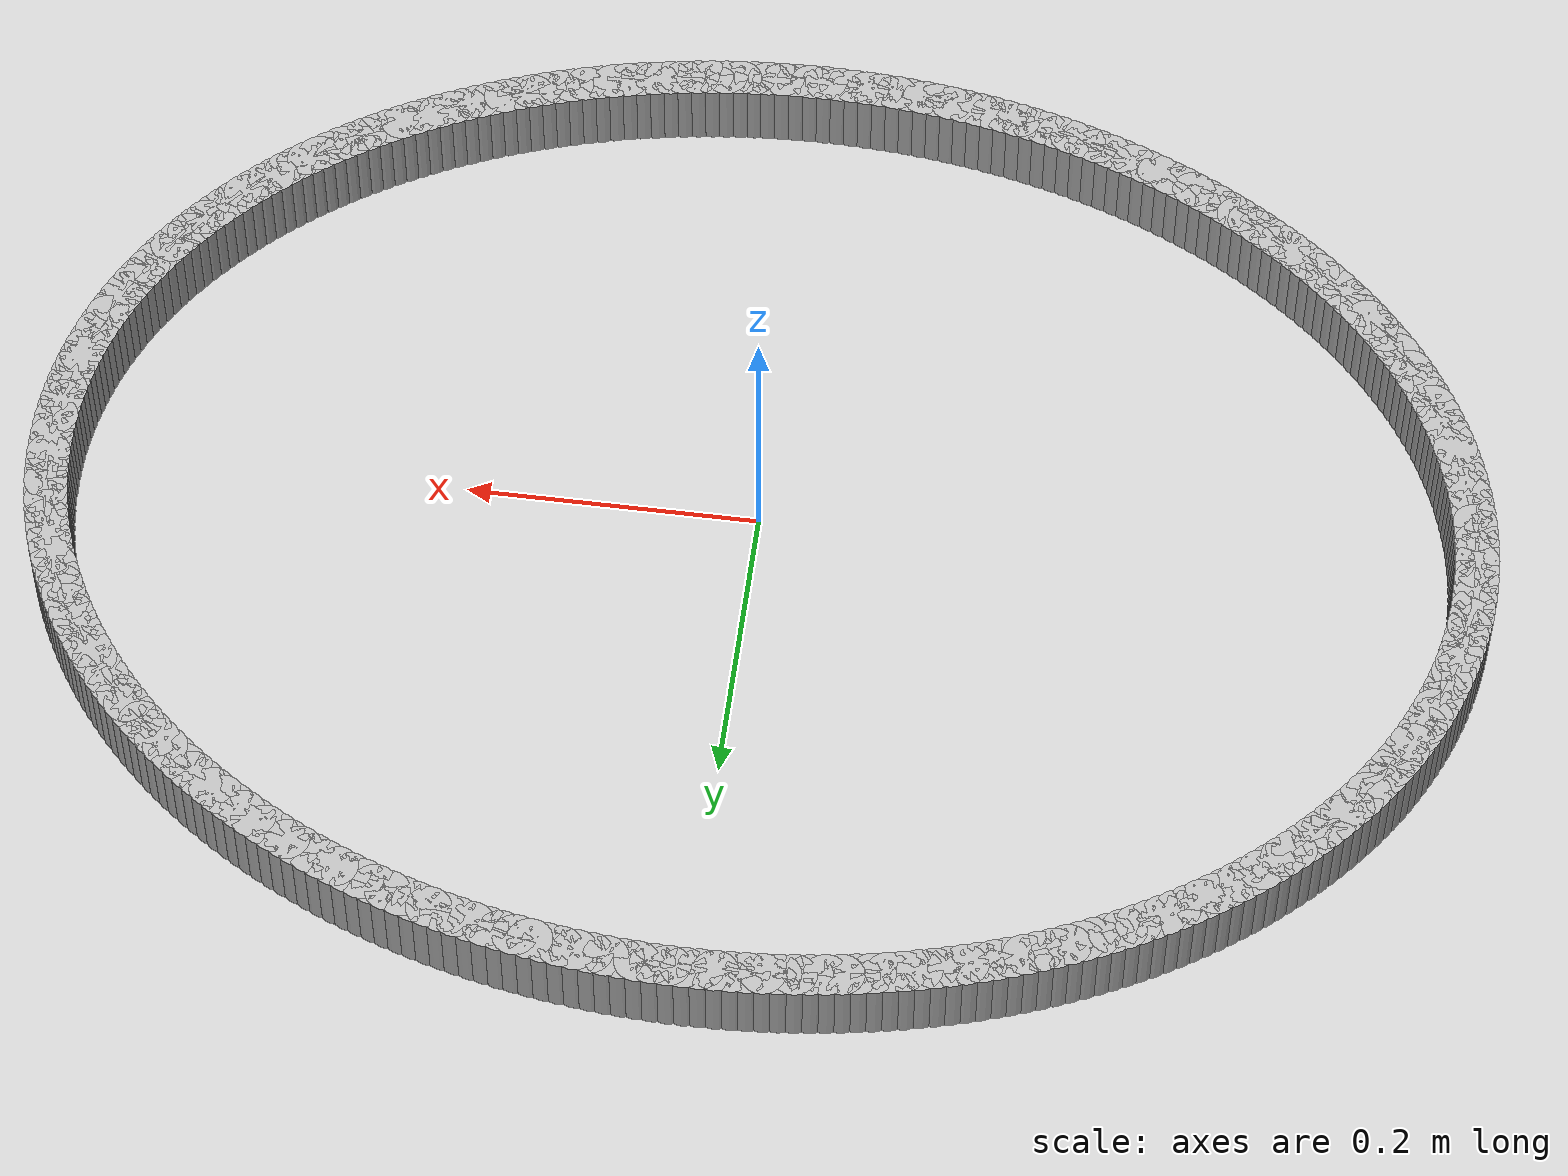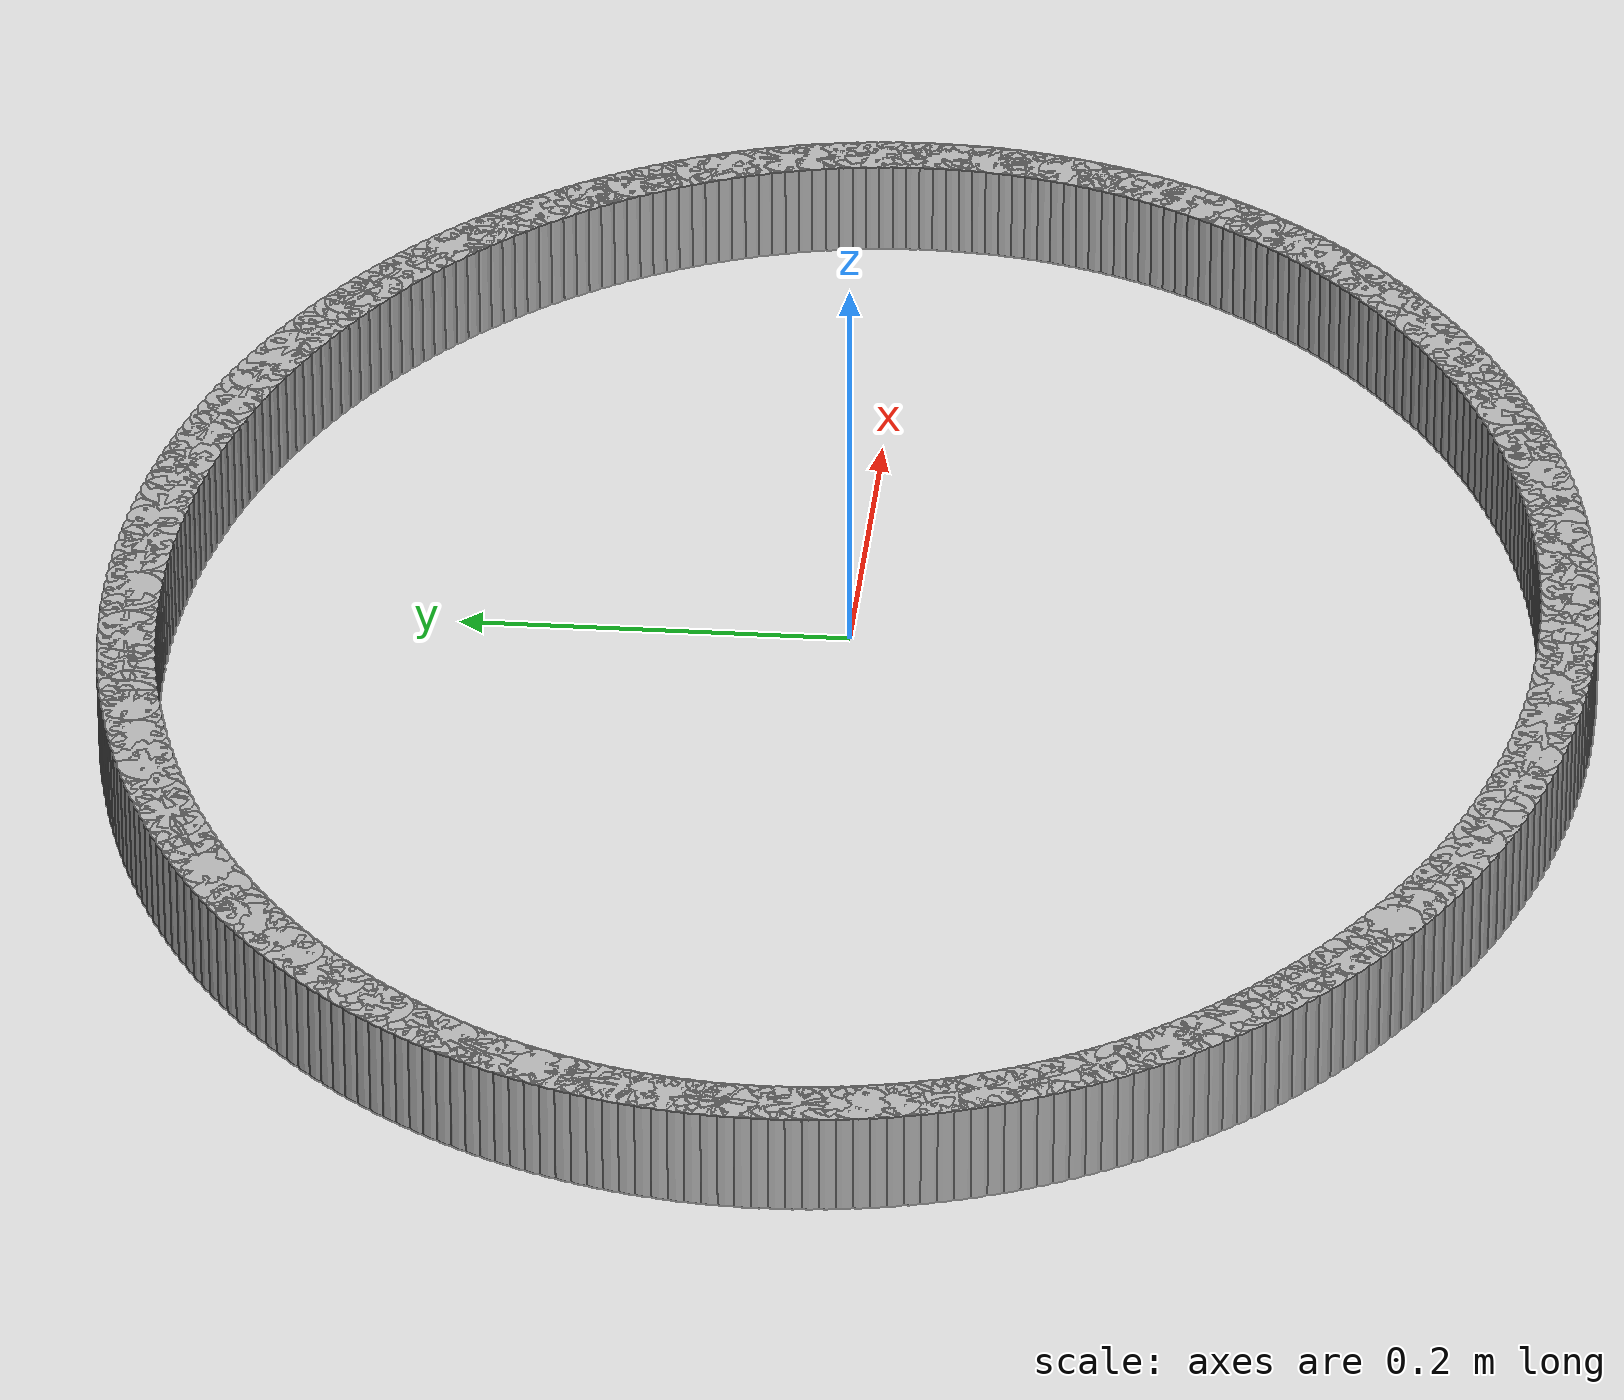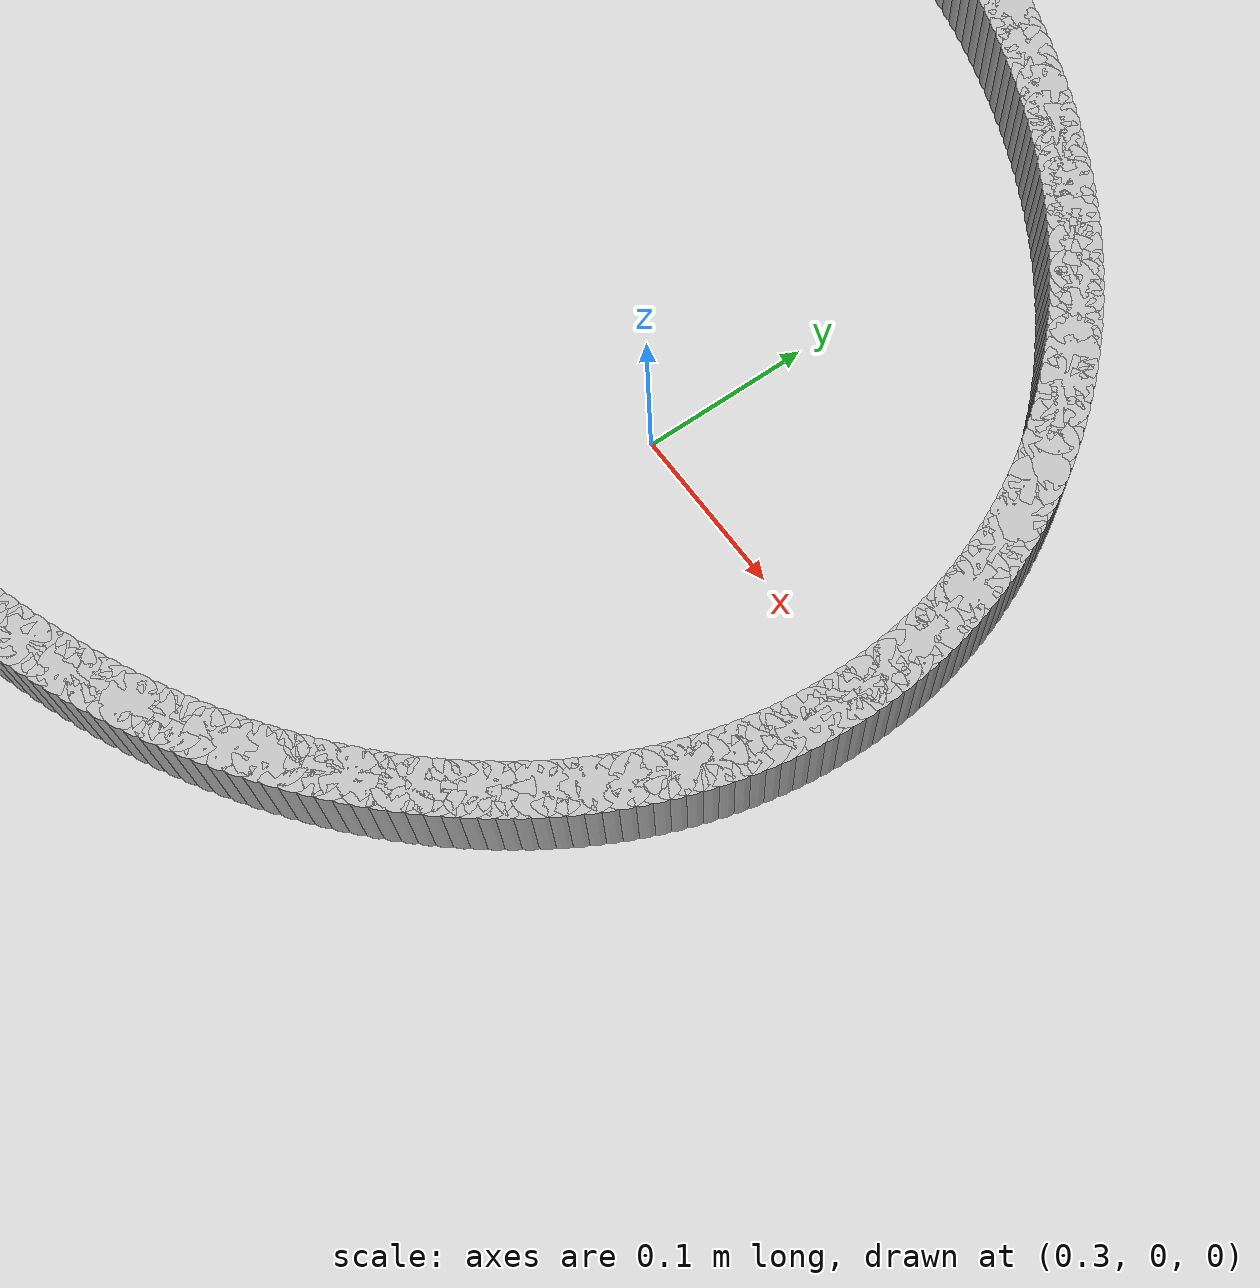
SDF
<?xml version='1.0'?>
<sdf version='1.6'>
    <model name='approximate_elliptical_ring'>
        <static>false</static>
        <link name='ring'>
            <inertial>
                <mass>1.0</mass>
                <inertia>
                    <ixx>0.1</ixx>
                    <iyy>0.1</iyy>
                    <izz>0.1</izz>
                </inertia>
            </inertial>
        </link>

        <link name='segment_0'>
            <pose>0.485 0.0 0 0 0 0.0</pose>
            <collision name='collision'>
                <geometry>
                    <cylinder>
                        <radius>0.015000000000000013</radius>
                        <length>0.05</length>
                    </cylinder>
                </geometry>
            </collision>
            <visual name='visual'>
                <geometry>
                    <cylinder>
                        <radius>0.015000000000000013</radius>
                        <length>0.05</length>
                    </cylinder>
                </geometry>
            </visual>
        </link>

        <link name='segment_1'>
            <pose>0.48489363148530007 0.0076439832574252894 0 0 0 0.020943951023931952</pose>
            <collision name='collision'>
                <geometry>
                    <cylinder>
                        <radius>0.015000000000000013</radius>
                        <length>0.05</length>
                    </cylinder>
                </geometry>
            </collision>
            <visual name='visual'>
                <geometry>
                    <cylinder>
                        <radius>0.015000000000000013</radius>
                        <length>0.05</length>
                    </cylinder>
                </geometry>
            </visual>
        </link>

        <link name='segment_2'>
            <pose>0.4845745725979463 0.015284613611157863 0 0 0 0.041887902047863905</pose>
            <collision name='collision'>
                <geometry>
                    <cylinder>
                        <radius>0.015000000000000013</radius>
                        <length>0.05</length>
                    </cylinder>
                </geometry>
            </collision>
            <visual name='visual'>
                <geometry>
                    <cylinder>
                        <radius>0.015000000000000013</radius>
                        <length>0.05</length>
                    </cylinder>
                </geometry>
            </visual>
        </link>

        <link name='segment_3'>
            <pose>0.4840429632877117 0.022918539628199376 0 0 0 0.06283185307179585</pose>
            <collision name='collision'>
                <geometry>
                    <cylinder>
                        <radius>0.015000000000000013</radius>
                        <length>0.05</length>
                    </cylinder>
                </geometry>
            </collision>
            <visual name='visual'>
                <geometry>
                    <cylinder>
                        <radius>0.015000000000000013</radius>
                        <length>0.05</length>
                    </cylinder>
                </geometry>
            </visual>
        </link>

        <link name='segment_4'>
            <pose>0.4832990367360096 0.03054241281629515 0 0 0 0.08377580409572781</pose>
            <collision name='collision'>
                <geometry>
                    <cylinder>
                        <radius>0.015000000000000013</radius>
                        <length>0.05</length>
                    </cylinder>
                </geometry>
            </collision>
            <visual name='visual'>
                <geometry>
                    <cylinder>
                        <radius>0.015000000000000013</radius>
                        <length>0.05</length>
                    </cylinder>
                </geometry>
            </visual>
        </link>

        <link name='segment_5'>
            <pose>0.4823431192536125 0.038152889092693515 0 0 0 0.10471975511965978</pose>
            <collision name='collision'>
                <geometry>
                    <cylinder>
                        <radius>0.015000000000000013</radius>
                        <length>0.05</length>
                    </cylinder>
                </geometry>
            </collision>
            <visual name='visual'>
                <geometry>
                    <cylinder>
                        <radius>0.015000000000000013</radius>
                        <length>0.05</length>
                    </cylinder>
                </geometry>
            </visual>
        </link>

        <link name='segment_6'>
            <pose>0.48117563013752174 0.045746630250971046 0 0 0 0.1256637061435917</pose>
            <collision name='collision'>
                <geometry>
                    <cylinder>
                        <radius>0.015000000000000013</radius>
                        <length>0.05</length>
                    </cylinder>
                </geometry>
            </collision>
            <visual name='visual'>
                <geometry>
                    <cylinder>
                        <radius>0.015000000000000013</radius>
                        <length>0.05</length>
                    </cylinder>
                </geometry>
            </visual>
        </link>

        <link name='segment_7'>
            <pose>0.4797970814870493 0.05332030542528024 0 0 0 0.1466076571675237</pose>
            <collision name='collision'>
                <geometry>
                    <cylinder>
                        <radius>0.015000000000000013</radius>
                        <length>0.05</length>
                    </cylinder>
                </geometry>
            </collision>
            <visual name='visual'>
                <geometry>
                    <cylinder>
                        <radius>0.015000000000000013</radius>
                        <length>0.05</length>
                    </cylinder>
                </geometry>
            </visual>
        </link>

        <link name='segment_8'>
            <pose>0.4782080779791949 0.06087059255137732 0 0 0 0.16755160819145562</pose>
            <collision name='collision'>
                <geometry>
                    <cylinder>
                        <radius>0.015000000000000013</radius>
                        <length>0.05</length>
                    </cylinder>
                </geometry>
            </collision>
            <visual name='visual'>
                <geometry>
                    <cylinder>
                        <radius>0.015000000000000013</radius>
                        <length>0.05</length>
                    </cylinder>
                </geometry>
            </visual>
        </link>

        <link name='segment_9'>
            <pose>0.476409316603414 0.06839417982378948 0 0 0 0.18849555921538758</pose>
            <collision name='collision'>
                <geometry>
                    <cylinder>
                        <radius>0.015000000000000013</radius>
                        <length>0.05</length>
                    </cylinder>
                </geometry>
            </collision>
            <visual name='visual'>
                <geometry>
                    <cylinder>
                        <radius>0.015000000000000013</radius>
                        <length>0.05</length>
                    </cylinder>
                </geometry>
            </visual>
        </link>

        <link name='segment_10'>
            <pose>0.47440158635589574 0.07588776714848215 0 0 0 0.20943951023931956</pose>
            <collision name='collision'>
                <geometry>
                    <cylinder>
                        <radius>0.015000000000000013</radius>
                        <length>0.05</length>
                    </cylinder>
                </geometry>
            </collision>
            <visual name='visual'>
                <geometry>
                    <cylinder>
                        <radius>0.015000000000000013</radius>
                        <length>0.05</length>
                    </cylinder>
                </geometry>
            </visual>
        </link>

        <link name='segment_11'>
            <pose>0.4721857678934827 0.08334806759038933 0 0 0 0.2303834612632515</pose>
            <collision name='collision'>
                <geometry>
                    <cylinder>
                        <radius>0.015000000000000013</radius>
                        <length>0.05</length>
                    </cylinder>
                </geometry>
            </collision>
            <visual name='visual'>
                <geometry>
                    <cylinder>
                        <radius>0.015000000000000013</radius>
                        <length>0.05</length>
                    </cylinder>
                </geometry>
            </visual>
        </link>

        <link name='segment_12'>
            <pose>0.46976283314738604 0.09077180881517198 0 0 0 0.2513274122871834</pose>
            <collision name='collision'>
                <geometry>
                    <cylinder>
                        <radius>0.015000000000000013</radius>
                        <length>0.05</length>
                    </cylinder>
                </geometry>
            </collision>
            <visual name='visual'>
                <geometry>
                    <cylinder>
                        <radius>0.015000000000000013</radius>
                        <length>0.05</length>
                    </cylinder>
                </geometry>
            </visual>
        </link>

        <link name='segment_13'>
            <pose>0.4671338448968642 0.09815573452457198 0 0 0 0.2722713633111154</pose>
            <collision name='collision'>
                <geometry>
                    <cylinder>
                        <radius>0.015000000000000013</radius>
                        <length>0.05</length>
                    </cylinder>
                </geometry>
            </collision>
            <visual name='visual'>
                <geometry>
                    <cylinder>
                        <radius>0.015000000000000013</radius>
                        <length>0.05</length>
                    </cylinder>
                </geometry>
            </visual>
        </link>

        <link name='segment_14'>
            <pose>0.4642999563030526 0.10549660588473214 0 0 0 0.2932153143350474</pose>
            <collision name='collision'>
                <geometry>
                    <cylinder>
                        <radius>0.015000000000000013</radius>
                        <length>0.05</length>
                    </cylinder>
                </geometry>
            </collision>
            <visual name='visual'>
                <geometry>
                    <cylinder>
                        <radius>0.015000000000000013</radius>
                        <length>0.05</length>
                    </cylinder>
                </geometry>
            </visual>
        </link>

        <link name='segment_15'>
            <pose>0.46126241040314947 0.1127912029468558 0 0 0 0.3141592653589793</pose>
            <collision name='collision'>
                <geometry>
                    <cylinder>
                        <radius>0.015000000000000013</radius>
                        <length>0.05</length>
                    </cylinder>
                </geometry>
            </collision>
            <visual name='visual'>
                <geometry>
                    <cylinder>
                        <radius>0.015000000000000013</radius>
                        <length>0.05</length>
                    </cylinder>
                </geometry>
            </visual>
        </link>

        <link name='segment_16'>
            <pose>0.4580225395651783 0.12003632605958288 0 0 0 0.33510321638291124</pose>
            <collision name='collision'>
                <geometry>
                    <cylinder>
                        <radius>0.015000000000000013</radius>
                        <length>0.05</length>
                    </cylinder>
                </geometry>
            </collision>
            <visual name='visual'>
                <geometry>
                    <cylinder>
                        <radius>0.015000000000000013</radius>
                        <length>0.05</length>
                    </cylinder>
                </geometry>
            </visual>
        </link>

        <link name='segment_17'>
            <pose>0.45458176490356733 0.12722879727246253 0 0 0 0.3560471674068432</pose>
            <collision name='collision'>
                <geometry>
                    <cylinder>
                        <radius>0.015000000000000013</radius>
                        <length>0.05</length>
                    </cylinder>
                </geometry>
            </collision>
            <visual name='visual'>
                <geometry>
                    <cylinder>
                        <radius>0.015000000000000013</radius>
                        <length>0.05</length>
                    </cylinder>
                </geometry>
            </visual>
        </link>

        <link name='segment_18'>
            <pose>0.45094159565580194 0.13436546172990743 0 0 0 0.37699111843077515</pose>
            <collision name='collision'>
                <geometry>
                    <cylinder>
                        <radius>0.015000000000000013</radius>
                        <length>0.05</length>
                    </cylinder>
                </geometry>
            </collision>
            <visual name='visual'>
                <geometry>
                    <cylinder>
                        <radius>0.015000000000000013</radius>
                        <length>0.05</length>
                    </cylinder>
                </geometry>
            </visual>
        </link>

        <link name='segment_19'>
            <pose>0.44710362852042274 0.1414431890550176 0 0 0 0.39793506945470714</pose>
            <collision name='collision'>
                <geometry>
                    <cylinder>
                        <radius>0.015000000000000013</radius>
                        <length>0.05</length>
                    </cylinder>
                </geometry>
            </collision>
            <visual name='visual'>
                <geometry>
                    <cylinder>
                        <radius>0.015000000000000013</radius>
                        <length>0.05</length>
                    </cylinder>
                </geometry>
            </visual>
        </link>

        <link name='segment_20'>
            <pose>0.4430695469566614 0.14845887472266708 0 0 0 0.4188790204786391</pose>
            <collision name='collision'>
                <geometry>
                    <cylinder>
                        <radius>0.015000000000000013</radius>
                        <length>0.05</length>
                    </cylinder>
                </geometry>
            </collision>
            <visual name='visual'>
                <geometry>
                    <cylinder>
                        <radius>0.015000000000000013</radius>
                        <length>0.05</length>
                    </cylinder>
                </geometry>
            </visual>
        </link>

        <link name='segment_21'>
            <pose>0.4388411204460195 0.15540944142125152 0 0 0 0.43982297150257105</pose>
            <collision name='collision'>
                <geometry>
                    <cylinder>
                        <radius>0.015000000000000013</radius>
                        <length>0.05</length>
                    </cylinder>
                </geometry>
            </collision>
            <visual name='visual'>
                <geometry>
                    <cylinder>
                        <radius>0.015000000000000013</radius>
                        <length>0.05</length>
                    </cylinder>
                </geometry>
            </visual>
        </link>

        <link name='segment_22'>
            <pose>0.4344202037161152 0.16229184040249853 0 0 0 0.460766922526503</pose>
            <collision name='collision'>
                <geometry>
                    <cylinder>
                        <radius>0.015000000000000013</radius>
                        <length>0.05</length>
                    </cylinder>
                </geometry>
            </collision>
            <visual name='visual'>
                <geometry>
                    <cylinder>
                        <radius>0.015000000000000013</radius>
                        <length>0.05</length>
                    </cylinder>
                </geometry>
            </visual>
        </link>

        <link name='segment_23'>
            <pose>0.42980873592713914 0.16910305281874952 0 0 0 0.4817108735504349</pose>
            <collision name='collision'>
                <geometry>
                    <cylinder>
                        <radius>0.015000000000000013</radius>
                        <length>0.05</length>
                    </cylinder>
                </geometry>
            </collision>
            <visual name='visual'>
                <geometry>
                    <cylinder>
                        <radius>0.015000000000000013</radius>
                        <length>0.05</length>
                    </cylinder>
                </geometry>
            </visual>
        </link>

        <link name='segment_24'>
            <pose>0.42500873982127385 0.17584009104712606 0 0 0 0.5026548245743668</pose>
            <collision name='collision'>
                <geometry>
                    <cylinder>
                        <radius>0.015000000000000013</radius>
                        <length>0.05</length>
                    </cylinder>
                </geometry>
            </collision>
            <visual name='visual'>
                <geometry>
                    <cylinder>
                        <radius>0.015000000000000013</radius>
                        <length>0.05</length>
                    </cylinder>
                </geometry>
            </visual>
        </link>

        <link name='segment_25'>
            <pose>0.42002232083545277 0.18249999999999997 0 0 0 0.5235987755982988</pose>
            <collision name='collision'>
                <geometry>
                    <cylinder>
                        <radius>0.015000000000000013</radius>
                        <length>0.05</length>
                    </cylinder>
                </geometry>
            </collision>
            <visual name='visual'>
                <geometry>
                    <cylinder>
                        <radius>0.015000000000000013</radius>
                        <length>0.05</length>
                    </cylinder>
                </geometry>
            </visual>
        </link>

        <link name='segment_26'>
            <pose>0.4148516661778457 0.18907985842119251 0 0 0 0.5445427266222308</pose>
            <collision name='collision'>
                <geometry>
                    <cylinder>
                        <radius>0.015000000000000013</radius>
                        <length>0.05</length>
                    </cylinder>
                </geometry>
            </collision>
            <visual name='visual'>
                <geometry>
                    <cylinder>
                        <radius>0.015000000000000013</radius>
                        <length>0.05</length>
                    </cylinder>
                </geometry>
            </visual>
        </link>

        <link name='segment_27'>
            <pose>0.4094990438684773 0.19557678016733376 0 0 0 0.5654866776461628</pose>
            <collision name='collision'>
                <geometry>
                    <cylinder>
                        <radius>0.015000000000000013</radius>
                        <length>0.05</length>
                    </cylinder>
                </geometry>
            </collision>
            <visual name='visual'>
                <geometry>
                    <cylinder>
                        <radius>0.015000000000000013</radius>
                        <length>0.05</length>
                    </cylinder>
                </geometry>
            </visual>
        </link>

        <link name='segment_28'>
            <pose>0.4039668017443982 0.20198791547382058 0 0 0 0.5864306286700948</pose>
            <collision name='collision'>
                <geometry>
                    <cylinder>
                        <radius>0.015000000000000013</radius>
                        <length>0.05</length>
                    </cylinder>
                </geometry>
            </collision>
            <visual name='visual'>
                <geometry>
                    <cylinder>
                        <radius>0.015000000000000013</radius>
                        <length>0.05</length>
                    </cylinder>
                </geometry>
            </visual>
        </link>

        <link name='segment_29'>
            <pose>0.39825736642984644 0.20831045220481753 0 0 0 0.6073745796940266</pose>
            <collision name='collision'>
                <geometry>
                    <cylinder>
                        <radius>0.015000000000000013</radius>
                        <length>0.05</length>
                    </cylinder>
                </geometry>
            </collision>
            <visual name='visual'>
                <geometry>
                    <cylinder>
                        <radius>0.015000000000000013</radius>
                        <length>0.05</length>
                    </cylinder>
                </geometry>
            </visual>
        </link>

        <link name='segment_30'>
            <pose>0.3923732422718495 0.21454161708675268 0 0 0 0.6283185307179586</pose>
            <collision name='collision'>
                <geometry>
                    <cylinder>
                        <radius>0.015000000000000013</radius>
                        <length>0.05</length>
                    </cylinder>
                </geometry>
            </collision>
            <visual name='visual'>
                <geometry>
                    <cylinder>
                        <radius>0.015000000000000013</radius>
                        <length>0.05</length>
                    </cylinder>
                </geometry>
            </visual>
        </link>

        <link name='segment_31'>
            <pose>0.3863170102417352 0.22067867692476678 0 0 0 0.6492624817418905</pose>
            <collision name='collision'>
                <geometry>
                    <cylinder>
                        <radius>0.015000000000000013</radius>
                        <length>0.05</length>
                    </cylinder>
                </geometry>
            </collision>
            <visual name='visual'>
                <geometry>
                    <cylinder>
                        <radius>0.015000000000000013</radius>
                        <length>0.05</length>
                    </cylinder>
                </geometry>
            </visual>
        </link>

        <link name='segment_32'>
            <pose>0.3800913268030323 0.22671893980158325 0 0 0 0.6702064327658225</pose>
            <collision name='collision'>
                <geometry>
                    <cylinder>
                        <radius>0.015000000000000013</radius>
                        <length>0.05</length>
                    </cylinder>
                </geometry>
            </collision>
            <visual name='visual'>
                <geometry>
                    <cylinder>
                        <radius>0.015000000000000013</radius>
                        <length>0.05</length>
                    </cylinder>
                </geometry>
            </visual>
        </link>

        <link name='segment_33'>
            <pose>0.3736989227462577 0.23265975625827176 0 0 0 0.6911503837897546</pose>
            <collision name='collision'>
                <geometry>
                    <cylinder>
                        <radius>0.015000000000000013</radius>
                        <length>0.05</length>
                    </cylinder>
                </geometry>
            </collision>
            <visual name='visual'>
                <geometry>
                    <cylinder>
                        <radius>0.015000000000000013</radius>
                        <length>0.05</length>
                    </cylinder>
                </geometry>
            </visual>
        </link>

        <link name='segment_34'>
            <pose>0.3671426019911018 0.23849852045638845 0 0 0 0.7120943348136864</pose>
            <collision name='collision'>
                <geometry>
                    <cylinder>
                        <radius>0.015000000000000013</radius>
                        <length>0.05</length>
                    </cylinder>
                </geometry>
            </collision>
            <visual name='visual'>
                <geometry>
                    <cylinder>
                        <radius>0.015000000000000013</radius>
                        <length>0.05</length>
                    </cylinder>
                </geometry>
            </visual>
        </link>

        <link name='segment_35'>
            <pose>0.3604252403565362 0.24423267132098325 0 0 0 0.7330382858376184</pose>
            <collision name='collision'>
                <geometry>
                    <cylinder>
                        <radius>0.015000000000000013</radius>
                        <length>0.05</length>
                    </cylinder>
                </geometry>
            </collision>
            <visual name='visual'>
                <geometry>
                    <cylinder>
                        <radius>0.015000000000000013</radius>
                        <length>0.05</length>
                    </cylinder>
                </geometry>
            </visual>
        </link>

        <link name='segment_36'>
            <pose>0.3535497842993846 0.24985969366397134 0 0 0 0.7539822368615503</pose>
            <collision name='collision'>
                <geometry>
                    <cylinder>
                        <radius>0.015000000000000013</radius>
                        <length>0.05</length>
                    </cylinder>
                </geometry>
            </collision>
            <visual name='visual'>
                <geometry>
                    <cylinder>
                        <radius>0.015000000000000013</radius>
                        <length>0.05</length>
                    </cylinder>
                </geometry>
            </visual>
        </link>

        <link name='segment_37'>
            <pose>0.3465192496219096 0.2553771192873784 0 0 0 0.7749261878854823</pose>
            <collision name='collision'>
                <geometry>
                    <cylinder>
                        <radius>0.015000000000000013</radius>
                        <length>0.05</length>
                    </cylinder>
                </geometry>
            </collision>
            <visual name='visual'>
                <geometry>
                    <cylinder>
                        <radius>0.015000000000000013</radius>
                        <length>0.05</length>
                    </cylinder>
                </geometry>
            </visual>
        </link>

        <link name='segment_38'>
            <pose>0.3393367201489822 0.26078252806597324 0 0 0 0.7958701389094143</pose>
            <collision name='collision'>
                <geometry>
                    <cylinder>
                        <radius>0.015000000000000013</radius>
                        <length>0.05</length>
                    </cylinder>
                </geometry>
            </collision>
            <visual name='visual'>
                <geometry>
                    <cylinder>
                        <radius>0.015000000000000013</radius>
                        <length>0.05</length>
                    </cylinder>
                </geometry>
            </visual>
        </link>

        <link name='segment_39'>
            <pose>0.332005346375414 0.2660735490088152 0 0 0 0.8168140899333461</pose>
            <collision name='collision'>
                <geometry>
                    <cylinder>
                        <radius>0.015000000000000013</radius>
                        <length>0.05</length>
                    </cylinder>
                </geometry>
            </collision>
            <visual name='visual'>
                <geometry>
                    <cylinder>
                        <radius>0.015000000000000013</radius>
                        <length>0.05</length>
                    </cylinder>
                </geometry>
            </visual>
        </link>

        <link name='segment_40'>
            <pose>0.32452834408404624 0.2712478612992489 0 0 0 0.8377580409572782</pose>
            <collision name='collision'>
                <geometry>
                    <cylinder>
                        <radius>0.015000000000000013</radius>
                        <length>0.05</length>
                    </cylinder>
                </geometry>
            </collision>
            <visual name='visual'>
                <geometry>
                    <cylinder>
                        <radius>0.015000000000000013</radius>
                        <length>0.05</length>
                    </cylinder>
                </geometry>
            </visual>
        </link>

        <link name='segment_41'>
            <pose>0.31690899293520114 0.2763031953128911 0 0 0 0.8587019919812101</pose>
            <collision name='collision'>
                <geometry>
                    <cylinder>
                        <radius>0.015000000000000013</radius>
                        <length>0.05</length>
                    </cylinder>
                </geometry>
            </collision>
            <visual name='visual'>
                <geometry>
                    <cylinder>
                        <radius>0.015000000000000013</radius>
                        <length>0.05</length>
                    </cylinder>
                </geometry>
            </visual>
        </link>

        <link name='segment_42'>
            <pose>0.3091506350281145 0.28123733361316305 0 0 0 0.8796459430051421</pose>
            <collision name='collision'>
                <geometry>
                    <cylinder>
                        <radius>0.015000000000000013</radius>
                        <length>0.05</length>
                    </cylinder>
                </geometry>
            </collision>
            <visual name='visual'>
                <geometry>
                    <cylinder>
                        <radius>0.015000000000000013</radius>
                        <length>0.05</length>
                    </cylinder>
                </geometry>
            </visual>
        </link>

        <link name='segment_43'>
            <pose>0.30125667343498047 0.28604811192393154 0 0 0 0.9005898940290741</pose>
            <collision name='collision'>
                <geometry>
                    <cylinder>
                        <radius>0.015000000000000013</radius>
                        <length>0.05</length>
                    </cylinder>
                </geometry>
            </collision>
            <visual name='visual'>
                <geometry>
                    <cylinder>
                        <radius>0.015000000000000013</radius>
                        <length>0.05</length>
                    </cylinder>
                </geometry>
            </visual>
        </link>

        <link name='segment_44'>
            <pose>0.2932305707082518 0.29073342007883163 0 0 0 0.921533845053006</pose>
            <collision name='collision'>
                <geometry>
                    <cylinder>
                        <radius>0.015000000000000013</radius>
                        <length>0.05</length>
                    </cylinder>
                </geometry>
            </collision>
            <visual name='visual'>
                <geometry>
                    <cylinder>
                        <radius>0.015000000000000013</radius>
                        <length>0.05</length>
                    </cylinder>
                </geometry>
            </visual>
        </link>

        <link name='segment_45'>
            <pose>0.2850758473618495 0.2952912029468558 0 0 0 0.9424777960769379</pose>
            <collision name='collision'>
                <geometry>
                    <cylinder>
                        <radius>0.015000000000000013</radius>
                        <length>0.05</length>
                    </cylinder>
                </geometry>
            </collision>
            <visual name='visual'>
                <geometry>
                    <cylinder>
                        <radius>0.015000000000000013</radius>
                        <length>0.05</length>
                    </cylinder>
                </geometry>
            </visual>
        </link>

        <link name='segment_46'>
            <pose>0.2767960803269494 0.29971946133380195 0 0 0 0.9634217471008698</pose>
            <collision name='collision'>
                <geometry>
                    <cylinder>
                        <radius>0.015000000000000013</radius>
                        <length>0.05</length>
                    </cylinder>
                </geometry>
            </collision>
            <visual name='visual'>
                <geometry>
                    <cylinder>
                        <radius>0.015000000000000013</radius>
                        <length>0.05</length>
                    </cylinder>
                </geometry>
            </visual>
        </link>

        <link name='segment_47'>
            <pose>0.2683949013830219 0.30401625285918626 0 0 0 0.9843656981248018</pose>
            <collision name='collision'>
                <geometry>
                    <cylinder>
                        <radius>0.015000000000000013</radius>
                        <length>0.05</length>
                    </cylinder>
                </geometry>
            </collision>
            <visual name='visual'>
                <geometry>
                    <cylinder>
                        <radius>0.015000000000000013</radius>
                        <length>0.05</length>
                    </cylinder>
                </geometry>
            </visual>
        </link>

        <link name='segment_48'>
            <pose>0.25987599556481344 0.30817969280823543 0 0 0 1.0053096491487337</pose>
            <collision name='collision'>
                <geometry>
                    <cylinder>
                        <radius>0.015000000000000013</radius>
                        <length>0.05</length>
                    </cylinder>
                </geometry>
            </collision>
            <visual name='visual'>
                <geometry>
                    <cylinder>
                        <radius>0.015000000000000013</radius>
                        <length>0.05</length>
                    </cylinder>
                </geometry>
            </visual>
        </link>

        <link name='segment_49'>
            <pose>0.2512430995459682 0.3122079549585849 0 0 0 1.0262536001726656</pose>
            <collision name='collision'>
                <geometry>
                    <cylinder>
                        <radius>0.015000000000000013</radius>
                        <length>0.05</length>
                    </cylinder>
                </geometry>
            </collision>
            <visual name='visual'>
                <geometry>
                    <cylinder>
                        <radius>0.015000000000000013</radius>
                        <length>0.05</length>
                    </cylinder>
                </geometry>
            </visual>
        </link>

        <link name='segment_50'>
            <pose>0.24250000000000005 0.3160992723813201 0 0 0 1.0471975511965976</pose>
            <collision name='collision'>
                <geometry>
                    <cylinder>
                        <radius>0.015000000000000013</radius>
                        <length>0.05</length>
                    </cylinder>
                </geometry>
            </collision>
            <visual name='visual'>
                <geometry>
                    <cylinder>
                        <radius>0.015000000000000013</radius>
                        <length>0.05</length>
                    </cylinder>
                </geometry>
            </visual>
        </link>

        <link name='segment_51'>
            <pose>0.2336505319393319 0.3198519382160102 0 0 0 1.0681415022205296</pose>
            <collision name='collision'>
                <geometry>
                    <cylinder>
                        <radius>0.015000000000000013</radius>
                        <length>0.05</length>
                    </cylinder>
                </geometry>
            </collision>
            <visual name='visual'>
                <geometry>
                    <cylinder>
                        <radius>0.015000000000000013</radius>
                        <length>0.05</length>
                    </cylinder>
                </geometry>
            </visual>
        </link>

        <link name='segment_52'>
            <pose>0.22469857703313295 0.3234643064193934 0 0 0 1.0890854532444616</pose>
            <collision name='collision'>
                <geometry>
                    <cylinder>
                        <radius>0.015000000000000013</radius>
                        <length>0.05</length>
                    </cylinder>
                </geometry>
            </collision>
            <visual name='visual'>
                <geometry>
                    <cylinder>
                        <radius>0.015000000000000013</radius>
                        <length>0.05</length>
                    </cylinder>
                </geometry>
            </visual>
        </link>

        <link name='segment_53'>
            <pose>0.21564806190468983 0.3269347924873857 0 0 0 1.1100294042683936</pose>
            <collision name='collision'>
                <geometry>
                    <cylinder>
                        <radius>0.015000000000000013</radius>
                        <length>0.05</length>
                    </cylinder>
                </geometry>
            </collision>
            <visual name='visual'>
                <geometry>
                    <cylinder>
                        <radius>0.015000000000000013</radius>
                        <length>0.05</length>
                    </cylinder>
                </geometry>
            </visual>
        </link>

        <link name='segment_54'>
            <pose>0.20650295640906025 0.3302618741500971 0 0 0 1.1309733552923256</pose>
            <collision name='collision'>
                <geometry>
                    <cylinder>
                        <radius>0.015000000000000013</radius>
                        <length>0.05</length>
                    </cylinder>
                </geometry>
            </collision>
            <visual name='visual'>
                <geometry>
                    <cylinder>
                        <radius>0.015000000000000013</radius>
                        <length>0.05</length>
                    </cylinder>
                </geometry>
            </visual>
        </link>

        <link name='segment_55'>
            <pose>0.1972672718917631 0.33344409203954933 0 0 0 1.1519173063162575</pose>
            <collision name='collision'>
                <geometry>
                    <cylinder>
                        <radius>0.015000000000000013</radius>
                        <length>0.05</length>
                    </cylinder>
                </geometry>
            </collision>
            <visual name='visual'>
                <geometry>
                    <cylinder>
                        <radius>0.015000000000000013</radius>
                        <length>0.05</length>
                    </cylinder>
                </geometry>
            </visual>
        </link>

        <link name='segment_56'>
            <pose>0.18794505942926992 0.33648005032980266 0 0 0 1.1728612573401895</pose>
            <collision name='collision'>
                <geometry>
                    <cylinder>
                        <radius>0.015000000000000013</radius>
                        <length>0.05</length>
                    </cylinder>
                </geometry>
            </collision>
            <visual name='visual'>
                <geometry>
                    <cylinder>
                        <radius>0.015000000000000013</radius>
                        <length>0.05</length>
                    </cylinder>
                </geometry>
            </visual>
        </link>

        <link name='segment_57'>
            <pose>0.17854040805206886 0.33936841734921175 0 0 0 1.1938052083641213</pose>
            <collision name='collision'>
                <geometry>
                    <cylinder>
                        <radius>0.015000000000000013</radius>
                        <length>0.05</length>
                    </cylinder>
                </geometry>
            </collision>
            <visual name='visual'>
                <geometry>
                    <cylinder>
                        <radius>0.015000000000000013</radius>
                        <length>0.05</length>
                    </cylinder>
                </geometry>
            </visual>
        </link>

        <link name='segment_58'>
            <pose>0.1690574429510804 0.3421079261645404 0 0 0 1.2147491593880533</pose>
            <collision name='collision'>
                <geometry>
                    <cylinder>
                        <radius>0.015000000000000013</radius>
                        <length>0.05</length>
                    </cylinder>
                </geometry>
            </collision>
            <visual name='visual'>
                <geometry>
                    <cylinder>
                        <radius>0.015000000000000013</radius>
                        <length>0.05</length>
                    </cylinder>
                </geometry>
            </visual>
        </link>

        <link name='segment_59'>
            <pose>0.1595003236682129 0.3446973751366806 0 0 0 1.2356931104119853</pose>
            <collision name='collision'>
                <geometry>
                    <cylinder>
                        <radius>0.015000000000000013</radius>
                        <length>0.05</length>
                    </cylinder>
                </geometry>
            </collision>
            <visual name='visual'>
                <geometry>
                    <cylinder>
                        <radius>0.015000000000000013</radius>
                        <length>0.05</length>
                    </cylinder>
                </geometry>
            </visual>
        </link>

        <link name='segment_60'>
            <pose>0.1498732422718495 0.34713562844773105 0 0 0 1.2566370614359172</pose>
            <collision name='collision'>
                <geometry>
                    <cylinder>
                        <radius>0.015000000000000013</radius>
                        <length>0.05</length>
                    </cylinder>
                </geometry>
            </collision>
            <visual name='visual'>
                <geometry>
                    <cylinder>
                        <radius>0.015000000000000013</radius>
                        <length>0.05</length>
                    </cylinder>
                </geometry>
            </visual>
        </link>

        <link name='segment_61'>
            <pose>0.14018042151806873 0.3494216165992045 0 0 0 1.2775810124598492</pose>
            <collision name='collision'>
                <geometry>
                    <cylinder>
                        <radius>0.015000000000000013</radius>
                        <length>0.05</length>
                    </cylinder>
                </geometry>
            </collision>
            <visual name='visual'>
                <geometry>
                    <cylinder>
                        <radius>0.015000000000000013</radius>
                        <length>0.05</length>
                    </cylinder>
                </geometry>
            </visual>
        </link>

        <link name='segment_62'>
            <pose>0.13042611299840398 0.3515543368811452 0 0 0 1.298524963483781</pose>
            <collision name='collision'>
                <geometry>
                    <cylinder>
                        <radius>0.015000000000000013</radius>
                        <length>0.05</length>
                    </cylinder>
                </geometry>
            </collision>
            <visual name='visual'>
                <geometry>
                    <cylinder>
                        <radius>0.015000000000000013</radius>
                        <length>0.05</length>
                    </cylinder>
                </geometry>
            </visual>
        </link>

        <link name='segment_63'>
            <pose>0.12061459527495465 0.3535328538119503 0 0 0 1.319468914507713</pose>
            <collision name='collision'>
                <geometry>
                    <cylinder>
                        <radius>0.015000000000000013</radius>
                        <length>0.05</length>
                    </cylinder>
                </geometry>
            </collision>
            <visual name='visual'>
                <geometry>
                    <cylinder>
                        <radius>0.015000000000000013</radius>
                        <length>0.05</length>
                    </cylinder>
                </geometry>
            </visual>
        </link>

        <link name='segment_64'>
            <pose>0.1107501720036681 0.35535629954870346 0 0 0 1.340412865531645</pose>
            <collision name='collision'>
                <geometry>
                    <cylinder>
                        <radius>0.015000000000000013</radius>
                        <length>0.05</length>
                    </cylinder>
                </geometry>
            </collision>
            <visual name='visual'>
                <geometry>
                    <cylinder>
                        <radius>0.015000000000000013</radius>
                        <length>0.05</length>
                    </cylinder>
                </geometry>
            </visual>
        </link>

        <link name='segment_65'>
            <pose>0.10083717004661333 0.35702387426783905 0 0 0 1.361356816555577</pose>
            <collision name='collision'>
                <geometry>
                    <cylinder>
                        <radius>0.015000000000000013</radius>
                        <length>0.05</length>
                    </cylinder>
                </geometry>
            </collision>
            <visual name='visual'>
                <geometry>
                    <cylinder>
                        <radius>0.015000000000000013</radius>
                        <length>0.05</length>
                    </cylinder>
                </geometry>
            </visual>
        </link>

        <link name='segment_66'>
            <pose>0.09087993757407639 0.3585348465159714 0 0 0 1.3823007675795091</pose>
            <collision name='collision'>
                <geometry>
                    <cylinder>
                        <radius>0.015000000000000013</radius>
                        <length>0.05</length>
                    </cylinder>
                </geometry>
            </collision>
            <visual name='visual'>
                <geometry>
                    <cylinder>
                        <radius>0.015000000000000013</radius>
                        <length>0.05</length>
                    </cylinder>
                </geometry>
            </visual>
        </link>

        <link name='segment_67'>
            <pose>0.08088284215730963 0.3598885535307343 0 0 0 1.403244718603441</pose>
            <collision name='collision'>
                <geometry>
                    <cylinder>
                        <radius>0.015000000000000013</radius>
                        <length>0.05</length>
                    </cylinder>
                </geometry>
            </collision>
            <visual name='visual'>
                <geometry>
                    <cylinder>
                        <radius>0.015000000000000013</radius>
                        <length>0.05</length>
                    </cylinder>
                </geometry>
            </visual>
        </link>

        <link name='segment_68'>
            <pose>0.07085026885276965 0.36108440153149074 0 0 0 1.424188669627373</pose>
            <collision name='collision'>
                <geometry>
                    <cylinder>
                        <radius>0.015000000000000013</radius>
                        <length>0.05</length>
                    </cylinder>
                </geometry>
            </collision>
            <visual name='visual'>
                <geometry>
                    <cylinder>
                        <radius>0.015000000000000013</radius>
                        <length>0.05</length>
                    </cylinder>
                </geometry>
            </visual>
        </link>

        <link name='segment_69'>
            <pose>0.06078661827868757 0.3621218659797844 0 0 0 1.4451326206513049</pose>
            <collision name='collision'>
                <geometry>
                    <cylinder>
                        <radius>0.015000000000000013</radius>
                        <length>0.05</length>
                    </cylinder>
                </geometry>
            </collision>
            <visual name='visual'>
                <geometry>
                    <cylinder>
                        <radius>0.015000000000000013</radius>
                        <length>0.05</length>
                    </cylinder>
                </geometry>
            </visual>
        </link>

        <link name='segment_70'>
            <pose>0.05069630468481193 0.36300049180941973 0 0 0 1.4660765716752369</pose>
            <collision name='collision'>
                <geometry>
                    <cylinder>
                        <radius>0.015000000000000013</radius>
                        <length>0.05</length>
                    </cylinder>
                </geometry>
            </collision>
            <visual name='visual'>
                <geometry>
                    <cylinder>
                        <radius>0.015000000000000013</radius>
                        <length>0.05</length>
                    </cylinder>
                </geometry>
            </visual>
        </link>

        <link name='segment_71'>
            <pose>0.040583754016172986 0.3637198936260691 0 0 0 1.4870205226991688</pose>
            <collision name='collision'>
                <geometry>
                    <cylinder>
                        <radius>0.015000000000000013</radius>
                        <length>0.05</length>
                    </cylinder>
                </geometry>
            </collision>
            <visual name='visual'>
                <geometry>
                    <cylinder>
                        <radius>0.015000000000000013</radius>
                        <length>0.05</length>
                    </cylinder>
                </geometry>
            </visual>
        </link>

        <link name='segment_72'>
            <pose>0.03045340197171706 0.3642797558763191 0 0 0 1.5079644737231006</pose>
            <collision name='collision'>
                <geometry>
                    <cylinder>
                        <radius>0.015000000000000013</radius>
                        <length>0.05</length>
                    </cylinder>
                </geometry>
            </collision>
            <visual name='visual'>
                <geometry>
                    <cylinder>
                        <radius>0.015000000000000013</radius>
                        <length>0.05</length>
                    </cylinder>
                </geometry>
            </visual>
        </link>

        <link name='segment_73'>
            <pose>0.020309692058661878 0.3646798329860833 0 0 0 1.5289084247470326</pose>
            <collision name='collision'>
                <geometry>
                    <cylinder>
                        <radius>0.015000000000000013</radius>
                        <length>0.05</length>
                    </cylinder>
                </geometry>
            </collision>
            <visual name='visual'>
                <geometry>
                    <cylinder>
                        <radius>0.015000000000000013</radius>
                        <length>0.05</length>
                    </cylinder>
                </geometry>
            </visual>
        </link>

        <link name='segment_74'>
            <pose>0.01015707364342817 0.36491994946831857 0 0 0 1.5498523757709646</pose>
            <collision name='collision'>
                <geometry>
                    <cylinder>
                        <radius>0.015000000000000013</radius>
                        <length>0.05</length>
                    </cylinder>
                </geometry>
            </collision>
            <visual name='visual'>
                <geometry>
                    <cylinder>
                        <radius>0.015000000000000013</radius>
                        <length>0.05</length>
                    </cylinder>
                </geometry>
            </visual>
        </link>

        <link name='segment_75'>
            <pose>2.969768487932332e-17 0.365 0 0 0 1.5707963267948966</pose>
            <collision name='collision'>
                <geometry>
                    <cylinder>
                        <radius>0.015000000000000013</radius>
                        <length>0.05</length>
                    </cylinder>
                </geometry>
            </collision>
            <visual name='visual'>
                <geometry>
                    <cylinder>
                        <radius>0.015000000000000013</radius>
                        <length>0.05</length>
                    </cylinder>
                </geometry>
            </visual>
        </link>

        <link name='segment_76'>
            <pose>-0.010157073643428109 0.36491994946831857 0 0 0 1.5917402778188285</pose>
            <collision name='collision'>
                <geometry>
                    <cylinder>
                        <radius>0.015000000000000013</radius>
                        <length>0.05</length>
                    </cylinder>
                </geometry>
            </collision>
            <visual name='visual'>
                <geometry>
                    <cylinder>
                        <radius>0.015000000000000013</radius>
                        <length>0.05</length>
                    </cylinder>
                </geometry>
            </visual>
        </link>

        <link name='segment_77'>
            <pose>-0.020309692058661708 0.3646798329860833 0 0 0 1.6126842288427603</pose>
            <collision name='collision'>
                <geometry>
                    <cylinder>
                        <radius>0.015000000000000013</radius>
                        <length>0.05</length>
                    </cylinder>
                </geometry>
            </collision>
            <visual name='visual'>
                <geometry>
                    <cylinder>
                        <radius>0.015000000000000013</radius>
                        <length>0.05</length>
                    </cylinder>
                </geometry>
            </visual>
        </link>

        <link name='segment_78'>
            <pose>-0.030453401971716892 0.3642797558763191 0 0 0 1.6336281798666923</pose>
            <collision name='collision'>
                <geometry>
                    <cylinder>
                        <radius>0.015000000000000013</radius>
                        <length>0.05</length>
                    </cylinder>
                </geometry>
            </collision>
            <visual name='visual'>
                <geometry>
                    <cylinder>
                        <radius>0.015000000000000013</radius>
                        <length>0.05</length>
                    </cylinder>
                </geometry>
            </visual>
        </link>

        <link name='segment_79'>
            <pose>-0.04058375401617293 0.3637198936260691 0 0 0 1.6545721308906243</pose>
            <collision name='collision'>
                <geometry>
                    <cylinder>
                        <radius>0.015000000000000013</radius>
                        <length>0.05</length>
                    </cylinder>
                </geometry>
            </collision>
            <visual name='visual'>
                <geometry>
                    <cylinder>
                        <radius>0.015000000000000013</radius>
                        <length>0.05</length>
                    </cylinder>
                </geometry>
            </visual>
        </link>

        <link name='segment_80'>
            <pose>-0.050696304684811976 0.36300049180941973 0 0 0 1.6755160819145565</pose>
            <collision name='collision'>
                <geometry>
                    <cylinder>
                        <radius>0.015000000000000013</radius>
                        <length>0.05</length>
                    </cylinder>
                </geometry>
            </collision>
            <visual name='visual'>
                <geometry>
                    <cylinder>
                        <radius>0.015000000000000013</radius>
                        <length>0.05</length>
                    </cylinder>
                </geometry>
            </visual>
        </link>

        <link name='segment_81'>
            <pose>-0.060786618278687615 0.36212186597978435 0 0 0 1.6964600329384885</pose>
            <collision name='collision'>
                <geometry>
                    <cylinder>
                        <radius>0.015000000000000013</radius>
                        <length>0.05</length>
                    </cylinder>
                </geometry>
            </collision>
            <visual name='visual'>
                <geometry>
                    <cylinder>
                        <radius>0.015000000000000013</radius>
                        <length>0.05</length>
                    </cylinder>
                </geometry>
            </visual>
        </link>

        <link name='segment_82'>
            <pose>-0.0708502688527696 0.36108440153149074 0 0 0 1.7174039839624202</pose>
            <collision name='collision'>
                <geometry>
                    <cylinder>
                        <radius>0.015000000000000013</radius>
                        <length>0.05</length>
                    </cylinder>
                </geometry>
            </collision>
            <visual name='visual'>
                <geometry>
                    <cylinder>
                        <radius>0.015000000000000013</radius>
                        <length>0.05</length>
                    </cylinder>
                </geometry>
            </visual>
        </link>

        <link name='segment_83'>
            <pose>-0.08088284215730958 0.3598885535307343 0 0 0 1.7383479349863522</pose>
            <collision name='collision'>
                <geometry>
                    <cylinder>
                        <radius>0.015000000000000013</radius>
                        <length>0.05</length>
                    </cylinder>
                </geometry>
            </collision>
            <visual name='visual'>
                <geometry>
                    <cylinder>
                        <radius>0.015000000000000013</radius>
                        <length>0.05</length>
                    </cylinder>
                </geometry>
            </visual>
        </link>

        <link name='segment_84'>
            <pose>-0.09087993757407643 0.3585348465159714 0 0 0 1.7592918860102842</pose>
            <collision name='collision'>
                <geometry>
                    <cylinder>
                        <radius>0.015000000000000013</radius>
                        <length>0.05</length>
                    </cylinder>
                </geometry>
            </collision>
            <visual name='visual'>
                <geometry>
                    <cylinder>
                        <radius>0.015000000000000013</radius>
                        <length>0.05</length>
                    </cylinder>
                </geometry>
            </visual>
        </link>

        <link name='segment_85'>
            <pose>-0.10083717004661327 0.35702387426783905 0 0 0 1.7802358370342162</pose>
            <collision name='collision'>
                <geometry>
                    <cylinder>
                        <radius>0.015000000000000013</radius>
                        <length>0.05</length>
                    </cylinder>
                </geometry>
            </collision>
            <visual name='visual'>
                <geometry>
                    <cylinder>
                        <radius>0.015000000000000013</radius>
                        <length>0.05</length>
                    </cylinder>
                </geometry>
            </visual>
        </link>

        <link name='segment_86'>
            <pose>-0.11075017200366805 0.3553562995487035 0 0 0 1.8011797880581482</pose>
            <collision name='collision'>
                <geometry>
                    <cylinder>
                        <radius>0.015000000000000013</radius>
                        <length>0.05</length>
                    </cylinder>
                </geometry>
            </collision>
            <visual name='visual'>
                <geometry>
                    <cylinder>
                        <radius>0.015000000000000013</radius>
                        <length>0.05</length>
                    </cylinder>
                </geometry>
            </visual>
        </link>

        <link name='segment_87'>
            <pose>-0.1206145952749545 0.3535328538119504 0 0 0 1.82212373908208</pose>
            <collision name='collision'>
                <geometry>
                    <cylinder>
                        <radius>0.015000000000000013</radius>
                        <length>0.05</length>
                    </cylinder>
                </geometry>
            </collision>
            <visual name='visual'>
                <geometry>
                    <cylinder>
                        <radius>0.015000000000000013</radius>
                        <length>0.05</length>
                    </cylinder>
                </geometry>
            </visual>
        </link>

        <link name='segment_88'>
            <pose>-0.13042611299840381 0.35155433688114524 0 0 0 1.843067690106012</pose>
            <collision name='collision'>
                <geometry>
                    <cylinder>
                        <radius>0.015000000000000013</radius>
                        <length>0.05</length>
                    </cylinder>
                </geometry>
            </collision>
            <visual name='visual'>
                <geometry>
                    <cylinder>
                        <radius>0.015000000000000013</radius>
                        <length>0.05</length>
                    </cylinder>
                </geometry>
            </visual>
        </link>

        <link name='segment_89'>
            <pose>-0.14018042151806867 0.3494216165992045 0 0 0 1.8640116411299439</pose>
            <collision name='collision'>
                <geometry>
                    <cylinder>
                        <radius>0.015000000000000013</radius>
                        <length>0.05</length>
                    </cylinder>
                </geometry>
            </collision>
            <visual name='visual'>
                <geometry>
                    <cylinder>
                        <radius>0.015000000000000013</radius>
                        <length>0.05</length>
                    </cylinder>
                </geometry>
            </visual>
        </link>

        <link name='segment_90'>
            <pose>-0.14987324227184945 0.34713562844773105 0 0 0 1.8849555921538759</pose>
            <collision name='collision'>
                <geometry>
                    <cylinder>
                        <radius>0.015000000000000013</radius>
                        <length>0.05</length>
                    </cylinder>
                </geometry>
            </collision>
            <visual name='visual'>
                <geometry>
                    <cylinder>
                        <radius>0.015000000000000013</radius>
                        <length>0.05</length>
                    </cylinder>
                </geometry>
            </visual>
        </link>

        <link name='segment_91'>
            <pose>-0.15950032366821285 0.3446973751366806 0 0 0 1.9058995431778079</pose>
            <collision name='collision'>
                <geometry>
                    <cylinder>
                        <radius>0.015000000000000013</radius>
                        <length>0.05</length>
                    </cylinder>
                </geometry>
            </collision>
            <visual name='visual'>
                <geometry>
                    <cylinder>
                        <radius>0.015000000000000013</radius>
                        <length>0.05</length>
                    </cylinder>
                </geometry>
            </visual>
        </link>

        <link name='segment_92'>
            <pose>-0.16905744295108027 0.3421079261645404 0 0 0 1.9268434942017396</pose>
            <collision name='collision'>
                <geometry>
                    <cylinder>
                        <radius>0.015000000000000013</radius>
                        <length>0.05</length>
                    </cylinder>
                </geometry>
            </collision>
            <visual name='visual'>
                <geometry>
                    <cylinder>
                        <radius>0.015000000000000013</radius>
                        <length>0.05</length>
                    </cylinder>
                </geometry>
            </visual>
        </link>

        <link name='segment_93'>
            <pose>-0.1785404080520687 0.33936841734921175 0 0 0 1.9477874452256716</pose>
            <collision name='collision'>
                <geometry>
                    <cylinder>
                        <radius>0.015000000000000013</radius>
                        <length>0.05</length>
                    </cylinder>
                </geometry>
            </collision>
            <visual name='visual'>
                <geometry>
                    <cylinder>
                        <radius>0.015000000000000013</radius>
                        <length>0.05</length>
                    </cylinder>
                </geometry>
            </visual>
        </link>

        <link name='segment_94'>
            <pose>-0.18794505942926987 0.3364800503298027 0 0 0 1.9687313962496036</pose>
            <collision name='collision'>
                <geometry>
                    <cylinder>
                        <radius>0.015000000000000013</radius>
                        <length>0.05</length>
                    </cylinder>
                </geometry>
            </collision>
            <visual name='visual'>
                <geometry>
                    <cylinder>
                        <radius>0.015000000000000013</radius>
                        <length>0.05</length>
                    </cylinder>
                </geometry>
            </visual>
        </link>

        <link name='segment_95'>
            <pose>-0.19726727189176313 0.33344409203954933 0 0 0 1.9896753472735358</pose>
            <collision name='collision'>
                <geometry>
                    <cylinder>
                        <radius>0.015000000000000013</radius>
                        <length>0.05</length>
                    </cylinder>
                </geometry>
            </collision>
            <visual name='visual'>
                <geometry>
                    <cylinder>
                        <radius>0.015000000000000013</radius>
                        <length>0.05</length>
                    </cylinder>
                </geometry>
            </visual>
        </link>

        <link name='segment_96'>
            <pose>-0.20650295640906008 0.33026187415009717 0 0 0 2.0106192982974673</pose>
            <collision name='collision'>
                <geometry>
                    <cylinder>
                        <radius>0.015000000000000013</radius>
                        <length>0.05</length>
                    </cylinder>
                </geometry>
            </collision>
            <visual name='visual'>
                <geometry>
                    <cylinder>
                        <radius>0.015000000000000013</radius>
                        <length>0.05</length>
                    </cylinder>
                </geometry>
            </visual>
        </link>

        <link name='segment_97'>
            <pose>-0.2156480619046897 0.3269347924873857 0 0 0 2.0315632493213993</pose>
            <collision name='collision'>
                <geometry>
                    <cylinder>
                        <radius>0.015000000000000013</radius>
                        <length>0.05</length>
                    </cylinder>
                </geometry>
            </collision>
            <visual name='visual'>
                <geometry>
                    <cylinder>
                        <radius>0.015000000000000013</radius>
                        <length>0.05</length>
                    </cylinder>
                </geometry>
            </visual>
        </link>

        <link name='segment_98'>
            <pose>-0.2246985770331328 0.3234643064193934 0 0 0 2.0525072003453313</pose>
            <collision name='collision'>
                <geometry>
                    <cylinder>
                        <radius>0.015000000000000013</radius>
                        <length>0.05</length>
                    </cylinder>
                </geometry>
            </collision>
            <visual name='visual'>
                <geometry>
                    <cylinder>
                        <radius>0.015000000000000013</radius>
                        <length>0.05</length>
                    </cylinder>
                </geometry>
            </visual>
        </link>

        <link name='segment_99'>
            <pose>-0.2336505319393318 0.31985193821601027 0 0 0 2.0734511513692633</pose>
            <collision name='collision'>
                <geometry>
                    <cylinder>
                        <radius>0.015000000000000013</radius>
                        <length>0.05</length>
                    </cylinder>
                </geometry>
            </collision>
            <visual name='visual'>
                <geometry>
                    <cylinder>
                        <radius>0.015000000000000013</radius>
                        <length>0.05</length>
                    </cylinder>
                </geometry>
            </visual>
        </link>

        <link name='segment_100'>
            <pose>-0.24249999999999988 0.31609927238132013 0 0 0 2.0943951023931953</pose>
            <collision name='collision'>
                <geometry>
                    <cylinder>
                        <radius>0.015000000000000013</radius>
                        <length>0.05</length>
                    </cylinder>
                </geometry>
            </collision>
            <visual name='visual'>
                <geometry>
                    <cylinder>
                        <radius>0.015000000000000013</radius>
                        <length>0.05</length>
                    </cylinder>
                </geometry>
            </visual>
        </link>

        <link name='segment_101'>
            <pose>-0.2512430995459681 0.31220795495858494 0 0 0 2.1153390534171272</pose>
            <collision name='collision'>
                <geometry>
                    <cylinder>
                        <radius>0.015000000000000013</radius>
                        <length>0.05</length>
                    </cylinder>
                </geometry>
            </collision>
            <visual name='visual'>
                <geometry>
                    <cylinder>
                        <radius>0.015000000000000013</radius>
                        <length>0.05</length>
                    </cylinder>
                </geometry>
            </visual>
        </link>

        <link name='segment_102'>
            <pose>-0.2598759955648133 0.30817969280823554 0 0 0 2.1362830044410592</pose>
            <collision name='collision'>
                <geometry>
                    <cylinder>
                        <radius>0.015000000000000013</radius>
                        <length>0.05</length>
                    </cylinder>
                </geometry>
            </collision>
            <visual name='visual'>
                <geometry>
                    <cylinder>
                        <radius>0.015000000000000013</radius>
                        <length>0.05</length>
                    </cylinder>
                </geometry>
            </visual>
        </link>

        <link name='segment_103'>
            <pose>-0.26839490138302186 0.3040162528591863 0 0 0 2.157226955464991</pose>
            <collision name='collision'>
                <geometry>
                    <cylinder>
                        <radius>0.015000000000000013</radius>
                        <length>0.05</length>
                    </cylinder>
                </geometry>
            </collision>
            <visual name='visual'>
                <geometry>
                    <cylinder>
                        <radius>0.015000000000000013</radius>
                        <length>0.05</length>
                    </cylinder>
                </geometry>
            </visual>
        </link>

        <link name='segment_104'>
            <pose>-0.2767960803269493 0.299719461333802 0 0 0 2.178170906488923</pose>
            <collision name='collision'>
                <geometry>
                    <cylinder>
                        <radius>0.015000000000000013</radius>
                        <length>0.05</length>
                    </cylinder>
                </geometry>
            </collision>
            <visual name='visual'>
                <geometry>
                    <cylinder>
                        <radius>0.015000000000000013</radius>
                        <length>0.05</length>
                    </cylinder>
                </geometry>
            </visual>
        </link>

        <link name='segment_105'>
            <pose>-0.28507584736184943 0.2952912029468558 0 0 0 2.199114857512855</pose>
            <collision name='collision'>
                <geometry>
                    <cylinder>
                        <radius>0.015000000000000013</radius>
                        <length>0.05</length>
                    </cylinder>
                </geometry>
            </collision>
            <visual name='visual'>
                <geometry>
                    <cylinder>
                        <radius>0.015000000000000013</radius>
                        <length>0.05</length>
                    </cylinder>
                </geometry>
            </visual>
        </link>

        <link name='segment_106'>
            <pose>-0.29323057070825176 0.2907334200788317 0 0 0 2.220058808536787</pose>
            <collision name='collision'>
                <geometry>
                    <cylinder>
                        <radius>0.015000000000000013</radius>
                        <length>0.05</length>
                    </cylinder>
                </geometry>
            </collision>
            <visual name='visual'>
                <geometry>
                    <cylinder>
                        <radius>0.015000000000000013</radius>
                        <length>0.05</length>
                    </cylinder>
                </geometry>
            </visual>
        </link>

        <link name='segment_107'>
            <pose>-0.30125667343498047 0.28604811192393154 0 0 0 2.241002759560719</pose>
            <collision name='collision'>
                <geometry>
                    <cylinder>
                        <radius>0.015000000000000013</radius>
                        <length>0.05</length>
                    </cylinder>
                </geometry>
            </collision>
            <visual name='visual'>
                <geometry>
                    <cylinder>
                        <radius>0.015000000000000013</radius>
                        <length>0.05</length>
                    </cylinder>
                </geometry>
            </visual>
        </link>

        <link name='segment_108'>
            <pose>-0.3091506350281145 0.28123733361316305 0 0 0 2.261946710584651</pose>
            <collision name='collision'>
                <geometry>
                    <cylinder>
                        <radius>0.015000000000000013</radius>
                        <length>0.05</length>
                    </cylinder>
                </geometry>
            </collision>
            <visual name='visual'>
                <geometry>
                    <cylinder>
                        <radius>0.015000000000000013</radius>
                        <length>0.05</length>
                    </cylinder>
                </geometry>
            </visual>
        </link>

        <link name='segment_109'>
            <pose>-0.316908992935201 0.2763031953128912 0 0 0 2.2828906616085827</pose>
            <collision name='collision'>
                <geometry>
                    <cylinder>
                        <radius>0.015000000000000013</radius>
                        <length>0.05</length>
                    </cylinder>
                </geometry>
            </collision>
            <visual name='visual'>
                <geometry>
                    <cylinder>
                        <radius>0.015000000000000013</radius>
                        <length>0.05</length>
                    </cylinder>
                </geometry>
            </visual>
        </link>

        <link name='segment_110'>
            <pose>-0.32452834408404624 0.2712478612992489 0 0 0 2.303834612632515</pose>
            <collision name='collision'>
                <geometry>
                    <cylinder>
                        <radius>0.015000000000000013</radius>
                        <length>0.05</length>
                    </cylinder>
                </geometry>
            </collision>
            <visual name='visual'>
                <geometry>
                    <cylinder>
                        <radius>0.015000000000000013</radius>
                        <length>0.05</length>
                    </cylinder>
                </geometry>
            </visual>
        </link>

        <link name='segment_111'>
            <pose>-0.33200534637541385 0.2660735490088153 0 0 0 2.3247785636564466</pose>
            <collision name='collision'>
                <geometry>
                    <cylinder>
                        <radius>0.015000000000000013</radius>
                        <length>0.05</length>
                    </cylinder>
                </geometry>
            </collision>
            <visual name='visual'>
                <geometry>
                    <cylinder>
                        <radius>0.015000000000000013</radius>
                        <length>0.05</length>
                    </cylinder>
                </geometry>
            </visual>
        </link>

        <link name='segment_112'>
            <pose>-0.33933672014898225 0.2607825280659732 0 0 0 2.345722514680379</pose>
            <collision name='collision'>
                <geometry>
                    <cylinder>
                        <radius>0.015000000000000013</radius>
                        <length>0.05</length>
                    </cylinder>
                </geometry>
            </collision>
            <visual name='visual'>
                <geometry>
                    <cylinder>
                        <radius>0.015000000000000013</radius>
                        <length>0.05</length>
                    </cylinder>
                </geometry>
            </visual>
        </link>

        <link name='segment_113'>
            <pose>-0.3465192496219095 0.25537711928737844 0 0 0 2.3666664657043106</pose>
            <collision name='collision'>
                <geometry>
                    <cylinder>
                        <radius>0.015000000000000013</radius>
                        <length>0.05</length>
                    </cylinder>
                </geometry>
            </collision>
            <visual name='visual'>
                <geometry>
                    <cylinder>
                        <radius>0.015000000000000013</radius>
                        <length>0.05</length>
                    </cylinder>
                </geometry>
            </visual>
        </link>

        <link name='segment_114'>
            <pose>-0.3535497842993845 0.24985969366397143 0 0 0 2.3876104167282426</pose>
            <collision name='collision'>
                <geometry>
                    <cylinder>
                        <radius>0.015000000000000013</radius>
                        <length>0.05</length>
                    </cylinder>
                </geometry>
            </collision>
            <visual name='visual'>
                <geometry>
                    <cylinder>
                        <radius>0.015000000000000013</radius>
                        <length>0.05</length>
                    </cylinder>
                </geometry>
            </visual>
        </link>

        <link name='segment_115'>
            <pose>-0.3604252403565361 0.24423267132098328 0 0 0 2.4085543677521746</pose>
            <collision name='collision'>
                <geometry>
                    <cylinder>
                        <radius>0.015000000000000013</radius>
                        <length>0.05</length>
                    </cylinder>
                </geometry>
            </collision>
            <visual name='visual'>
                <geometry>
                    <cylinder>
                        <radius>0.015000000000000013</radius>
                        <length>0.05</length>
                    </cylinder>
                </geometry>
            </visual>
        </link>

        <link name='segment_116'>
            <pose>-0.36714260199110177 0.23849852045638853 0 0 0 2.4294983187761066</pose>
            <collision name='collision'>
                <geometry>
                    <cylinder>
                        <radius>0.015000000000000013</radius>
                        <length>0.05</length>
                    </cylinder>
                </geometry>
            </collision>
            <visual name='visual'>
                <geometry>
                    <cylinder>
                        <radius>0.015000000000000013</radius>
                        <length>0.05</length>
                    </cylinder>
                </geometry>
            </visual>
        </link>

        <link name='segment_117'>
            <pose>-0.3736989227462578 0.23265975625827168 0 0 0 2.450442269800039</pose>
            <collision name='collision'>
                <geometry>
                    <cylinder>
                        <radius>0.015000000000000013</radius>
                        <length>0.05</length>
                    </cylinder>
                </geometry>
            </collision>
            <visual name='visual'>
                <geometry>
                    <cylinder>
                        <radius>0.015000000000000013</radius>
                        <length>0.05</length>
                    </cylinder>
                </geometry>
            </visual>
        </link>

        <link name='segment_118'>
            <pose>-0.38009132680303226 0.22671893980158334 0 0 0 2.4713862208239705</pose>
            <collision name='collision'>
                <geometry>
                    <cylinder>
                        <radius>0.015000000000000013</radius>
                        <length>0.05</length>
                    </cylinder>
                </geometry>
            </collision>
            <visual name='visual'>
                <geometry>
                    <cylinder>
                        <radius>0.015000000000000013</radius>
                        <length>0.05</length>
                    </cylinder>
                </geometry>
            </visual>
        </link>

        <link name='segment_119'>
            <pose>-0.38631701024173515 0.22067867692476684 0 0 0 2.4923301718479025</pose>
            <collision name='collision'>
                <geometry>
                    <cylinder>
                        <radius>0.015000000000000013</radius>
                        <length>0.05</length>
                    </cylinder>
                </geometry>
            </collision>
            <visual name='visual'>
                <geometry>
                    <cylinder>
                        <radius>0.015000000000000013</radius>
                        <length>0.05</length>
                    </cylinder>
                </geometry>
            </visual>
        </link>

        <link name='segment_120'>
            <pose>-0.39237324227184944 0.21454161708675273 0 0 0 2.5132741228718345</pose>
            <collision name='collision'>
                <geometry>
                    <cylinder>
                        <radius>0.015000000000000013</radius>
                        <length>0.05</length>
                    </cylinder>
                </geometry>
            </collision>
            <visual name='visual'>
                <geometry>
                    <cylinder>
                        <radius>0.015000000000000013</radius>
                        <length>0.05</length>
                    </cylinder>
                </geometry>
            </visual>
        </link>

        <link name='segment_121'>
            <pose>-0.39825736642984644 0.20831045220481756 0 0 0 2.5342180738957665</pose>
            <collision name='collision'>
                <geometry>
                    <cylinder>
                        <radius>0.015000000000000013</radius>
                        <length>0.05</length>
                    </cylinder>
                </geometry>
            </collision>
            <visual name='visual'>
                <geometry>
                    <cylinder>
                        <radius>0.015000000000000013</radius>
                        <length>0.05</length>
                    </cylinder>
                </geometry>
            </visual>
        </link>

        <link name='segment_122'>
            <pose>-0.4039668017443982 0.20198791547382058 0 0 0 2.5551620249196985</pose>
            <collision name='collision'>
                <geometry>
                    <cylinder>
                        <radius>0.015000000000000013</radius>
                        <length>0.05</length>
                    </cylinder>
                </geometry>
            </collision>
            <visual name='visual'>
                <geometry>
                    <cylinder>
                        <radius>0.015000000000000013</radius>
                        <length>0.05</length>
                    </cylinder>
                </geometry>
            </visual>
        </link>

        <link name='segment_123'>
            <pose>-0.4094990438684773 0.19557678016733376 0 0 0 2.5761059759436304</pose>
            <collision name='collision'>
                <geometry>
                    <cylinder>
                        <radius>0.015000000000000013</radius>
                        <length>0.05</length>
                    </cylinder>
                </geometry>
            </collision>
            <visual name='visual'>
                <geometry>
                    <cylinder>
                        <radius>0.015000000000000013</radius>
                        <length>0.05</length>
                    </cylinder>
                </geometry>
            </visual>
        </link>

        <link name='segment_124'>
            <pose>-0.4148516661778456 0.18907985842119268 0 0 0 2.597049926967562</pose>
            <collision name='collision'>
                <geometry>
                    <cylinder>
                        <radius>0.015000000000000013</radius>
                        <length>0.05</length>
                    </cylinder>
                </geometry>
            </collision>
            <visual name='visual'>
                <geometry>
                    <cylinder>
                        <radius>0.015000000000000013</radius>
                        <length>0.05</length>
                    </cylinder>
                </geometry>
            </visual>
        </link>

        <link name='segment_125'>
            <pose>-0.42002232083545277 0.18249999999999997 0 0 0 2.6179938779914944</pose>
            <collision name='collision'>
                <geometry>
                    <cylinder>
                        <radius>0.015000000000000013</radius>
                        <length>0.05</length>
                    </cylinder>
                </geometry>
            </collision>
            <visual name='visual'>
                <geometry>
                    <cylinder>
                        <radius>0.015000000000000013</radius>
                        <length>0.05</length>
                    </cylinder>
                </geometry>
            </visual>
        </link>

        <link name='segment_126'>
            <pose>-0.42500873982127374 0.1758400910471262 0 0 0 2.638937829015426</pose>
            <collision name='collision'>
                <geometry>
                    <cylinder>
                        <radius>0.015000000000000013</radius>
                        <length>0.05</length>
                    </cylinder>
                </geometry>
            </collision>
            <visual name='visual'>
                <geometry>
                    <cylinder>
                        <radius>0.015000000000000013</radius>
                        <length>0.05</length>
                    </cylinder>
                </geometry>
            </visual>
        </link>

        <link name='segment_127'>
            <pose>-0.42980873592713914 0.1691030528187495 0 0 0 2.6598817800393584</pose>
            <collision name='collision'>
                <geometry>
                    <cylinder>
                        <radius>0.015000000000000013</radius>
                        <length>0.05</length>
                    </cylinder>
                </geometry>
            </collision>
            <visual name='visual'>
                <geometry>
                    <cylinder>
                        <radius>0.015000000000000013</radius>
                        <length>0.05</length>
                    </cylinder>
                </geometry>
            </visual>
        </link>

        <link name='segment_128'>
            <pose>-0.4344202037161151 0.16229184040249864 0 0 0 2.68082573106329</pose>
            <collision name='collision'>
                <geometry>
                    <cylinder>
                        <radius>0.015000000000000013</radius>
                        <length>0.05</length>
                    </cylinder>
                </geometry>
            </collision>
            <visual name='visual'>
                <geometry>
                    <cylinder>
                        <radius>0.015000000000000013</radius>
                        <length>0.05</length>
                    </cylinder>
                </geometry>
            </visual>
        </link>

        <link name='segment_129'>
            <pose>-0.43884112044601936 0.1554094414212516 0 0 0 2.701769682087222</pose>
            <collision name='collision'>
                <geometry>
                    <cylinder>
                        <radius>0.015000000000000013</radius>
                        <length>0.05</length>
                    </cylinder>
                </geometry>
            </collision>
            <visual name='visual'>
                <geometry>
                    <cylinder>
                        <radius>0.015000000000000013</radius>
                        <length>0.05</length>
                    </cylinder>
                </geometry>
            </visual>
        </link>

        <link name='segment_130'>
            <pose>-0.44306954695666134 0.14845887472266717 0 0 0 2.722713633111154</pose>
            <collision name='collision'>
                <geometry>
                    <cylinder>
                        <radius>0.015000000000000013</radius>
                        <length>0.05</length>
                    </cylinder>
                </geometry>
            </collision>
            <visual name='visual'>
                <geometry>
                    <cylinder>
                        <radius>0.015000000000000013</radius>
                        <length>0.05</length>
                    </cylinder>
                </geometry>
            </visual>
        </link>

        <link name='segment_131'>
            <pose>-0.4471036285204227 0.14144318905501765 0 0 0 2.743657584135086</pose>
            <collision name='collision'>
                <geometry>
                    <cylinder>
                        <radius>0.015000000000000013</radius>
                        <length>0.05</length>
                    </cylinder>
                </geometry>
            </collision>
            <visual name='visual'>
                <geometry>
                    <cylinder>
                        <radius>0.015000000000000013</radius>
                        <length>0.05</length>
                    </cylinder>
                </geometry>
            </visual>
        </link>

        <link name='segment_132'>
            <pose>-0.45094159565580194 0.13436546172990738 0 0 0 2.7646015351590183</pose>
            <collision name='collision'>
                <geometry>
                    <cylinder>
                        <radius>0.015000000000000013</radius>
                        <length>0.05</length>
                    </cylinder>
                </geometry>
            </collision>
            <visual name='visual'>
                <geometry>
                    <cylinder>
                        <radius>0.015000000000000013</radius>
                        <length>0.05</length>
                    </cylinder>
                </geometry>
            </visual>
        </link>

        <link name='segment_133'>
            <pose>-0.45458176490356733 0.1272287972724626 0 0 0 2.78554548618295</pose>
            <collision name='collision'>
                <geometry>
                    <cylinder>
                        <radius>0.015000000000000013</radius>
                        <length>0.05</length>
                    </cylinder>
                </geometry>
            </collision>
            <visual name='visual'>
                <geometry>
                    <cylinder>
                        <radius>0.015000000000000013</radius>
                        <length>0.05</length>
                    </cylinder>
                </geometry>
            </visual>
        </link>

        <link name='segment_134'>
            <pose>-0.4580225395651783 0.12003632605958293 0 0 0 2.806489437206882</pose>
            <collision name='collision'>
                <geometry>
                    <cylinder>
                        <radius>0.015000000000000013</radius>
                        <length>0.05</length>
                    </cylinder>
                </geometry>
            </collision>
            <visual name='visual'>
                <geometry>
                    <cylinder>
                        <radius>0.015000000000000013</radius>
                        <length>0.05</length>
                    </cylinder>
                </geometry>
            </visual>
        </link>

        <link name='segment_135'>
            <pose>-0.46126241040314947 0.11279120294685584 0 0 0 2.827433388230814</pose>
            <collision name='collision'>
                <geometry>
                    <cylinder>
                        <radius>0.015000000000000013</radius>
                        <length>0.05</length>
                    </cylinder>
                </geometry>
            </collision>
            <visual name='visual'>
                <geometry>
                    <cylinder>
                        <radius>0.015000000000000013</radius>
                        <length>0.05</length>
                    </cylinder>
                </geometry>
            </visual>
        </link>

        <link name='segment_136'>
            <pose>-0.4642999563030526 0.10549660588473216 0 0 0 2.848377339254746</pose>
            <collision name='collision'>
                <geometry>
                    <cylinder>
                        <radius>0.015000000000000013</radius>
                        <length>0.05</length>
                    </cylinder>
                </geometry>
            </collision>
            <visual name='visual'>
                <geometry>
                    <cylinder>
                        <radius>0.015000000000000013</radius>
                        <length>0.05</length>
                    </cylinder>
                </geometry>
            </visual>
        </link>

        <link name='segment_137'>
            <pose>-0.46713384489686416 0.098155734524572 0 0 0 2.8693212902786778</pose>
            <collision name='collision'>
                <geometry>
                    <cylinder>
                        <radius>0.015000000000000013</radius>
                        <length>0.05</length>
                    </cylinder>
                </geometry>
            </collision>
            <visual name='visual'>
                <geometry>
                    <cylinder>
                        <radius>0.015000000000000013</radius>
                        <length>0.05</length>
                    </cylinder>
                </geometry>
            </visual>
        </link>

        <link name='segment_138'>
            <pose>-0.46976283314738604 0.09077180881517201 0 0 0 2.8902652413026098</pose>
            <collision name='collision'>
                <geometry>
                    <cylinder>
                        <radius>0.015000000000000013</radius>
                        <length>0.05</length>
                    </cylinder>
                </geometry>
            </collision>
            <visual name='visual'>
                <geometry>
                    <cylinder>
                        <radius>0.015000000000000013</radius>
                        <length>0.05</length>
                    </cylinder>
                </geometry>
            </visual>
        </link>

        <link name='segment_139'>
            <pose>-0.47218576789348266 0.0833480675903895 0 0 0 2.9112091923265413</pose>
            <collision name='collision'>
                <geometry>
                    <cylinder>
                        <radius>0.015000000000000013</radius>
                        <length>0.05</length>
                    </cylinder>
                </geometry>
            </collision>
            <visual name='visual'>
                <geometry>
                    <cylinder>
                        <radius>0.015000000000000013</radius>
                        <length>0.05</length>
                    </cylinder>
                </geometry>
            </visual>
        </link>

        <link name='segment_140'>
            <pose>-0.47440158635589574 0.07588776714848215 0 0 0 2.9321531433504737</pose>
            <collision name='collision'>
                <geometry>
                    <cylinder>
                        <radius>0.015000000000000013</radius>
                        <length>0.05</length>
                    </cylinder>
                </geometry>
            </collision>
            <visual name='visual'>
                <geometry>
                    <cylinder>
                        <radius>0.015000000000000013</radius>
                        <length>0.05</length>
                    </cylinder>
                </geometry>
            </visual>
        </link>

        <link name='segment_141'>
            <pose>-0.47640931660341396 0.06839417982378963 0 0 0 2.9530970943744053</pose>
            <collision name='collision'>
                <geometry>
                    <cylinder>
                        <radius>0.015000000000000013</radius>
                        <length>0.05</length>
                    </cylinder>
                </geometry>
            </collision>
            <visual name='visual'>
                <geometry>
                    <cylinder>
                        <radius>0.015000000000000013</radius>
                        <length>0.05</length>
                    </cylinder>
                </geometry>
            </visual>
        </link>

        <link name='segment_142'>
            <pose>-0.4782080779791949 0.06087059255137729 0 0 0 2.9740410453983377</pose>
            <collision name='collision'>
                <geometry>
                    <cylinder>
                        <radius>0.015000000000000013</radius>
                        <length>0.05</length>
                    </cylinder>
                </geometry>
            </collision>
            <visual name='visual'>
                <geometry>
                    <cylinder>
                        <radius>0.015000000000000013</radius>
                        <length>0.05</length>
                    </cylinder>
                </geometry>
            </visual>
        </link>

        <link name='segment_143'>
            <pose>-0.47979708148704925 0.05332030542528035 0 0 0 2.9949849964222692</pose>
            <collision name='collision'>
                <geometry>
                    <cylinder>
                        <radius>0.015000000000000013</radius>
                        <length>0.05</length>
                    </cylinder>
                </geometry>
            </collision>
            <visual name='visual'>
                <geometry>
                    <cylinder>
                        <radius>0.015000000000000013</radius>
                        <length>0.05</length>
                    </cylinder>
                </geometry>
            </visual>
        </link>

        <link name='segment_144'>
            <pose>-0.4811756301375217 0.04574663025097116 0 0 0 3.015928947446201</pose>
            <collision name='collision'>
                <geometry>
                    <cylinder>
                        <radius>0.015000000000000013</radius>
                        <length>0.05</length>
                    </cylinder>
                </geometry>
            </collision>
            <visual name='visual'>
                <geometry>
                    <cylinder>
                        <radius>0.015000000000000013</radius>
                        <length>0.05</length>
                    </cylinder>
                </geometry>
            </visual>
        </link>

        <link name='segment_145'>
            <pose>-0.4823431192536125 0.03815288909269361 0 0 0 3.036872898470133</pose>
            <collision name='collision'>
                <geometry>
                    <cylinder>
                        <radius>0.015000000000000013</radius>
                        <length>0.05</length>
                    </cylinder>
                </geometry>
            </collision>
            <visual name='visual'>
                <geometry>
                    <cylinder>
                        <radius>0.015000000000000013</radius>
                        <length>0.05</length>
                    </cylinder>
                </geometry>
            </visual>
        </link>

        <link name='segment_146'>
            <pose>-0.4832990367360096 0.03054241281629524 0 0 0 3.057816849494065</pose>
            <collision name='collision'>
                <geometry>
                    <cylinder>
                        <radius>0.015000000000000013</radius>
                        <length>0.05</length>
                    </cylinder>
                </geometry>
            </collision>
            <visual name='visual'>
                <geometry>
                    <cylinder>
                        <radius>0.015000000000000013</radius>
                        <length>0.05</length>
                    </cylinder>
                </geometry>
            </visual>
        </link>

        <link name='segment_147'>
            <pose>-0.4840429632877117 0.022918539628199296 0 0 0 3.0787608005179976</pose>
            <collision name='collision'>
                <geometry>
                    <cylinder>
                        <radius>0.015000000000000013</radius>
                        <length>0.05</length>
                    </cylinder>
                </geometry>
            </collision>
            <visual name='visual'>
                <geometry>
                    <cylinder>
                        <radius>0.015000000000000013</radius>
                        <length>0.05</length>
                    </cylinder>
                </geometry>
            </visual>
        </link>

        <link name='segment_148'>
            <pose>-0.4845745725979463 0.01528461361115793 0 0 0 3.099704751541929</pose>
            <collision name='collision'>
                <geometry>
                    <cylinder>
                        <radius>0.015000000000000013</radius>
                        <length>0.05</length>
                    </cylinder>
                </geometry>
            </collision>
            <visual name='visual'>
                <geometry>
                    <cylinder>
                        <radius>0.015000000000000013</radius>
                        <length>0.05</length>
                    </cylinder>
                </geometry>
            </visual>
        </link>

        <link name='segment_149'>
            <pose>-0.48489363148530007 0.007643983257425345 0 0 0 3.120648702565861</pose>
            <collision name='collision'>
                <geometry>
                    <cylinder>
                        <radius>0.015000000000000013</radius>
                        <length>0.05</length>
                    </cylinder>
                </geometry>
            </collision>
            <visual name='visual'>
                <geometry>
                    <cylinder>
                        <radius>0.015000000000000013</radius>
                        <length>0.05</length>
                    </cylinder>
                </geometry>
            </visual>
        </link>

        <link name='segment_150'>
            <pose>-0.485 4.469960816887839e-17 0 0 0 3.141592653589793</pose>
            <collision name='collision'>
                <geometry>
                    <cylinder>
                        <radius>0.015000000000000013</radius>
                        <length>0.05</length>
                    </cylinder>
                </geometry>
            </collision>
            <visual name='visual'>
                <geometry>
                    <cylinder>
                        <radius>0.015000000000000013</radius>
                        <length>0.05</length>
                    </cylinder>
                </geometry>
            </visual>
        </link>

        <link name='segment_151'>
            <pose>-0.48489363148530007 -0.0076439832574252565 0 0 0 3.162536604613725</pose>
            <collision name='collision'>
                <geometry>
                    <cylinder>
                        <radius>0.015000000000000013</radius>
                        <length>0.05</length>
                    </cylinder>
                </geometry>
            </collision>
            <visual name='visual'>
                <geometry>
                    <cylinder>
                        <radius>0.015000000000000013</radius>
                        <length>0.05</length>
                    </cylinder>
                </geometry>
            </visual>
        </link>

        <link name='segment_152'>
            <pose>-0.4845745725979463 -0.015284613611157842 0 0 0 3.183480555637657</pose>
            <collision name='collision'>
                <geometry>
                    <cylinder>
                        <radius>0.015000000000000013</radius>
                        <length>0.05</length>
                    </cylinder>
                </geometry>
            </collision>
            <visual name='visual'>
                <geometry>
                    <cylinder>
                        <radius>0.015000000000000013</radius>
                        <length>0.05</length>
                    </cylinder>
                </geometry>
            </visual>
        </link>

        <link name='segment_153'>
            <pose>-0.4840429632877117 -0.02291853962819937 0 0 0 3.204424506661589</pose>
            <collision name='collision'>
                <geometry>
                    <cylinder>
                        <radius>0.015000000000000013</radius>
                        <length>0.05</length>
                    </cylinder>
                </geometry>
            </collision>
            <visual name='visual'>
                <geometry>
                    <cylinder>
                        <radius>0.015000000000000013</radius>
                        <length>0.05</length>
                    </cylinder>
                </geometry>
            </visual>
        </link>

        <link name='segment_154'>
            <pose>-0.4832990367360096 -0.030542412816294988 0 0 0 3.2253684576855206</pose>
            <collision name='collision'>
                <geometry>
                    <cylinder>
                        <radius>0.015000000000000013</radius>
                        <length>0.05</length>
                    </cylinder>
                </geometry>
            </collision>
            <visual name='visual'>
                <geometry>
                    <cylinder>
                        <radius>0.015000000000000013</radius>
                        <length>0.05</length>
                    </cylinder>
                </geometry>
            </visual>
        </link>

        <link name='segment_155'>
            <pose>-0.4823431192536125 -0.03815288909269353 0 0 0 3.246312408709453</pose>
            <collision name='collision'>
                <geometry>
                    <cylinder>
                        <radius>0.015000000000000013</radius>
                        <length>0.05</length>
                    </cylinder>
                </geometry>
            </collision>
            <visual name='visual'>
                <geometry>
                    <cylinder>
                        <radius>0.015000000000000013</radius>
                        <length>0.05</length>
                    </cylinder>
                </geometry>
            </visual>
        </link>

        <link name='segment_156'>
            <pose>-0.48117563013752174 -0.0457466302509709 0 0 0 3.2672563597333846</pose>
            <collision name='collision'>
                <geometry>
                    <cylinder>
                        <radius>0.015000000000000013</radius>
                        <length>0.05</length>
                    </cylinder>
                </geometry>
            </collision>
            <visual name='visual'>
                <geometry>
                    <cylinder>
                        <radius>0.015000000000000013</radius>
                        <length>0.05</length>
                    </cylinder>
                </geometry>
            </visual>
        </link>

        <link name='segment_157'>
            <pose>-0.4797970814870493 -0.05332030542528027 0 0 0 3.288200310757317</pose>
            <collision name='collision'>
                <geometry>
                    <cylinder>
                        <radius>0.015000000000000013</radius>
                        <length>0.05</length>
                    </cylinder>
                </geometry>
            </collision>
            <visual name='visual'>
                <geometry>
                    <cylinder>
                        <radius>0.015000000000000013</radius>
                        <length>0.05</length>
                    </cylinder>
                </geometry>
            </visual>
        </link>

        <link name='segment_158'>
            <pose>-0.4782080779791949 -0.06087059255137721 0 0 0 3.3091442617812485</pose>
            <collision name='collision'>
                <geometry>
                    <cylinder>
                        <radius>0.015000000000000013</radius>
                        <length>0.05</length>
                    </cylinder>
                </geometry>
            </collision>
            <visual name='visual'>
                <geometry>
                    <cylinder>
                        <radius>0.015000000000000013</radius>
                        <length>0.05</length>
                    </cylinder>
                </geometry>
            </visual>
        </link>

        <link name='segment_159'>
            <pose>-0.476409316603414 -0.06839417982378938 0 0 0 3.3300882128051805</pose>
            <collision name='collision'>
                <geometry>
                    <cylinder>
                        <radius>0.015000000000000013</radius>
                        <length>0.05</length>
                    </cylinder>
                </geometry>
            </collision>
            <visual name='visual'>
                <geometry>
                    <cylinder>
                        <radius>0.015000000000000013</radius>
                        <length>0.05</length>
                    </cylinder>
                </geometry>
            </visual>
        </link>

        <link name='segment_160'>
            <pose>-0.4744015863558957 -0.07588776714848222 0 0 0 3.351032163829113</pose>
            <collision name='collision'>
                <geometry>
                    <cylinder>
                        <radius>0.015000000000000013</radius>
                        <length>0.05</length>
                    </cylinder>
                </geometry>
            </collision>
            <visual name='visual'>
                <geometry>
                    <cylinder>
                        <radius>0.015000000000000013</radius>
                        <length>0.05</length>
                    </cylinder>
                </geometry>
            </visual>
        </link>

        <link name='segment_161'>
            <pose>-0.4721857678934827 -0.08334806759038925 0 0 0 3.3719761148530445</pose>
            <collision name='collision'>
                <geometry>
                    <cylinder>
                        <radius>0.015000000000000013</radius>
                        <length>0.05</length>
                    </cylinder>
                </geometry>
            </collision>
            <visual name='visual'>
                <geometry>
                    <cylinder>
                        <radius>0.015000000000000013</radius>
                        <length>0.05</length>
                    </cylinder>
                </geometry>
            </visual>
        </link>

        <link name='segment_162'>
            <pose>-0.46976283314738604 -0.09077180881517208 0 0 0 3.392920065876977</pose>
            <collision name='collision'>
                <geometry>
                    <cylinder>
                        <radius>0.015000000000000013</radius>
                        <length>0.05</length>
                    </cylinder>
                </geometry>
            </collision>
            <visual name='visual'>
                <geometry>
                    <cylinder>
                        <radius>0.015000000000000013</radius>
                        <length>0.05</length>
                    </cylinder>
                </geometry>
            </visual>
        </link>

        <link name='segment_163'>
            <pose>-0.4671338448968642 -0.09815573452457192 0 0 0 3.4138640169009085</pose>
            <collision name='collision'>
                <geometry>
                    <cylinder>
                        <radius>0.015000000000000013</radius>
                        <length>0.05</length>
                    </cylinder>
                </geometry>
            </collision>
            <visual name='visual'>
                <geometry>
                    <cylinder>
                        <radius>0.015000000000000013</radius>
                        <length>0.05</length>
                    </cylinder>
                </geometry>
            </visual>
        </link>

        <link name='segment_164'>
            <pose>-0.46429995630305265 -0.10549660588473207 0 0 0 3.4348079679248404</pose>
            <collision name='collision'>
                <geometry>
                    <cylinder>
                        <radius>0.015000000000000013</radius>
                        <length>0.05</length>
                    </cylinder>
                </geometry>
            </collision>
            <visual name='visual'>
                <geometry>
                    <cylinder>
                        <radius>0.015000000000000013</radius>
                        <length>0.05</length>
                    </cylinder>
                </geometry>
            </visual>
        </link>

        <link name='segment_165'>
            <pose>-0.4612624104031495 -0.11279120294685575 0 0 0 3.4557519189487724</pose>
            <collision name='collision'>
                <geometry>
                    <cylinder>
                        <radius>0.015000000000000013</radius>
                        <length>0.05</length>
                    </cylinder>
                </geometry>
            </collision>
            <visual name='visual'>
                <geometry>
                    <cylinder>
                        <radius>0.015000000000000013</radius>
                        <length>0.05</length>
                    </cylinder>
                </geometry>
            </visual>
        </link>

        <link name='segment_166'>
            <pose>-0.4580225395651783 -0.12003632605958284 0 0 0 3.4766958699727044</pose>
            <collision name='collision'>
                <geometry>
                    <cylinder>
                        <radius>0.015000000000000013</radius>
                        <length>0.05</length>
                    </cylinder>
                </geometry>
            </collision>
            <visual name='visual'>
                <geometry>
                    <cylinder>
                        <radius>0.015000000000000013</radius>
                        <length>0.05</length>
                    </cylinder>
                </geometry>
            </visual>
        </link>

        <link name='segment_167'>
            <pose>-0.4545817649035674 -0.12722879727246253 0 0 0 3.4976398209966364</pose>
            <collision name='collision'>
                <geometry>
                    <cylinder>
                        <radius>0.015000000000000013</radius>
                        <length>0.05</length>
                    </cylinder>
                </geometry>
            </collision>
            <visual name='visual'>
                <geometry>
                    <cylinder>
                        <radius>0.015000000000000013</radius>
                        <length>0.05</length>
                    </cylinder>
                </geometry>
            </visual>
        </link>

        <link name='segment_168'>
            <pose>-0.45094159565580194 -0.13436546172990743 0 0 0 3.5185837720205684</pose>
            <collision name='collision'>
                <geometry>
                    <cylinder>
                        <radius>0.015000000000000013</radius>
                        <length>0.05</length>
                    </cylinder>
                </geometry>
            </collision>
            <visual name='visual'>
                <geometry>
                    <cylinder>
                        <radius>0.015000000000000013</radius>
                        <length>0.05</length>
                    </cylinder>
                </geometry>
            </visual>
        </link>

        <link name='segment_169'>
            <pose>-0.44710362852042285 -0.14144318905501743 0 0 0 3.5395277230445</pose>
            <collision name='collision'>
                <geometry>
                    <cylinder>
                        <radius>0.015000000000000013</radius>
                        <length>0.05</length>
                    </cylinder>
                </geometry>
            </collision>
            <visual name='visual'>
                <geometry>
                    <cylinder>
                        <radius>0.015000000000000013</radius>
                        <length>0.05</length>
                    </cylinder>
                </geometry>
            </visual>
        </link>

        <link name='segment_170'>
            <pose>-0.4430695469566614 -0.14845887472266708 0 0 0 3.5604716740684323</pose>
            <collision name='collision'>
                <geometry>
                    <cylinder>
                        <radius>0.015000000000000013</radius>
                        <length>0.05</length>
                    </cylinder>
                </geometry>
            </collision>
            <visual name='visual'>
                <geometry>
                    <cylinder>
                        <radius>0.015000000000000013</radius>
                        <length>0.05</length>
                    </cylinder>
                </geometry>
            </visual>
        </link>

        <link name='segment_171'>
            <pose>-0.43884112044601953 -0.15540944142125138 0 0 0 3.581415625092364</pose>
            <collision name='collision'>
                <geometry>
                    <cylinder>
                        <radius>0.015000000000000013</radius>
                        <length>0.05</length>
                    </cylinder>
                </geometry>
            </collision>
            <visual name='visual'>
                <geometry>
                    <cylinder>
                        <radius>0.015000000000000013</radius>
                        <length>0.05</length>
                    </cylinder>
                </geometry>
            </visual>
        </link>

        <link name='segment_172'>
            <pose>-0.43442020371611517 -0.16229184040249856 0 0 0 3.6023595761162963</pose>
            <collision name='collision'>
                <geometry>
                    <cylinder>
                        <radius>0.015000000000000013</radius>
                        <length>0.05</length>
                    </cylinder>
                </geometry>
            </collision>
            <visual name='visual'>
                <geometry>
                    <cylinder>
                        <radius>0.015000000000000013</radius>
                        <length>0.05</length>
                    </cylinder>
                </geometry>
            </visual>
        </link>

        <link name='segment_173'>
            <pose>-0.4298087359271392 -0.16910305281874943 0 0 0 3.623303527140228</pose>
            <collision name='collision'>
                <geometry>
                    <cylinder>
                        <radius>0.015000000000000013</radius>
                        <length>0.05</length>
                    </cylinder>
                </geometry>
            </collision>
            <visual name='visual'>
                <geometry>
                    <cylinder>
                        <radius>0.015000000000000013</radius>
                        <length>0.05</length>
                    </cylinder>
                </geometry>
            </visual>
        </link>

        <link name='segment_174'>
            <pose>-0.4250087398212739 -0.17584009104712597 0 0 0 3.64424747816416</pose>
            <collision name='collision'>
                <geometry>
                    <cylinder>
                        <radius>0.015000000000000013</radius>
                        <length>0.05</length>
                    </cylinder>
                </geometry>
            </collision>
            <visual name='visual'>
                <geometry>
                    <cylinder>
                        <radius>0.015000000000000013</radius>
                        <length>0.05</length>
                    </cylinder>
                </geometry>
            </visual>
        </link>

        <link name='segment_175'>
            <pose>-0.4200223208354527 -0.18250000000000002 0 0 0 3.6651914291880923</pose>
            <collision name='collision'>
                <geometry>
                    <cylinder>
                        <radius>0.015000000000000013</radius>
                        <length>0.05</length>
                    </cylinder>
                </geometry>
            </collision>
            <visual name='visual'>
                <geometry>
                    <cylinder>
                        <radius>0.015000000000000013</radius>
                        <length>0.05</length>
                    </cylinder>
                </geometry>
            </visual>
        </link>

        <link name='segment_176'>
            <pose>-0.4148516661778458 -0.18907985842119243 0 0 0 3.686135380212024</pose>
            <collision name='collision'>
                <geometry>
                    <cylinder>
                        <radius>0.015000000000000013</radius>
                        <length>0.05</length>
                    </cylinder>
                </geometry>
            </collision>
            <visual name='visual'>
                <geometry>
                    <cylinder>
                        <radius>0.015000000000000013</radius>
                        <length>0.05</length>
                    </cylinder>
                </geometry>
            </visual>
        </link>

        <link name='segment_177'>
            <pose>-0.40949904386847724 -0.19557678016733382 0 0 0 3.7070793312359562</pose>
            <collision name='collision'>
                <geometry>
                    <cylinder>
                        <radius>0.015000000000000013</radius>
                        <length>0.05</length>
                    </cylinder>
                </geometry>
            </collision>
            <visual name='visual'>
                <geometry>
                    <cylinder>
                        <radius>0.015000000000000013</radius>
                        <length>0.05</length>
                    </cylinder>
                </geometry>
            </visual>
        </link>

        <link name='segment_178'>
            <pose>-0.4039668017443983 -0.2019879154738205 0 0 0 3.7280232822598878</pose>
            <collision name='collision'>
                <geometry>
                    <cylinder>
                        <radius>0.015000000000000013</radius>
                        <length>0.05</length>
                    </cylinder>
                </geometry>
            </collision>
            <visual name='visual'>
                <geometry>
                    <cylinder>
                        <radius>0.015000000000000013</radius>
                        <length>0.05</length>
                    </cylinder>
                </geometry>
            </visual>
        </link>

        <link name='segment_179'>
            <pose>-0.3982573664298465 -0.20831045220481753 0 0 0 3.7489672332838198</pose>
            <collision name='collision'>
                <geometry>
                    <cylinder>
                        <radius>0.015000000000000013</radius>
                        <length>0.05</length>
                    </cylinder>
                </geometry>
            </collision>
            <visual name='visual'>
                <geometry>
                    <cylinder>
                        <radius>0.015000000000000013</radius>
                        <length>0.05</length>
                    </cylinder>
                </geometry>
            </visual>
        </link>

        <link name='segment_180'>
            <pose>-0.39237324227184955 -0.21454161708675265 0 0 0 3.7699111843077517</pose>
            <collision name='collision'>
                <geometry>
                    <cylinder>
                        <radius>0.015000000000000013</radius>
                        <length>0.05</length>
                    </cylinder>
                </geometry>
            </collision>
            <visual name='visual'>
                <geometry>
                    <cylinder>
                        <radius>0.015000000000000013</radius>
                        <length>0.05</length>
                    </cylinder>
                </geometry>
            </visual>
        </link>

        <link name='segment_181'>
            <pose>-0.3863170102417352 -0.22067867692476678 0 0 0 3.7908551353316837</pose>
            <collision name='collision'>
                <geometry>
                    <cylinder>
                        <radius>0.015000000000000013</radius>
                        <length>0.05</length>
                    </cylinder>
                </geometry>
            </collision>
            <visual name='visual'>
                <geometry>
                    <cylinder>
                        <radius>0.015000000000000013</radius>
                        <length>0.05</length>
                    </cylinder>
                </geometry>
            </visual>
        </link>

        <link name='segment_182'>
            <pose>-0.3800913268030323 -0.22671893980158325 0 0 0 3.8117990863556157</pose>
            <collision name='collision'>
                <geometry>
                    <cylinder>
                        <radius>0.015000000000000013</radius>
                        <length>0.05</length>
                    </cylinder>
                </geometry>
            </collision>
            <visual name='visual'>
                <geometry>
                    <cylinder>
                        <radius>0.015000000000000013</radius>
                        <length>0.05</length>
                    </cylinder>
                </geometry>
            </visual>
        </link>

        <link name='segment_183'>
            <pose>-0.37369892274625777 -0.2326597562582717 0 0 0 3.8327430373795477</pose>
            <collision name='collision'>
                <geometry>
                    <cylinder>
                        <radius>0.015000000000000013</radius>
                        <length>0.05</length>
                    </cylinder>
                </geometry>
            </collision>
            <visual name='visual'>
                <geometry>
                    <cylinder>
                        <radius>0.015000000000000013</radius>
                        <length>0.05</length>
                    </cylinder>
                </geometry>
            </visual>
        </link>

        <link name='segment_184'>
            <pose>-0.367142601991102 -0.23849852045638834 0 0 0 3.8536869884034792</pose>
            <collision name='collision'>
                <geometry>
                    <cylinder>
                        <radius>0.015000000000000013</radius>
                        <length>0.05</length>
                    </cylinder>
                </geometry>
            </collision>
            <visual name='visual'>
                <geometry>
                    <cylinder>
                        <radius>0.015000000000000013</radius>
                        <length>0.05</length>
                    </cylinder>
                </geometry>
            </visual>
        </link>

        <link name='segment_185'>
            <pose>-0.3604252403565362 -0.24423267132098325 0 0 0 3.8746309394274117</pose>
            <collision name='collision'>
                <geometry>
                    <cylinder>
                        <radius>0.015000000000000013</radius>
                        <length>0.05</length>
                    </cylinder>
                </geometry>
            </collision>
            <visual name='visual'>
                <geometry>
                    <cylinder>
                        <radius>0.015000000000000013</radius>
                        <length>0.05</length>
                    </cylinder>
                </geometry>
            </visual>
        </link>

        <link name='segment_186'>
            <pose>-0.3535497842993847 -0.24985969366397126 0 0 0 3.895574890451343</pose>
            <collision name='collision'>
                <geometry>
                    <cylinder>
                        <radius>0.015000000000000013</radius>
                        <length>0.05</length>
                    </cylinder>
                </geometry>
            </collision>
            <visual name='visual'>
                <geometry>
                    <cylinder>
                        <radius>0.015000000000000013</radius>
                        <length>0.05</length>
                    </cylinder>
                </geometry>
            </visual>
        </link>

        <link name='segment_187'>
            <pose>-0.3465192496219096 -0.2553771192873784 0 0 0 3.9165188414752756</pose>
            <collision name='collision'>
                <geometry>
                    <cylinder>
                        <radius>0.015000000000000013</radius>
                        <length>0.05</length>
                    </cylinder>
                </geometry>
            </collision>
            <visual name='visual'>
                <geometry>
                    <cylinder>
                        <radius>0.015000000000000013</radius>
                        <length>0.05</length>
                    </cylinder>
                </geometry>
            </visual>
        </link>

        <link name='segment_188'>
            <pose>-0.3393367201489823 -0.26078252806597313 0 0 0 3.937462792499207</pose>
            <collision name='collision'>
                <geometry>
                    <cylinder>
                        <radius>0.015000000000000013</radius>
                        <length>0.05</length>
                    </cylinder>
                </geometry>
            </collision>
            <visual name='visual'>
                <geometry>
                    <cylinder>
                        <radius>0.015000000000000013</radius>
                        <length>0.05</length>
                    </cylinder>
                </geometry>
            </visual>
        </link>

        <link name='segment_189'>
            <pose>-0.3320053463754141 -0.26607354900881514 0 0 0 3.958406743523139</pose>
            <collision name='collision'>
                <geometry>
                    <cylinder>
                        <radius>0.015000000000000013</radius>
                        <length>0.05</length>
                    </cylinder>
                </geometry>
            </collision>
            <visual name='visual'>
                <geometry>
                    <cylinder>
                        <radius>0.015000000000000013</radius>
                        <length>0.05</length>
                    </cylinder>
                </geometry>
            </visual>
        </link>

        <link name='segment_190'>
            <pose>-0.3245283440840462 -0.27124786129924894 0 0 0 3.9793506945470716</pose>
            <collision name='collision'>
                <geometry>
                    <cylinder>
                        <radius>0.015000000000000013</radius>
                        <length>0.05</length>
                    </cylinder>
                </geometry>
            </collision>
            <visual name='visual'>
                <geometry>
                    <cylinder>
                        <radius>0.015000000000000013</radius>
                        <length>0.05</length>
                    </cylinder>
                </geometry>
            </visual>
        </link>

        <link name='segment_191'>
            <pose>-0.3169089929352012 -0.27630319531289105 0 0 0 4.000294645571003</pose>
            <collision name='collision'>
                <geometry>
                    <cylinder>
                        <radius>0.015000000000000013</radius>
                        <length>0.05</length>
                    </cylinder>
                </geometry>
            </collision>
            <visual name='visual'>
                <geometry>
                    <cylinder>
                        <radius>0.015000000000000013</radius>
                        <length>0.05</length>
                    </cylinder>
                </geometry>
            </visual>
        </link>

        <link name='segment_192'>
            <pose>-0.30915063502811474 -0.2812373336131629 0 0 0 4.021238596594935</pose>
            <collision name='collision'>
                <geometry>
                    <cylinder>
                        <radius>0.015000000000000013</radius>
                        <length>0.05</length>
                    </cylinder>
                </geometry>
            </collision>
            <visual name='visual'>
                <geometry>
                    <cylinder>
                        <radius>0.015000000000000013</radius>
                        <length>0.05</length>
                    </cylinder>
                </geometry>
            </visual>
        </link>

        <link name='segment_193'>
            <pose>-0.3012566734349806 -0.2860481119239314 0 0 0 4.042182547618867</pose>
            <collision name='collision'>
                <geometry>
                    <cylinder>
                        <radius>0.015000000000000013</radius>
                        <length>0.05</length>
                    </cylinder>
                </geometry>
            </collision>
            <visual name='visual'>
                <geometry>
                    <cylinder>
                        <radius>0.015000000000000013</radius>
                        <length>0.05</length>
                    </cylinder>
                </geometry>
            </visual>
        </link>

        <link name='segment_194'>
            <pose>-0.29323057070825204 -0.2907334200788315 0 0 0 4.063126498642799</pose>
            <collision name='collision'>
                <geometry>
                    <cylinder>
                        <radius>0.015000000000000013</radius>
                        <length>0.05</length>
                    </cylinder>
                </geometry>
            </collision>
            <visual name='visual'>
                <geometry>
                    <cylinder>
                        <radius>0.015000000000000013</radius>
                        <length>0.05</length>
                    </cylinder>
                </geometry>
            </visual>
        </link>

        <link name='segment_195'>
            <pose>-0.28507584736184954 -0.2952912029468558 0 0 0 4.084070449666731</pose>
            <collision name='collision'>
                <geometry>
                    <cylinder>
                        <radius>0.015000000000000013</radius>
                        <length>0.05</length>
                    </cylinder>
                </geometry>
            </collision>
            <visual name='visual'>
                <geometry>
                    <cylinder>
                        <radius>0.015000000000000013</radius>
                        <length>0.05</length>
                    </cylinder>
                </geometry>
            </visual>
        </link>

        <link name='segment_196'>
            <pose>-0.2767960803269496 -0.29971946133380184 0 0 0 4.105014400690663</pose>
            <collision name='collision'>
                <geometry>
                    <cylinder>
                        <radius>0.015000000000000013</radius>
                        <length>0.05</length>
                    </cylinder>
                </geometry>
            </collision>
            <visual name='visual'>
                <geometry>
                    <cylinder>
                        <radius>0.015000000000000013</radius>
                        <length>0.05</length>
                    </cylinder>
                </geometry>
            </visual>
        </link>

        <link name='segment_197'>
            <pose>-0.2683949013830219 -0.30401625285918626 0 0 0 4.125958351714595</pose>
            <collision name='collision'>
                <geometry>
                    <cylinder>
                        <radius>0.015000000000000013</radius>
                        <length>0.05</length>
                    </cylinder>
                </geometry>
            </collision>
            <visual name='visual'>
                <geometry>
                    <cylinder>
                        <radius>0.015000000000000013</radius>
                        <length>0.05</length>
                    </cylinder>
                </geometry>
            </visual>
        </link>

        <link name='segment_198'>
            <pose>-0.2598759955648136 -0.30817969280823543 0 0 0 4.146902302738527</pose>
            <collision name='collision'>
                <geometry>
                    <cylinder>
                        <radius>0.015000000000000013</radius>
                        <length>0.05</length>
                    </cylinder>
                </geometry>
            </collision>
            <visual name='visual'>
                <geometry>
                    <cylinder>
                        <radius>0.015000000000000013</radius>
                        <length>0.05</length>
                    </cylinder>
                </geometry>
            </visual>
        </link>

        <link name='segment_199'>
            <pose>-0.2512430995459682 -0.3122079549585849 0 0 0 4.167846253762459</pose>
            <collision name='collision'>
                <geometry>
                    <cylinder>
                        <radius>0.015000000000000013</radius>
                        <length>0.05</length>
                    </cylinder>
                </geometry>
            </collision>
            <visual name='visual'>
                <geometry>
                    <cylinder>
                        <radius>0.015000000000000013</radius>
                        <length>0.05</length>
                    </cylinder>
                </geometry>
            </visual>
        </link>

        <link name='segment_200'>
            <pose>-0.24250000000000022 -0.31609927238132 0 0 0 4.1887902047863905</pose>
            <collision name='collision'>
                <geometry>
                    <cylinder>
                        <radius>0.015000000000000013</radius>
                        <length>0.05</length>
                    </cylinder>
                </geometry>
            </collision>
            <visual name='visual'>
                <geometry>
                    <cylinder>
                        <radius>0.015000000000000013</radius>
                        <length>0.05</length>
                    </cylinder>
                </geometry>
            </visual>
        </link>

        <link name='segment_201'>
            <pose>-0.23365053193933188 -0.3198519382160102 0 0 0 4.209734155810323</pose>
            <collision name='collision'>
                <geometry>
                    <cylinder>
                        <radius>0.015000000000000013</radius>
                        <length>0.05</length>
                    </cylinder>
                </geometry>
            </collision>
            <visual name='visual'>
                <geometry>
                    <cylinder>
                        <radius>0.015000000000000013</radius>
                        <length>0.05</length>
                    </cylinder>
                </geometry>
            </visual>
        </link>

        <link name='segment_202'>
            <pose>-0.22469857703313312 -0.3234643064193933 0 0 0 4.2306781068342545</pose>
            <collision name='collision'>
                <geometry>
                    <cylinder>
                        <radius>0.015000000000000013</radius>
                        <length>0.05</length>
                    </cylinder>
                </geometry>
            </collision>
            <visual name='visual'>
                <geometry>
                    <cylinder>
                        <radius>0.015000000000000013</radius>
                        <length>0.05</length>
                    </cylinder>
                </geometry>
            </visual>
        </link>

        <link name='segment_203'>
            <pose>-0.21564806190468977 -0.3269347924873857 0 0 0 4.251622057858187</pose>
            <collision name='collision'>
                <geometry>
                    <cylinder>
                        <radius>0.015000000000000013</radius>
                        <length>0.05</length>
                    </cylinder>
                </geometry>
            </collision>
            <visual name='visual'>
                <geometry>
                    <cylinder>
                        <radius>0.015000000000000013</radius>
                        <length>0.05</length>
                    </cylinder>
                </geometry>
            </visual>
        </link>

        <link name='segment_204'>
            <pose>-0.20650295640906036 -0.33026187415009706 0 0 0 4.2725660088821185</pose>
            <collision name='collision'>
                <geometry>
                    <cylinder>
                        <radius>0.015000000000000013</radius>
                        <length>0.05</length>
                    </cylinder>
                </geometry>
            </collision>
            <visual name='visual'>
                <geometry>
                    <cylinder>
                        <radius>0.015000000000000013</radius>
                        <length>0.05</length>
                    </cylinder>
                </geometry>
            </visual>
        </link>

        <link name='segment_205'>
            <pose>-0.19726727189176305 -0.33344409203954933 0 0 0 4.293509959906051</pose>
            <collision name='collision'>
                <geometry>
                    <cylinder>
                        <radius>0.015000000000000013</radius>
                        <length>0.05</length>
                    </cylinder>
                </geometry>
            </collision>
            <visual name='visual'>
                <geometry>
                    <cylinder>
                        <radius>0.015000000000000013</radius>
                        <length>0.05</length>
                    </cylinder>
                </geometry>
            </visual>
        </link>

        <link name='segment_206'>
            <pose>-0.18794505942927006 -0.33648005032980266 0 0 0 4.314453910929982</pose>
            <collision name='collision'>
                <geometry>
                    <cylinder>
                        <radius>0.015000000000000013</radius>
                        <length>0.05</length>
                    </cylinder>
                </geometry>
            </collision>
            <visual name='visual'>
                <geometry>
                    <cylinder>
                        <radius>0.015000000000000013</radius>
                        <length>0.05</length>
                    </cylinder>
                </geometry>
            </visual>
        </link>

        <link name='segment_207'>
            <pose>-0.1785404080520691 -0.33936841734921164 0 0 0 4.335397861953914</pose>
            <collision name='collision'>
                <geometry>
                    <cylinder>
                        <radius>0.015000000000000013</radius>
                        <length>0.05</length>
                    </cylinder>
                </geometry>
            </collision>
            <visual name='visual'>
                <geometry>
                    <cylinder>
                        <radius>0.015000000000000013</radius>
                        <length>0.05</length>
                    </cylinder>
                </geometry>
            </visual>
        </link>

        <link name='segment_208'>
            <pose>-0.1690574429510805 -0.3421079261645404 0 0 0 4.356341812977846</pose>
            <collision name='collision'>
                <geometry>
                    <cylinder>
                        <radius>0.015000000000000013</radius>
                        <length>0.05</length>
                    </cylinder>
                </geometry>
            </collision>
            <visual name='visual'>
                <geometry>
                    <cylinder>
                        <radius>0.015000000000000013</radius>
                        <length>0.05</length>
                    </cylinder>
                </geometry>
            </visual>
        </link>

        <link name='segment_209'>
            <pose>-0.15950032366821315 -0.34469737513668053 0 0 0 4.377285764001778</pose>
            <collision name='collision'>
                <geometry>
                    <cylinder>
                        <radius>0.015000000000000013</radius>
                        <length>0.05</length>
                    </cylinder>
                </geometry>
            </collision>
            <visual name='visual'>
                <geometry>
                    <cylinder>
                        <radius>0.015000000000000013</radius>
                        <length>0.05</length>
                    </cylinder>
                </geometry>
            </visual>
        </link>

        <link name='segment_210'>
            <pose>-0.14987324227184956 -0.34713562844773105 0 0 0 4.39822971502571</pose>
            <collision name='collision'>
                <geometry>
                    <cylinder>
                        <radius>0.015000000000000013</radius>
                        <length>0.05</length>
                    </cylinder>
                </geometry>
            </collision>
            <visual name='visual'>
                <geometry>
                    <cylinder>
                        <radius>0.015000000000000013</radius>
                        <length>0.05</length>
                    </cylinder>
                </geometry>
            </visual>
        </link>

        <link name='segment_211'>
            <pose>-0.140180421518069 -0.3494216165992045 0 0 0 4.419173666049642</pose>
            <collision name='collision'>
                <geometry>
                    <cylinder>
                        <radius>0.015000000000000013</radius>
                        <length>0.05</length>
                    </cylinder>
                </geometry>
            </collision>
            <visual name='visual'>
                <geometry>
                    <cylinder>
                        <radius>0.015000000000000013</radius>
                        <length>0.05</length>
                    </cylinder>
                </geometry>
            </visual>
        </link>

        <link name='segment_212'>
            <pose>-0.13042611299840393 -0.3515543368811452 0 0 0 4.440117617073574</pose>
            <collision name='collision'>
                <geometry>
                    <cylinder>
                        <radius>0.015000000000000013</radius>
                        <length>0.05</length>
                    </cylinder>
                </geometry>
            </collision>
            <visual name='visual'>
                <geometry>
                    <cylinder>
                        <radius>0.015000000000000013</radius>
                        <length>0.05</length>
                    </cylinder>
                </geometry>
            </visual>
        </link>

        <link name='segment_213'>
            <pose>-0.12061459527495481 -0.3535328538119503 0 0 0 4.461061568097506</pose>
            <collision name='collision'>
                <geometry>
                    <cylinder>
                        <radius>0.015000000000000013</radius>
                        <length>0.05</length>
                    </cylinder>
                </geometry>
            </collision>
            <visual name='visual'>
                <geometry>
                    <cylinder>
                        <radius>0.015000000000000013</radius>
                        <length>0.05</length>
                    </cylinder>
                </geometry>
            </visual>
        </link>

        <link name='segment_214'>
            <pose>-0.11075017200366806 -0.3553562995487035 0 0 0 4.482005519121438</pose>
            <collision name='collision'>
                <geometry>
                    <cylinder>
                        <radius>0.015000000000000013</radius>
                        <length>0.05</length>
                    </cylinder>
                </geometry>
            </collision>
            <visual name='visual'>
                <geometry>
                    <cylinder>
                        <radius>0.015000000000000013</radius>
                        <length>0.05</length>
                    </cylinder>
                </geometry>
            </visual>
        </link>

        <link name='segment_215'>
            <pose>-0.1008371700466135 -0.35702387426783905 0 0 0 4.50294947014537</pose>
            <collision name='collision'>
                <geometry>
                    <cylinder>
                        <radius>0.015000000000000013</radius>
                        <length>0.05</length>
                    </cylinder>
                </geometry>
            </collision>
            <visual name='visual'>
                <geometry>
                    <cylinder>
                        <radius>0.015000000000000013</radius>
                        <length>0.05</length>
                    </cylinder>
                </geometry>
            </visual>
        </link>

        <link name='segment_216'>
            <pose>-0.09087993757407645 -0.3585348465159714 0 0 0 4.523893421169302</pose>
            <collision name='collision'>
                <geometry>
                    <cylinder>
                        <radius>0.015000000000000013</radius>
                        <length>0.05</length>
                    </cylinder>
                </geometry>
            </collision>
            <visual name='visual'>
                <geometry>
                    <cylinder>
                        <radius>0.015000000000000013</radius>
                        <length>0.05</length>
                    </cylinder>
                </geometry>
            </visual>
        </link>

        <link name='segment_217'>
            <pose>-0.0808828421573098 -0.3598885535307343 0 0 0 4.544837372193234</pose>
            <collision name='collision'>
                <geometry>
                    <cylinder>
                        <radius>0.015000000000000013</radius>
                        <length>0.05</length>
                    </cylinder>
                </geometry>
            </collision>
            <visual name='visual'>
                <geometry>
                    <cylinder>
                        <radius>0.015000000000000013</radius>
                        <length>0.05</length>
                    </cylinder>
                </geometry>
            </visual>
        </link>

        <link name='segment_218'>
            <pose>-0.07085026885277003 -0.3610844015314907 0 0 0 4.565781323217165</pose>
            <collision name='collision'>
                <geometry>
                    <cylinder>
                        <radius>0.015000000000000013</radius>
                        <length>0.05</length>
                    </cylinder>
                </geometry>
            </collision>
            <visual name='visual'>
                <geometry>
                    <cylinder>
                        <radius>0.015000000000000013</radius>
                        <length>0.05</length>
                    </cylinder>
                </geometry>
            </visual>
        </link>

        <link name='segment_219'>
            <pose>-0.06078661827868731 -0.3621218659797844 0 0 0 4.586725274241099</pose>
            <collision name='collision'>
                <geometry>
                    <cylinder>
                        <radius>0.015000000000000013</radius>
                        <length>0.05</length>
                    </cylinder>
                </geometry>
            </collision>
            <visual name='visual'>
                <geometry>
                    <cylinder>
                        <radius>0.015000000000000013</radius>
                        <length>0.05</length>
                    </cylinder>
                </geometry>
            </visual>
        </link>

        <link name='segment_220'>
            <pose>-0.05069630468481188 -0.3630004918094198 0 0 0 4.60766922526503</pose>
            <collision name='collision'>
                <geometry>
                    <cylinder>
                        <radius>0.015000000000000013</radius>
                        <length>0.05</length>
                    </cylinder>
                </geometry>
            </collision>
            <visual name='visual'>
                <geometry>
                    <cylinder>
                        <radius>0.015000000000000013</radius>
                        <length>0.05</length>
                    </cylinder>
                </geometry>
            </visual>
        </link>

        <link name='segment_221'>
            <pose>-0.04058375401617315 -0.36371989362606905 0 0 0 4.628613176288962</pose>
            <collision name='collision'>
                <geometry>
                    <cylinder>
                        <radius>0.015000000000000013</radius>
                        <length>0.05</length>
                    </cylinder>
                </geometry>
            </collision>
            <visual name='visual'>
                <geometry>
                    <cylinder>
                        <radius>0.015000000000000013</radius>
                        <length>0.05</length>
                    </cylinder>
                </geometry>
            </visual>
        </link>

        <link name='segment_222'>
            <pose>-0.030453401971717337 -0.3642797558763191 0 0 0 4.649557127312893</pose>
            <collision name='collision'>
                <geometry>
                    <cylinder>
                        <radius>0.015000000000000013</radius>
                        <length>0.05</length>
                    </cylinder>
                </geometry>
            </collision>
            <visual name='visual'>
                <geometry>
                    <cylinder>
                        <radius>0.015000000000000013</radius>
                        <length>0.05</length>
                    </cylinder>
                </geometry>
            </visual>
        </link>

        <link name='segment_223'>
            <pose>-0.020309692058661937 -0.3646798329860833 0 0 0 4.670501078336826</pose>
            <collision name='collision'>
                <geometry>
                    <cylinder>
                        <radius>0.015000000000000013</radius>
                        <length>0.05</length>
                    </cylinder>
                </geometry>
            </collision>
            <visual name='visual'>
                <geometry>
                    <cylinder>
                        <radius>0.015000000000000013</radius>
                        <length>0.05</length>
                    </cylinder>
                </geometry>
            </visual>
        </link>

        <link name='segment_224'>
            <pose>-0.010157073643428013 -0.36491994946831857 0 0 0 4.691445029360758</pose>
            <collision name='collision'>
                <geometry>
                    <cylinder>
                        <radius>0.015000000000000013</radius>
                        <length>0.05</length>
                    </cylinder>
                </geometry>
            </collision>
            <visual name='visual'>
                <geometry>
                    <cylinder>
                        <radius>0.015000000000000013</radius>
                        <length>0.05</length>
                    </cylinder>
                </geometry>
            </visual>
        </link>

        <link name='segment_225'>
            <pose>-8.909305463796994e-17 -0.365 0 0 0 4.71238898038469</pose>
            <collision name='collision'>
                <geometry>
                    <cylinder>
                        <radius>0.015000000000000013</radius>
                        <length>0.05</length>
                    </cylinder>
                </geometry>
            </collision>
            <visual name='visual'>
                <geometry>
                    <cylinder>
                        <radius>0.015000000000000013</radius>
                        <length>0.05</length>
                    </cylinder>
                </geometry>
            </visual>
        </link>

        <link name='segment_226'>
            <pose>0.010157073643427834 -0.36491994946831857 0 0 0 4.733332931408621</pose>
            <collision name='collision'>
                <geometry>
                    <cylinder>
                        <radius>0.015000000000000013</radius>
                        <length>0.05</length>
                    </cylinder>
                </geometry>
            </collision>
            <visual name='visual'>
                <geometry>
                    <cylinder>
                        <radius>0.015000000000000013</radius>
                        <length>0.05</length>
                    </cylinder>
                </geometry>
            </visual>
        </link>

        <link name='segment_227'>
            <pose>0.02030969205866176 -0.3646798329860833 0 0 0 4.754276882432554</pose>
            <collision name='collision'>
                <geometry>
                    <cylinder>
                        <radius>0.015000000000000013</radius>
                        <length>0.05</length>
                    </cylinder>
                </geometry>
            </collision>
            <visual name='visual'>
                <geometry>
                    <cylinder>
                        <radius>0.015000000000000013</radius>
                        <length>0.05</length>
                    </cylinder>
                </geometry>
            </visual>
        </link>

        <link name='segment_228'>
            <pose>0.030453401971716722 -0.3642797558763191 0 0 0 4.775220833456485</pose>
            <collision name='collision'>
                <geometry>
                    <cylinder>
                        <radius>0.015000000000000013</radius>
                        <length>0.05</length>
                    </cylinder>
                </geometry>
            </collision>
            <visual name='visual'>
                <geometry>
                    <cylinder>
                        <radius>0.015000000000000013</radius>
                        <length>0.05</length>
                    </cylinder>
                </geometry>
            </visual>
        </link>

        <link name='segment_229'>
            <pose>0.04058375401617298 -0.3637198936260691 0 0 0 4.796164784480418</pose>
            <collision name='collision'>
                <geometry>
                    <cylinder>
                        <radius>0.015000000000000013</radius>
                        <length>0.05</length>
                    </cylinder>
                </geometry>
            </collision>
            <visual name='visual'>
                <geometry>
                    <cylinder>
                        <radius>0.015000000000000013</radius>
                        <length>0.05</length>
                    </cylinder>
                </geometry>
            </visual>
        </link>

        <link name='segment_230'>
            <pose>0.0506963046848117 -0.3630004918094198 0 0 0 4.817108735504349</pose>
            <collision name='collision'>
                <geometry>
                    <cylinder>
                        <radius>0.015000000000000013</radius>
                        <length>0.05</length>
                    </cylinder>
                </geometry>
            </collision>
            <visual name='visual'>
                <geometry>
                    <cylinder>
                        <radius>0.015000000000000013</radius>
                        <length>0.05</length>
                    </cylinder>
                </geometry>
            </visual>
        </link>

        <link name='segment_231'>
            <pose>0.06078661827868755 -0.3621218659797844 0 0 0 4.838052686528282</pose>
            <collision name='collision'>
                <geometry>
                    <cylinder>
                        <radius>0.015000000000000013</radius>
                        <length>0.05</length>
                    </cylinder>
                </geometry>
            </collision>
            <visual name='visual'>
                <geometry>
                    <cylinder>
                        <radius>0.015000000000000013</radius>
                        <length>0.05</length>
                    </cylinder>
                </geometry>
            </visual>
        </link>

        <link name='segment_232'>
            <pose>0.07085026885276943 -0.36108440153149074 0 0 0 4.858996637552213</pose>
            <collision name='collision'>
                <geometry>
                    <cylinder>
                        <radius>0.015000000000000013</radius>
                        <length>0.05</length>
                    </cylinder>
                </geometry>
            </collision>
            <visual name='visual'>
                <geometry>
                    <cylinder>
                        <radius>0.015000000000000013</radius>
                        <length>0.05</length>
                    </cylinder>
                </geometry>
            </visual>
        </link>

        <link name='segment_233'>
            <pose>0.0808828421573092 -0.35988855353073435 0 0 0 4.879940588576145</pose>
            <collision name='collision'>
                <geometry>
                    <cylinder>
                        <radius>0.015000000000000013</radius>
                        <length>0.05</length>
                    </cylinder>
                </geometry>
            </collision>
            <visual name='visual'>
                <geometry>
                    <cylinder>
                        <radius>0.015000000000000013</radius>
                        <length>0.05</length>
                    </cylinder>
                </geometry>
            </visual>
        </link>

        <link name='segment_234'>
            <pose>0.09087993757407668 -0.35853484651597134 0 0 0 4.900884539600078</pose>
            <collision name='collision'>
                <geometry>
                    <cylinder>
                        <radius>0.015000000000000013</radius>
                        <length>0.05</length>
                    </cylinder>
                </geometry>
            </collision>
            <visual name='visual'>
                <geometry>
                    <cylinder>
                        <radius>0.015000000000000013</radius>
                        <length>0.05</length>
                    </cylinder>
                </geometry>
            </visual>
        </link>

        <link name='segment_235'>
            <pose>0.10083717004661331 -0.35702387426783905 0 0 0 4.9218284906240095</pose>
            <collision name='collision'>
                <geometry>
                    <cylinder>
                        <radius>0.015000000000000013</radius>
                        <length>0.05</length>
                    </cylinder>
                </geometry>
            </collision>
            <visual name='visual'>
                <geometry>
                    <cylinder>
                        <radius>0.015000000000000013</radius>
                        <length>0.05</length>
                    </cylinder>
                </geometry>
            </visual>
        </link>

        <link name='segment_236'>
            <pose>0.11075017200366788 -0.3553562995487035 0 0 0 4.942772441647941</pose>
            <collision name='collision'>
                <geometry>
                    <cylinder>
                        <radius>0.015000000000000013</radius>
                        <length>0.05</length>
                    </cylinder>
                </geometry>
            </collision>
            <visual name='visual'>
                <geometry>
                    <cylinder>
                        <radius>0.015000000000000013</radius>
                        <length>0.05</length>
                    </cylinder>
                </geometry>
            </visual>
        </link>

        <link name='segment_237'>
            <pose>0.12061459527495422 -0.35353285381195043 0 0 0 4.963716392671873</pose>
            <collision name='collision'>
                <geometry>
                    <cylinder>
                        <radius>0.015000000000000013</radius>
                        <length>0.05</length>
                    </cylinder>
                </geometry>
            </collision>
            <visual name='visual'>
                <geometry>
                    <cylinder>
                        <radius>0.015000000000000013</radius>
                        <length>0.05</length>
                    </cylinder>
                </geometry>
            </visual>
        </link>

        <link name='segment_238'>
            <pose>0.13042611299840376 -0.35155433688114524 0 0 0 4.984660343695805</pose>
            <collision name='collision'>
                <geometry>
                    <cylinder>
                        <radius>0.015000000000000013</radius>
                        <length>0.05</length>
                    </cylinder>
                </geometry>
            </collision>
            <visual name='visual'>
                <geometry>
                    <cylinder>
                        <radius>0.015000000000000013</radius>
                        <length>0.05</length>
                    </cylinder>
                </geometry>
            </visual>
        </link>

        <link name='segment_239'>
            <pose>0.1401804215180688 -0.3494216165992045 0 0 0 5.0056042947197374</pose>
            <collision name='collision'>
                <geometry>
                    <cylinder>
                        <radius>0.015000000000000013</radius>
                        <length>0.05</length>
                    </cylinder>
                </geometry>
            </collision>
            <visual name='visual'>
                <geometry>
                    <cylinder>
                        <radius>0.015000000000000013</radius>
                        <length>0.05</length>
                    </cylinder>
                </geometry>
            </visual>
        </link>

        <link name='segment_240'>
            <pose>0.1498732422718494 -0.34713562844773105 0 0 0 5.026548245743669</pose>
            <collision name='collision'>
                <geometry>
                    <cylinder>
                        <radius>0.015000000000000013</radius>
                        <length>0.05</length>
                    </cylinder>
                </geometry>
            </collision>
            <visual name='visual'>
                <geometry>
                    <cylinder>
                        <radius>0.015000000000000013</radius>
                        <length>0.05</length>
                    </cylinder>
                </geometry>
            </visual>
        </link>

        <link name='segment_241'>
            <pose>0.1595003236682126 -0.34469737513668064 0 0 0 5.0474921967676005</pose>
            <collision name='collision'>
                <geometry>
                    <cylinder>
                        <radius>0.015000000000000013</radius>
                        <length>0.05</length>
                    </cylinder>
                </geometry>
            </collision>
            <visual name='visual'>
                <geometry>
                    <cylinder>
                        <radius>0.015000000000000013</radius>
                        <length>0.05</length>
                    </cylinder>
                </geometry>
            </visual>
        </link>

        <link name='segment_242'>
            <pose>0.1690574429510803 -0.3421079261645404 0 0 0 5.068436147791533</pose>
            <collision name='collision'>
                <geometry>
                    <cylinder>
                        <radius>0.015000000000000013</radius>
                        <length>0.05</length>
                    </cylinder>
                </geometry>
            </collision>
            <visual name='visual'>
                <geometry>
                    <cylinder>
                        <radius>0.015000000000000013</radius>
                        <length>0.05</length>
                    </cylinder>
                </geometry>
            </visual>
        </link>

        <link name='segment_243'>
            <pose>0.17854040805206856 -0.3393684173492118 0 0 0 5.0893800988154645</pose>
            <collision name='collision'>
                <geometry>
                    <cylinder>
                        <radius>0.015000000000000013</radius>
                        <length>0.05</length>
                    </cylinder>
                </geometry>
            </collision>
            <visual name='visual'>
                <geometry>
                    <cylinder>
                        <radius>0.015000000000000013</radius>
                        <length>0.05</length>
                    </cylinder>
                </geometry>
            </visual>
        </link>

        <link name='segment_244'>
            <pose>0.1879450594292699 -0.33648005032980266 0 0 0 5.110324049839397</pose>
            <collision name='collision'>
                <geometry>
                    <cylinder>
                        <radius>0.015000000000000013</radius>
                        <length>0.05</length>
                    </cylinder>
                </geometry>
            </collision>
            <visual name='visual'>
                <geometry>
                    <cylinder>
                        <radius>0.015000000000000013</radius>
                        <length>0.05</length>
                    </cylinder>
                </geometry>
            </visual>
        </link>

        <link name='segment_245'>
            <pose>0.19726727189176288 -0.3334440920395494 0 0 0 5.1312680008633285</pose>
            <collision name='collision'>
                <geometry>
                    <cylinder>
                        <radius>0.015000000000000013</radius>
                        <length>0.05</length>
                    </cylinder>
                </geometry>
            </collision>
            <visual name='visual'>
                <geometry>
                    <cylinder>
                        <radius>0.015000000000000013</radius>
                        <length>0.05</length>
                    </cylinder>
                </geometry>
            </visual>
        </link>

        <link name='segment_246'>
            <pose>0.20650295640906022 -0.3302618741500971 0 0 0 5.152211951887261</pose>
            <collision name='collision'>
                <geometry>
                    <cylinder>
                        <radius>0.015000000000000013</radius>
                        <length>0.05</length>
                    </cylinder>
                </geometry>
            </collision>
            <visual name='visual'>
                <geometry>
                    <cylinder>
                        <radius>0.015000000000000013</radius>
                        <length>0.05</length>
                    </cylinder>
                </geometry>
            </visual>
        </link>

        <link name='segment_247'>
            <pose>0.21564806190468963 -0.3269347924873857 0 0 0 5.173155902911192</pose>
            <collision name='collision'>
                <geometry>
                    <cylinder>
                        <radius>0.015000000000000013</radius>
                        <length>0.05</length>
                    </cylinder>
                </geometry>
            </collision>
            <visual name='visual'>
                <geometry>
                    <cylinder>
                        <radius>0.015000000000000013</radius>
                        <length>0.05</length>
                    </cylinder>
                </geometry>
            </visual>
        </link>

        <link name='segment_248'>
            <pose>0.22469857703313256 -0.3234643064193935 0 0 0 5.194099853935124</pose>
            <collision name='collision'>
                <geometry>
                    <cylinder>
                        <radius>0.015000000000000013</radius>
                        <length>0.05</length>
                    </cylinder>
                </geometry>
            </collision>
            <visual name='visual'>
                <geometry>
                    <cylinder>
                        <radius>0.015000000000000013</radius>
                        <length>0.05</length>
                    </cylinder>
                </geometry>
            </visual>
        </link>

        <link name='segment_249'>
            <pose>0.2336505319393321 -0.3198519382160101 0 0 0 5.215043804959057</pose>
            <collision name='collision'>
                <geometry>
                    <cylinder>
                        <radius>0.015000000000000013</radius>
                        <length>0.05</length>
                    </cylinder>
                </geometry>
            </collision>
            <visual name='visual'>
                <geometry>
                    <cylinder>
                        <radius>0.015000000000000013</radius>
                        <length>0.05</length>
                    </cylinder>
                </geometry>
            </visual>
        </link>

        <link name='segment_250'>
            <pose>0.24250000000000005 -0.3160992723813201 0 0 0 5.235987755982989</pose>
            <collision name='collision'>
                <geometry>
                    <cylinder>
                        <radius>0.015000000000000013</radius>
                        <length>0.05</length>
                    </cylinder>
                </geometry>
            </collision>
            <visual name='visual'>
                <geometry>
                    <cylinder>
                        <radius>0.015000000000000013</radius>
                        <length>0.05</length>
                    </cylinder>
                </geometry>
            </visual>
        </link>

        <link name='segment_251'>
            <pose>0.251243099545968 -0.312207954958585 0 0 0 5.25693170700692</pose>
            <collision name='collision'>
                <geometry>
                    <cylinder>
                        <radius>0.015000000000000013</radius>
                        <length>0.05</length>
                    </cylinder>
                </geometry>
            </collision>
            <visual name='visual'>
                <geometry>
                    <cylinder>
                        <radius>0.015000000000000013</radius>
                        <length>0.05</length>
                    </cylinder>
                </geometry>
            </visual>
        </link>

        <link name='segment_252'>
            <pose>0.25987599556481306 -0.30817969280823565 0 0 0 5.277875658030852</pose>
            <collision name='collision'>
                <geometry>
                    <cylinder>
                        <radius>0.015000000000000013</radius>
                        <length>0.05</length>
                    </cylinder>
                </geometry>
            </collision>
            <visual name='visual'>
                <geometry>
                    <cylinder>
                        <radius>0.015000000000000013</radius>
                        <length>0.05</length>
                    </cylinder>
                </geometry>
            </visual>
        </link>

        <link name='segment_253'>
            <pose>0.2683949013830218 -0.3040162528591864 0 0 0 5.298819609054784</pose>
            <collision name='collision'>
                <geometry>
                    <cylinder>
                        <radius>0.015000000000000013</radius>
                        <length>0.05</length>
                    </cylinder>
                </geometry>
            </collision>
            <visual name='visual'>
                <geometry>
                    <cylinder>
                        <radius>0.015000000000000013</radius>
                        <length>0.05</length>
                    </cylinder>
                </geometry>
            </visual>
        </link>

        <link name='segment_254'>
            <pose>0.2767960803269494 -0.29971946133380195 0 0 0 5.319763560078717</pose>
            <collision name='collision'>
                <geometry>
                    <cylinder>
                        <radius>0.015000000000000013</radius>
                        <length>0.05</length>
                    </cylinder>
                </geometry>
            </collision>
            <visual name='visual'>
                <geometry>
                    <cylinder>
                        <radius>0.015000000000000013</radius>
                        <length>0.05</length>
                    </cylinder>
                </geometry>
            </visual>
        </link>

        <link name='segment_255'>
            <pose>0.2850758473618494 -0.29529120294685585 0 0 0 5.340707511102648</pose>
            <collision name='collision'>
                <geometry>
                    <cylinder>
                        <radius>0.015000000000000013</radius>
                        <length>0.05</length>
                    </cylinder>
                </geometry>
            </collision>
            <visual name='visual'>
                <geometry>
                    <cylinder>
                        <radius>0.015000000000000013</radius>
                        <length>0.05</length>
                    </cylinder>
                </geometry>
            </visual>
        </link>

        <link name='segment_256'>
            <pose>0.2932305707082516 -0.2907334200788318 0 0 0 5.36165146212658</pose>
            <collision name='collision'>
                <geometry>
                    <cylinder>
                        <radius>0.015000000000000013</radius>
                        <length>0.05</length>
                    </cylinder>
                </geometry>
            </collision>
            <visual name='visual'>
                <geometry>
                    <cylinder>
                        <radius>0.015000000000000013</radius>
                        <length>0.05</length>
                    </cylinder>
                </geometry>
            </visual>
        </link>

        <link name='segment_257'>
            <pose>0.3012566734349804 -0.28604811192393154 0 0 0 5.382595413150512</pose>
            <collision name='collision'>
                <geometry>
                    <cylinder>
                        <radius>0.015000000000000013</radius>
                        <length>0.05</length>
                    </cylinder>
                </geometry>
            </collision>
            <visual name='visual'>
                <geometry>
                    <cylinder>
                        <radius>0.015000000000000013</radius>
                        <length>0.05</length>
                    </cylinder>
                </geometry>
            </visual>
        </link>

        <link name='segment_258'>
            <pose>0.3091506350281143 -0.28123733361316317 0 0 0 5.403539364174444</pose>
            <collision name='collision'>
                <geometry>
                    <cylinder>
                        <radius>0.015000000000000013</radius>
                        <length>0.05</length>
                    </cylinder>
                </geometry>
            </collision>
            <visual name='visual'>
                <geometry>
                    <cylinder>
                        <radius>0.015000000000000013</radius>
                        <length>0.05</length>
                    </cylinder>
                </geometry>
            </visual>
        </link>

        <link name='segment_259'>
            <pose>0.3169089929352011 -0.2763031953128911 0 0 0 5.424483315198376</pose>
            <collision name='collision'>
                <geometry>
                    <cylinder>
                        <radius>0.015000000000000013</radius>
                        <length>0.05</length>
                    </cylinder>
                </geometry>
            </collision>
            <visual name='visual'>
                <geometry>
                    <cylinder>
                        <radius>0.015000000000000013</radius>
                        <length>0.05</length>
                    </cylinder>
                </geometry>
            </visual>
        </link>

        <link name='segment_260'>
            <pose>0.324528344084046 -0.271247861299249 0 0 0 5.445427266222308</pose>
            <collision name='collision'>
                <geometry>
                    <cylinder>
                        <radius>0.015000000000000013</radius>
                        <length>0.05</length>
                    </cylinder>
                </geometry>
            </collision>
            <visual name='visual'>
                <geometry>
                    <cylinder>
                        <radius>0.015000000000000013</radius>
                        <length>0.05</length>
                    </cylinder>
                </geometry>
            </visual>
        </link>

        <link name='segment_261'>
            <pose>0.33200534637541396 -0.2660735490088152 0 0 0 5.46637121724624</pose>
            <collision name='collision'>
                <geometry>
                    <cylinder>
                        <radius>0.015000000000000013</radius>
                        <length>0.05</length>
                    </cylinder>
                </geometry>
            </collision>
            <visual name='visual'>
                <geometry>
                    <cylinder>
                        <radius>0.015000000000000013</radius>
                        <length>0.05</length>
                    </cylinder>
                </geometry>
            </visual>
        </link>

        <link name='segment_262'>
            <pose>0.3393367201489821 -0.26078252806597335 0 0 0 5.487315168270172</pose>
            <collision name='collision'>
                <geometry>
                    <cylinder>
                        <radius>0.015000000000000013</radius>
                        <length>0.05</length>
                    </cylinder>
                </geometry>
            </collision>
            <visual name='visual'>
                <geometry>
                    <cylinder>
                        <radius>0.015000000000000013</radius>
                        <length>0.05</length>
                    </cylinder>
                </geometry>
            </visual>
        </link>

        <link name='segment_263'>
            <pose>0.34651924962190933 -0.25537711928737855 0 0 0 5.508259119294103</pose>
            <collision name='collision'>
                <geometry>
                    <cylinder>
                        <radius>0.015000000000000013</radius>
                        <length>0.05</length>
                    </cylinder>
                </geometry>
            </collision>
            <visual name='visual'>
                <geometry>
                    <cylinder>
                        <radius>0.015000000000000013</radius>
                        <length>0.05</length>
                    </cylinder>
                </geometry>
            </visual>
        </link>

        <link name='segment_264'>
            <pose>0.3535497842993848 -0.2498596936639712 0 0 0 5.529203070318037</pose>
            <collision name='collision'>
                <geometry>
                    <cylinder>
                        <radius>0.015000000000000013</radius>
                        <length>0.05</length>
                    </cylinder>
                </geometry>
            </collision>
            <visual name='visual'>
                <geometry>
                    <cylinder>
                        <radius>0.015000000000000013</radius>
                        <length>0.05</length>
                    </cylinder>
                </geometry>
            </visual>
        </link>

        <link name='segment_265'>
            <pose>0.3604252403565362 -0.2442326713209832 0 0 0 5.550147021341968</pose>
            <collision name='collision'>
                <geometry>
                    <cylinder>
                        <radius>0.015000000000000013</radius>
                        <length>0.05</length>
                    </cylinder>
                </geometry>
            </collision>
            <visual name='visual'>
                <geometry>
                    <cylinder>
                        <radius>0.015000000000000013</radius>
                        <length>0.05</length>
                    </cylinder>
                </geometry>
            </visual>
        </link>

        <link name='segment_266'>
            <pose>0.3671426019911017 -0.23849852045638859 0 0 0 5.5710909723659</pose>
            <collision name='collision'>
                <geometry>
                    <cylinder>
                        <radius>0.015000000000000013</radius>
                        <length>0.05</length>
                    </cylinder>
                </geometry>
            </collision>
            <visual name='visual'>
                <geometry>
                    <cylinder>
                        <radius>0.015000000000000013</radius>
                        <length>0.05</length>
                    </cylinder>
                </geometry>
            </visual>
        </link>

        <link name='segment_267'>
            <pose>0.3736989227462575 -0.23265975625827195 0 0 0 5.592034923389831</pose>
            <collision name='collision'>
                <geometry>
                    <cylinder>
                        <radius>0.015000000000000013</radius>
                        <length>0.05</length>
                    </cylinder>
                </geometry>
            </collision>
            <visual name='visual'>
                <geometry>
                    <cylinder>
                        <radius>0.015000000000000013</radius>
                        <length>0.05</length>
                    </cylinder>
                </geometry>
            </visual>
        </link>

        <link name='segment_268'>
            <pose>0.3800913268030322 -0.22671893980158336 0 0 0 5.612978874413764</pose>
            <collision name='collision'>
                <geometry>
                    <cylinder>
                        <radius>0.015000000000000013</radius>
                        <length>0.05</length>
                    </cylinder>
                </geometry>
            </collision>
            <visual name='visual'>
                <geometry>
                    <cylinder>
                        <radius>0.015000000000000013</radius>
                        <length>0.05</length>
                    </cylinder>
                </geometry>
            </visual>
        </link>

        <link name='segment_269'>
            <pose>0.3863170102417352 -0.22067867692476678 0 0 0 5.633922825437696</pose>
            <collision name='collision'>
                <geometry>
                    <cylinder>
                        <radius>0.015000000000000013</radius>
                        <length>0.05</length>
                    </cylinder>
                </geometry>
            </collision>
            <visual name='visual'>
                <geometry>
                    <cylinder>
                        <radius>0.015000000000000013</radius>
                        <length>0.05</length>
                    </cylinder>
                </geometry>
            </visual>
        </link>

        <link name='segment_270'>
            <pose>0.39237324227184944 -0.21454161708675276 0 0 0 5.654866776461628</pose>
            <collision name='collision'>
                <geometry>
                    <cylinder>
                        <radius>0.015000000000000013</radius>
                        <length>0.05</length>
                    </cylinder>
                </geometry>
            </collision>
            <visual name='visual'>
                <geometry>
                    <cylinder>
                        <radius>0.015000000000000013</radius>
                        <length>0.05</length>
                    </cylinder>
                </geometry>
            </visual>
        </link>

        <link name='segment_271'>
            <pose>0.39825736642984627 -0.20831045220481778 0 0 0 5.675810727485559</pose>
            <collision name='collision'>
                <geometry>
                    <cylinder>
                        <radius>0.015000000000000013</radius>
                        <length>0.05</length>
                    </cylinder>
                </geometry>
            </collision>
            <visual name='visual'>
                <geometry>
                    <cylinder>
                        <radius>0.015000000000000013</radius>
                        <length>0.05</length>
                    </cylinder>
                </geometry>
            </visual>
        </link>

        <link name='segment_272'>
            <pose>0.4039668017443982 -0.20198791547382064 0 0 0 5.696754678509492</pose>
            <collision name='collision'>
                <geometry>
                    <cylinder>
                        <radius>0.015000000000000013</radius>
                        <length>0.05</length>
                    </cylinder>
                </geometry>
            </collision>
            <visual name='visual'>
                <geometry>
                    <cylinder>
                        <radius>0.015000000000000013</radius>
                        <length>0.05</length>
                    </cylinder>
                </geometry>
            </visual>
        </link>

        <link name='segment_273'>
            <pose>0.40949904386847713 -0.19557678016733393 0 0 0 5.717698629533423</pose>
            <collision name='collision'>
                <geometry>
                    <cylinder>
                        <radius>0.015000000000000013</radius>
                        <length>0.05</length>
                    </cylinder>
                </geometry>
            </collision>
            <visual name='visual'>
                <geometry>
                    <cylinder>
                        <radius>0.015000000000000013</radius>
                        <length>0.05</length>
                    </cylinder>
                </geometry>
            </visual>
        </link>

        <link name='segment_274'>
            <pose>0.4148516661778457 -0.18907985842119254 0 0 0 5.7386425805573555</pose>
            <collision name='collision'>
                <geometry>
                    <cylinder>
                        <radius>0.015000000000000013</radius>
                        <length>0.05</length>
                    </cylinder>
                </geometry>
            </collision>
            <visual name='visual'>
                <geometry>
                    <cylinder>
                        <radius>0.015000000000000013</radius>
                        <length>0.05</length>
                    </cylinder>
                </geometry>
            </visual>
        </link>

        <link name='segment_275'>
            <pose>0.4200223208354526 -0.18250000000000016 0 0 0 5.759586531581287</pose>
            <collision name='collision'>
                <geometry>
                    <cylinder>
                        <radius>0.015000000000000013</radius>
                        <length>0.05</length>
                    </cylinder>
                </geometry>
            </collision>
            <visual name='visual'>
                <geometry>
                    <cylinder>
                        <radius>0.015000000000000013</radius>
                        <length>0.05</length>
                    </cylinder>
                </geometry>
            </visual>
        </link>

        <link name='segment_276'>
            <pose>0.42500873982127385 -0.17584009104712608 0 0 0 5.7805304826052195</pose>
            <collision name='collision'>
                <geometry>
                    <cylinder>
                        <radius>0.015000000000000013</radius>
                        <length>0.05</length>
                    </cylinder>
                </geometry>
            </collision>
            <visual name='visual'>
                <geometry>
                    <cylinder>
                        <radius>0.015000000000000013</radius>
                        <length>0.05</length>
                    </cylinder>
                </geometry>
            </visual>
        </link>

        <link name='segment_277'>
            <pose>0.42980873592713903 -0.16910305281874966 0 0 0 5.801474433629151</pose>
            <collision name='collision'>
                <geometry>
                    <cylinder>
                        <radius>0.015000000000000013</radius>
                        <length>0.05</length>
                    </cylinder>
                </geometry>
            </collision>
            <visual name='visual'>
                <geometry>
                    <cylinder>
                        <radius>0.015000000000000013</radius>
                        <length>0.05</length>
                    </cylinder>
                </geometry>
            </visual>
        </link>

        <link name='segment_278'>
            <pose>0.434420203716115 -0.16229184040249883 0 0 0 5.822418384653083</pose>
            <collision name='collision'>
                <geometry>
                    <cylinder>
                        <radius>0.015000000000000013</radius>
                        <length>0.05</length>
                    </cylinder>
                </geometry>
            </collision>
            <visual name='visual'>
                <geometry>
                    <cylinder>
                        <radius>0.015000000000000013</radius>
                        <length>0.05</length>
                    </cylinder>
                </geometry>
            </visual>
        </link>

        <link name='segment_279'>
            <pose>0.43884112044601953 -0.15540944142125135 0 0 0 5.843362335677016</pose>
            <collision name='collision'>
                <geometry>
                    <cylinder>
                        <radius>0.015000000000000013</radius>
                        <length>0.05</length>
                    </cylinder>
                </geometry>
            </collision>
            <visual name='visual'>
                <geometry>
                    <cylinder>
                        <radius>0.015000000000000013</radius>
                        <length>0.05</length>
                    </cylinder>
                </geometry>
            </visual>
        </link>

        <link name='segment_280'>
            <pose>0.44306954695666145 -0.14845887472266706 0 0 0 5.8643062867009474</pose>
            <collision name='collision'>
                <geometry>
                    <cylinder>
                        <radius>0.015000000000000013</radius>
                        <length>0.05</length>
                    </cylinder>
                </geometry>
            </collision>
            <visual name='visual'>
                <geometry>
                    <cylinder>
                        <radius>0.015000000000000013</radius>
                        <length>0.05</length>
                    </cylinder>
                </geometry>
            </visual>
        </link>

        <link name='segment_281'>
            <pose>0.4471036285204227 -0.14144318905501768 0 0 0 5.885250237724879</pose>
            <collision name='collision'>
                <geometry>
                    <cylinder>
                        <radius>0.015000000000000013</radius>
                        <length>0.05</length>
                    </cylinder>
                </geometry>
            </collision>
            <visual name='visual'>
                <geometry>
                    <cylinder>
                        <radius>0.015000000000000013</radius>
                        <length>0.05</length>
                    </cylinder>
                </geometry>
            </visual>
        </link>

        <link name='segment_282'>
            <pose>0.4509415956558018 -0.1343654617299077 0 0 0 5.9061941887488105</pose>
            <collision name='collision'>
                <geometry>
                    <cylinder>
                        <radius>0.015000000000000013</radius>
                        <length>0.05</length>
                    </cylinder>
                </geometry>
            </collision>
            <visual name='visual'>
                <geometry>
                    <cylinder>
                        <radius>0.015000000000000013</radius>
                        <length>0.05</length>
                    </cylinder>
                </geometry>
            </visual>
        </link>

        <link name='segment_283'>
            <pose>0.45458176490356733 -0.12722879727246267 0 0 0 5.927138139772743</pose>
            <collision name='collision'>
                <geometry>
                    <cylinder>
                        <radius>0.015000000000000013</radius>
                        <length>0.05</length>
                    </cylinder>
                </geometry>
            </collision>
            <visual name='visual'>
                <geometry>
                    <cylinder>
                        <radius>0.015000000000000013</radius>
                        <length>0.05</length>
                    </cylinder>
                </geometry>
            </visual>
        </link>

        <link name='segment_284'>
            <pose>0.4580225395651783 -0.12003632605958282 0 0 0 5.948082090796675</pose>
            <collision name='collision'>
                <geometry>
                    <cylinder>
                        <radius>0.015000000000000013</radius>
                        <length>0.05</length>
                    </cylinder>
                </geometry>
            </collision>
            <visual name='visual'>
                <geometry>
                    <cylinder>
                        <radius>0.015000000000000013</radius>
                        <length>0.05</length>
                    </cylinder>
                </geometry>
            </visual>
        </link>

        <link name='segment_285'>
            <pose>0.46126241040314947 -0.11279120294685588 0 0 0 5.969026041820607</pose>
            <collision name='collision'>
                <geometry>
                    <cylinder>
                        <radius>0.015000000000000013</radius>
                        <length>0.05</length>
                    </cylinder>
                </geometry>
            </collision>
            <visual name='visual'>
                <geometry>
                    <cylinder>
                        <radius>0.015000000000000013</radius>
                        <length>0.05</length>
                    </cylinder>
                </geometry>
            </visual>
        </link>

        <link name='segment_286'>
            <pose>0.46429995630305254 -0.10549660588473236 0 0 0 5.9899699928445385</pose>
            <collision name='collision'>
                <geometry>
                    <cylinder>
                        <radius>0.015000000000000013</radius>
                        <length>0.05</length>
                    </cylinder>
                </geometry>
            </collision>
            <visual name='visual'>
                <geometry>
                    <cylinder>
                        <radius>0.015000000000000013</radius>
                        <length>0.05</length>
                    </cylinder>
                </geometry>
            </visual>
        </link>

        <link name='segment_287'>
            <pose>0.46713384489686416 -0.09815573452457205 0 0 0 6.010913943868471</pose>
            <collision name='collision'>
                <geometry>
                    <cylinder>
                        <radius>0.015000000000000013</radius>
                        <length>0.05</length>
                    </cylinder>
                </geometry>
            </collision>
            <visual name='visual'>
                <geometry>
                    <cylinder>
                        <radius>0.015000000000000013</radius>
                        <length>0.05</length>
                    </cylinder>
                </geometry>
            </visual>
        </link>

        <link name='segment_288'>
            <pose>0.469762833147386 -0.0907718088151722 0 0 0 6.031857894892402</pose>
            <collision name='collision'>
                <geometry>
                    <cylinder>
                        <radius>0.015000000000000013</radius>
                        <length>0.05</length>
                    </cylinder>
                </geometry>
            </collision>
            <visual name='visual'>
                <geometry>
                    <cylinder>
                        <radius>0.015000000000000013</radius>
                        <length>0.05</length>
                    </cylinder>
                </geometry>
            </visual>
        </link>

        <link name='segment_289'>
            <pose>0.4721857678934827 -0.08334806759038939 0 0 0 6.052801845916335</pose>
            <collision name='collision'>
                <geometry>
                    <cylinder>
                        <radius>0.015000000000000013</radius>
                        <length>0.05</length>
                    </cylinder>
                </geometry>
            </collision>
            <visual name='visual'>
                <geometry>
                    <cylinder>
                        <radius>0.015000000000000013</radius>
                        <length>0.05</length>
                    </cylinder>
                </geometry>
            </visual>
        </link>

        <link name='segment_290'>
            <pose>0.4744015863558957 -0.07588776714848235 0 0 0 6.073745796940266</pose>
            <collision name='collision'>
                <geometry>
                    <cylinder>
                        <radius>0.015000000000000013</radius>
                        <length>0.05</length>
                    </cylinder>
                </geometry>
            </collision>
            <visual name='visual'>
                <geometry>
                    <cylinder>
                        <radius>0.015000000000000013</radius>
                        <length>0.05</length>
                    </cylinder>
                </geometry>
            </visual>
        </link>

        <link name='segment_291'>
            <pose>0.476409316603414 -0.06839417982378951 0 0 0 6.094689747964199</pose>
            <collision name='collision'>
                <geometry>
                    <cylinder>
                        <radius>0.015000000000000013</radius>
                        <length>0.05</length>
                    </cylinder>
                </geometry>
            </collision>
            <visual name='visual'>
                <geometry>
                    <cylinder>
                        <radius>0.015000000000000013</radius>
                        <length>0.05</length>
                    </cylinder>
                </geometry>
            </visual>
        </link>

        <link name='segment_292'>
            <pose>0.47820807797919485 -0.06087059255137749 0 0 0 6.11563369898813</pose>
            <collision name='collision'>
                <geometry>
                    <cylinder>
                        <radius>0.015000000000000013</radius>
                        <length>0.05</length>
                    </cylinder>
                </geometry>
            </collision>
            <visual name='visual'>
                <geometry>
                    <cylinder>
                        <radius>0.015000000000000013</radius>
                        <length>0.05</length>
                    </cylinder>
                </geometry>
            </visual>
        </link>

        <link name='segment_293'>
            <pose>0.47979708148704925 -0.053320305425280566 0 0 0 6.136577650012062</pose>
            <collision name='collision'>
                <geometry>
                    <cylinder>
                        <radius>0.015000000000000013</radius>
                        <length>0.05</length>
                    </cylinder>
                </geometry>
            </collision>
            <visual name='visual'>
                <geometry>
                    <cylinder>
                        <radius>0.015000000000000013</radius>
                        <length>0.05</length>
                    </cylinder>
                </geometry>
            </visual>
        </link>

        <link name='segment_294'>
            <pose>0.48117563013752174 -0.04574663025097088 0 0 0 6.157521601035995</pose>
            <collision name='collision'>
                <geometry>
                    <cylinder>
                        <radius>0.015000000000000013</radius>
                        <length>0.05</length>
                    </cylinder>
                </geometry>
            </collision>
            <visual name='visual'>
                <geometry>
                    <cylinder>
                        <radius>0.015000000000000013</radius>
                        <length>0.05</length>
                    </cylinder>
                </geometry>
            </visual>
        </link>

        <link name='segment_295'>
            <pose>0.4823431192536125 -0.038152889092693494 0 0 0 6.178465552059927</pose>
            <collision name='collision'>
                <geometry>
                    <cylinder>
                        <radius>0.015000000000000013</radius>
                        <length>0.05</length>
                    </cylinder>
                </geometry>
            </collision>
            <visual name='visual'>
                <geometry>
                    <cylinder>
                        <radius>0.015000000000000013</radius>
                        <length>0.05</length>
                    </cylinder>
                </geometry>
            </visual>
        </link>

        <link name='segment_296'>
            <pose>0.48329903673600955 -0.030542412816295283 0 0 0 6.199409503083858</pose>
            <collision name='collision'>
                <geometry>
                    <cylinder>
                        <radius>0.015000000000000013</radius>
                        <length>0.05</length>
                    </cylinder>
                </geometry>
            </collision>
            <visual name='visual'>
                <geometry>
                    <cylinder>
                        <radius>0.015000000000000013</radius>
                        <length>0.05</length>
                    </cylinder>
                </geometry>
            </visual>
        </link>

        <link name='segment_297'>
            <pose>0.4840429632877117 -0.022918539628199664 0 0 0 6.22035345410779</pose>
            <collision name='collision'>
                <geometry>
                    <cylinder>
                        <radius>0.015000000000000013</radius>
                        <length>0.05</length>
                    </cylinder>
                </geometry>
            </collision>
            <visual name='visual'>
                <geometry>
                    <cylinder>
                        <radius>0.015000000000000013</radius>
                        <length>0.05</length>
                    </cylinder>
                </geometry>
            </visual>
        </link>

        <link name='segment_298'>
            <pose>0.4845745725979463 -0.015284613611157974 0 0 0 6.241297405131722</pose>
            <collision name='collision'>
                <geometry>
                    <cylinder>
                        <radius>0.015000000000000013</radius>
                        <length>0.05</length>
                    </cylinder>
                </geometry>
            </collision>
            <visual name='visual'>
                <geometry>
                    <cylinder>
                        <radius>0.015000000000000013</radius>
                        <length>0.05</length>
                    </cylinder>
                </geometry>
            </visual>
        </link>

        <link name='segment_299'>
            <pose>0.48489363148530007 -0.007643983257425229 0 0 0 6.262241356155655</pose>
            <collision name='collision'>
                <geometry>
                    <cylinder>
                        <radius>0.015000000000000013</radius>
                        <length>0.05</length>
                    </cylinder>
                </geometry>
            </collision>
            <visual name='visual'>
                <geometry>
                    <cylinder>
                        <radius>0.015000000000000013</radius>
                        <length>0.05</length>
                    </cylinder>
                </geometry>
            </visual>
        </link>

        <joint name='joint_segment_0' type='fixed'>
            <parent>ring</parent>
            <child>segment_0</child>
        </joint>

        <joint name='joint_segment_1' type='fixed'>
            <parent>ring</parent>
            <child>segment_1</child>
        </joint>

        <joint name='joint_segment_2' type='fixed'>
            <parent>ring</parent>
            <child>segment_2</child>
        </joint>

        <joint name='joint_segment_3' type='fixed'>
            <parent>ring</parent>
            <child>segment_3</child>
        </joint>

        <joint name='joint_segment_4' type='fixed'>
            <parent>ring</parent>
            <child>segment_4</child>
        </joint>

        <joint name='joint_segment_5' type='fixed'>
            <parent>ring</parent>
            <child>segment_5</child>
        </joint>

        <joint name='joint_segment_6' type='fixed'>
            <parent>ring</parent>
            <child>segment_6</child>
        </joint>

        <joint name='joint_segment_7' type='fixed'>
            <parent>ring</parent>
            <child>segment_7</child>
        </joint>

        <joint name='joint_segment_8' type='fixed'>
            <parent>ring</parent>
            <child>segment_8</child>
        </joint>

        <joint name='joint_segment_9' type='fixed'>
            <parent>ring</parent>
            <child>segment_9</child>
        </joint>

        <joint name='joint_segment_10' type='fixed'>
            <parent>ring</parent>
            <child>segment_10</child>
        </joint>

        <joint name='joint_segment_11' type='fixed'>
            <parent>ring</parent>
            <child>segment_11</child>
        </joint>

        <joint name='joint_segment_12' type='fixed'>
            <parent>ring</parent>
            <child>segment_12</child>
        </joint>

        <joint name='joint_segment_13' type='fixed'>
            <parent>ring</parent>
            <child>segment_13</child>
        </joint>

        <joint name='joint_segment_14' type='fixed'>
            <parent>ring</parent>
            <child>segment_14</child>
        </joint>

        <joint name='joint_segment_15' type='fixed'>
            <parent>ring</parent>
            <child>segment_15</child>
        </joint>

        <joint name='joint_segment_16' type='fixed'>
            <parent>ring</parent>
            <child>segment_16</child>
        </joint>

        <joint name='joint_segment_17' type='fixed'>
            <parent>ring</parent>
            <child>segment_17</child>
        </joint>

        <joint name='joint_segment_18' type='fixed'>
            <parent>ring</parent>
            <child>segment_18</child>
        </joint>

        <joint name='joint_segment_19' type='fixed'>
            <parent>ring</parent>
            <child>segment_19</child>
        </joint>

        <joint name='joint_segment_20' type='fixed'>
            <parent>ring</parent>
            <child>segment_20</child>
        </joint>

        <joint name='joint_segment_21' type='fixed'>
            <parent>ring</parent>
            <child>segment_21</child>
        </joint>

        <joint name='joint_segment_22' type='fixed'>
            <parent>ring</parent>
            <child>segment_22</child>
        </joint>

        <joint name='joint_segment_23' type='fixed'>
            <parent>ring</parent>
            <child>segment_23</child>
        </joint>

        <joint name='joint_segment_24' type='fixed'>
            <parent>ring</parent>
            <child>segment_24</child>
        </joint>

        <joint name='joint_segment_25' type='fixed'>
            <parent>ring</parent>
            <child>segment_25</child>
        </joint>

        <joint name='joint_segment_26' type='fixed'>
            <parent>ring</parent>
            <child>segment_26</child>
        </joint>

        <joint name='joint_segment_27' type='fixed'>
            <parent>ring</parent>
            <child>segment_27</child>
        </joint>

        <joint name='joint_segment_28' type='fixed'>
            <parent>ring</parent>
            <child>segment_28</child>
        </joint>

        <joint name='joint_segment_29' type='fixed'>
            <parent>ring</parent>
            <child>segment_29</child>
        </joint>

        <joint name='joint_segment_30' type='fixed'>
            <parent>ring</parent>
            <child>segment_30</child>
        </joint>

        <joint name='joint_segment_31' type='fixed'>
            <parent>ring</parent>
            <child>segment_31</child>
        </joint>

        <joint name='joint_segment_32' type='fixed'>
            <parent>ring</parent>
            <child>segment_32</child>
        </joint>

        <joint name='joint_segment_33' type='fixed'>
            <parent>ring</parent>
            <child>segment_33</child>
        </joint>

        <joint name='joint_segment_34' type='fixed'>
            <parent>ring</parent>
            <child>segment_34</child>
        </joint>

        <joint name='joint_segment_35' type='fixed'>
            <parent>ring</parent>
            <child>segment_35</child>
        </joint>

        <joint name='joint_segment_36' type='fixed'>
            <parent>ring</parent>
            <child>segment_36</child>
        </joint>

        <joint name='joint_segment_37' type='fixed'>
            <parent>ring</parent>
            <child>segment_37</child>
        </joint>

        <joint name='joint_segment_38' type='fixed'>
            <parent>ring</parent>
            <child>segment_38</child>
        </joint>

        <joint name='joint_segment_39' type='fixed'>
            <parent>ring</parent>
            <child>segment_39</child>
        </joint>

        <joint name='joint_segment_40' type='fixed'>
            <parent>ring</parent>
            <child>segment_40</child>
        </joint>

        <joint name='joint_segment_41' type='fixed'>
            <parent>ring</parent>
            <child>segment_41</child>
        </joint>

        <joint name='joint_segment_42' type='fixed'>
            <parent>ring</parent>
            <child>segment_42</child>
        </joint>

        <joint name='joint_segment_43' type='fixed'>
            <parent>ring</parent>
            <child>segment_43</child>
        </joint>

        <joint name='joint_segment_44' type='fixed'>
            <parent>ring</parent>
            <child>segment_44</child>
        </joint>

        <joint name='joint_segment_45' type='fixed'>
            <parent>ring</parent>
            <child>segment_45</child>
        </joint>

        <joint name='joint_segment_46' type='fixed'>
            <parent>ring</parent>
            <child>segment_46</child>
        </joint>

        <joint name='joint_segment_47' type='fixed'>
            <parent>ring</parent>
            <child>segment_47</child>
        </joint>

        <joint name='joint_segment_48' type='fixed'>
            <parent>ring</parent>
            <child>segment_48</child>
        </joint>

        <joint name='joint_segment_49' type='fixed'>
            <parent>ring</parent>
            <child>segment_49</child>
        </joint>

        <joint name='joint_segment_50' type='fixed'>
            <parent>ring</parent>
            <child>segment_50</child>
        </joint>

        <joint name='joint_segment_51' type='fixed'>
            <parent>ring</parent>
            <child>segment_51</child>
        </joint>

        <joint name='joint_segment_52' type='fixed'>
            <parent>ring</parent>
            <child>segment_52</child>
        </joint>

        <joint name='joint_segment_53' type='fixed'>
            <parent>ring</parent>
            <child>segment_53</child>
        </joint>

        <joint name='joint_segment_54' type='fixed'>
            <parent>ring</parent>
            <child>segment_54</child>
        </joint>

        <joint name='joint_segment_55' type='fixed'>
            <parent>ring</parent>
            <child>segment_55</child>
        </joint>

        <joint name='joint_segment_56' type='fixed'>
            <parent>ring</parent>
            <child>segment_56</child>
        </joint>

        <joint name='joint_segment_57' type='fixed'>
            <parent>ring</parent>
            <child>segment_57</child>
        </joint>

        <joint name='joint_segment_58' type='fixed'>
            <parent>ring</parent>
            <child>segment_58</child>
        </joint>

        <joint name='joint_segment_59' type='fixed'>
            <parent>ring</parent>
            <child>segment_59</child>
        </joint>

        <joint name='joint_segment_60' type='fixed'>
            <parent>ring</parent>
            <child>segment_60</child>
        </joint>

        <joint name='joint_segment_61' type='fixed'>
            <parent>ring</parent>
            <child>segment_61</child>
        </joint>

        <joint name='joint_segment_62' type='fixed'>
            <parent>ring</parent>
            <child>segment_62</child>
        </joint>

        <joint name='joint_segment_63' type='fixed'>
            <parent>ring</parent>
            <child>segment_63</child>
        </joint>

        <joint name='joint_segment_64' type='fixed'>
            <parent>ring</parent>
            <child>segment_64</child>
        </joint>

        <joint name='joint_segment_65' type='fixed'>
            <parent>ring</parent>
            <child>segment_65</child>
        </joint>

        <joint name='joint_segment_66' type='fixed'>
            <parent>ring</parent>
            <child>segment_66</child>
        </joint>

        <joint name='joint_segment_67' type='fixed'>
            <parent>ring</parent>
            <child>segment_67</child>
        </joint>

        <joint name='joint_segment_68' type='fixed'>
            <parent>ring</parent>
            <child>segment_68</child>
        </joint>

        <joint name='joint_segment_69' type='fixed'>
            <parent>ring</parent>
            <child>segment_69</child>
        </joint>

        <joint name='joint_segment_70' type='fixed'>
            <parent>ring</parent>
            <child>segment_70</child>
        </joint>

        <joint name='joint_segment_71' type='fixed'>
            <parent>ring</parent>
            <child>segment_71</child>
        </joint>

        <joint name='joint_segment_72' type='fixed'>
            <parent>ring</parent>
            <child>segment_72</child>
        </joint>

        <joint name='joint_segment_73' type='fixed'>
            <parent>ring</parent>
            <child>segment_73</child>
        </joint>

        <joint name='joint_segment_74' type='fixed'>
            <parent>ring</parent>
            <child>segment_74</child>
        </joint>

        <joint name='joint_segment_75' type='fixed'>
            <parent>ring</parent>
            <child>segment_75</child>
        </joint>

        <joint name='joint_segment_76' type='fixed'>
            <parent>ring</parent>
            <child>segment_76</child>
        </joint>

        <joint name='joint_segment_77' type='fixed'>
            <parent>ring</parent>
            <child>segment_77</child>
        </joint>

        <joint name='joint_segment_78' type='fixed'>
            <parent>ring</parent>
            <child>segment_78</child>
        </joint>

        <joint name='joint_segment_79' type='fixed'>
            <parent>ring</parent>
            <child>segment_79</child>
        </joint>

        <joint name='joint_segment_80' type='fixed'>
            <parent>ring</parent>
            <child>segment_80</child>
        </joint>

        <joint name='joint_segment_81' type='fixed'>
            <parent>ring</parent>
            <child>segment_81</child>
        </joint>

        <joint name='joint_segment_82' type='fixed'>
            <parent>ring</parent>
            <child>segment_82</child>
        </joint>

        <joint name='joint_segment_83' type='fixed'>
            <parent>ring</parent>
            <child>segment_83</child>
        </joint>

        <joint name='joint_segment_84' type='fixed'>
            <parent>ring</parent>
            <child>segment_84</child>
        </joint>

        <joint name='joint_segment_85' type='fixed'>
            <parent>ring</parent>
            <child>segment_85</child>
        </joint>

        <joint name='joint_segment_86' type='fixed'>
            <parent>ring</parent>
            <child>segment_86</child>
        </joint>

        <joint name='joint_segment_87' type='fixed'>
            <parent>ring</parent>
            <child>segment_87</child>
        </joint>

        <joint name='joint_segment_88' type='fixed'>
            <parent>ring</parent>
            <child>segment_88</child>
        </joint>

        <joint name='joint_segment_89' type='fixed'>
            <parent>ring</parent>
            <child>segment_89</child>
        </joint>

        <joint name='joint_segment_90' type='fixed'>
            <parent>ring</parent>
            <child>segment_90</child>
        </joint>

        <joint name='joint_segment_91' type='fixed'>
            <parent>ring</parent>
            <child>segment_91</child>
        </joint>

        <joint name='joint_segment_92' type='fixed'>
            <parent>ring</parent>
            <child>segment_92</child>
        </joint>

        <joint name='joint_segment_93' type='fixed'>
            <parent>ring</parent>
            <child>segment_93</child>
        </joint>

        <joint name='joint_segment_94' type='fixed'>
            <parent>ring</parent>
            <child>segment_94</child>
        </joint>

        <joint name='joint_segment_95' type='fixed'>
            <parent>ring</parent>
            <child>segment_95</child>
        </joint>

        <joint name='joint_segment_96' type='fixed'>
            <parent>ring</parent>
            <child>segment_96</child>
        </joint>

        <joint name='joint_segment_97' type='fixed'>
            <parent>ring</parent>
            <child>segment_97</child>
        </joint>

        <joint name='joint_segment_98' type='fixed'>
            <parent>ring</parent>
            <child>segment_98</child>
        </joint>

        <joint name='joint_segment_99' type='fixed'>
            <parent>ring</parent>
            <child>segment_99</child>
        </joint>

        <joint name='joint_segment_100' type='fixed'>
            <parent>ring</parent>
            <child>segment_100</child>
        </joint>

        <joint name='joint_segment_101' type='fixed'>
            <parent>ring</parent>
            <child>segment_101</child>
        </joint>

        <joint name='joint_segment_102' type='fixed'>
            <parent>ring</parent>
            <child>segment_102</child>
        </joint>

        <joint name='joint_segment_103' type='fixed'>
            <parent>ring</parent>
            <child>segment_103</child>
        </joint>

        <joint name='joint_segment_104' type='fixed'>
            <parent>ring</parent>
            <child>segment_104</child>
        </joint>

        <joint name='joint_segment_105' type='fixed'>
            <parent>ring</parent>
            <child>segment_105</child>
        </joint>

        <joint name='joint_segment_106' type='fixed'>
            <parent>ring</parent>
            <child>segment_106</child>
        </joint>

        <joint name='joint_segment_107' type='fixed'>
            <parent>ring</parent>
            <child>segment_107</child>
        </joint>

        <joint name='joint_segment_108' type='fixed'>
            <parent>ring</parent>
            <child>segment_108</child>
        </joint>

        <joint name='joint_segment_109' type='fixed'>
            <parent>ring</parent>
            <child>segment_109</child>
        </joint>

        <joint name='joint_segment_110' type='fixed'>
            <parent>ring</parent>
            <child>segment_110</child>
        </joint>

        <joint name='joint_segment_111' type='fixed'>
            <parent>ring</parent>
            <child>segment_111</child>
        </joint>

        <joint name='joint_segment_112' type='fixed'>
            <parent>ring</parent>
            <child>segment_112</child>
        </joint>

        <joint name='joint_segment_113' type='fixed'>
            <parent>ring</parent>
            <child>segment_113</child>
        </joint>

        <joint name='joint_segment_114' type='fixed'>
            <parent>ring</parent>
            <child>segment_114</child>
        </joint>

        <joint name='joint_segment_115' type='fixed'>
            <parent>ring</parent>
            <child>segment_115</child>
        </joint>

        <joint name='joint_segment_116' type='fixed'>
            <parent>ring</parent>
            <child>segment_116</child>
        </joint>

        <joint name='joint_segment_117' type='fixed'>
            <parent>ring</parent>
            <child>segment_117</child>
        </joint>

        <joint name='joint_segment_118' type='fixed'>
            <parent>ring</parent>
            <child>segment_118</child>
        </joint>

        <joint name='joint_segment_119' type='fixed'>
            <parent>ring</parent>
            <child>segment_119</child>
        </joint>

        <joint name='joint_segment_120' type='fixed'>
            <parent>ring</parent>
            <child>segment_120</child>
        </joint>

        <joint name='joint_segment_121' type='fixed'>
            <parent>ring</parent>
            <child>segment_121</child>
        </joint>

        <joint name='joint_segment_122' type='fixed'>
            <parent>ring</parent>
            <child>segment_122</child>
        </joint>

        <joint name='joint_segment_123' type='fixed'>
            <parent>ring</parent>
            <child>segment_123</child>
        </joint>

        <joint name='joint_segment_124' type='fixed'>
            <parent>ring</parent>
            <child>segment_124</child>
        </joint>

        <joint name='joint_segment_125' type='fixed'>
            <parent>ring</parent>
            <child>segment_125</child>
        </joint>

        <joint name='joint_segment_126' type='fixed'>
            <parent>ring</parent>
            <child>segment_126</child>
        </joint>

        <joint name='joint_segment_127' type='fixed'>
            <parent>ring</parent>
            <child>segment_127</child>
        </joint>

        <joint name='joint_segment_128' type='fixed'>
            <parent>ring</parent>
            <child>segment_128</child>
        </joint>

        <joint name='joint_segment_129' type='fixed'>
            <parent>ring</parent>
            <child>segment_129</child>
        </joint>

        <joint name='joint_segment_130' type='fixed'>
            <parent>ring</parent>
            <child>segment_130</child>
        </joint>

        <joint name='joint_segment_131' type='fixed'>
            <parent>ring</parent>
            <child>segment_131</child>
        </joint>

        <joint name='joint_segment_132' type='fixed'>
            <parent>ring</parent>
            <child>segment_132</child>
        </joint>

        <joint name='joint_segment_133' type='fixed'>
            <parent>ring</parent>
            <child>segment_133</child>
        </joint>

        <joint name='joint_segment_134' type='fixed'>
            <parent>ring</parent>
            <child>segment_134</child>
        </joint>

        <joint name='joint_segment_135' type='fixed'>
            <parent>ring</parent>
            <child>segment_135</child>
        </joint>

        <joint name='joint_segment_136' type='fixed'>
            <parent>ring</parent>
            <child>segment_136</child>
        </joint>

        <joint name='joint_segment_137' type='fixed'>
            <parent>ring</parent>
            <child>segment_137</child>
        </joint>

        <joint name='joint_segment_138' type='fixed'>
            <parent>ring</parent>
            <child>segment_138</child>
        </joint>

        <joint name='joint_segment_139' type='fixed'>
            <parent>ring</parent>
            <child>segment_139</child>
        </joint>

        <joint name='joint_segment_140' type='fixed'>
            <parent>ring</parent>
            <child>segment_140</child>
        </joint>

        <joint name='joint_segment_141' type='fixed'>
            <parent>ring</parent>
            <child>segment_141</child>
        </joint>

        <joint name='joint_segment_142' type='fixed'>
            <parent>ring</parent>
            <child>segment_142</child>
        </joint>

        <joint name='joint_segment_143' type='fixed'>
            <parent>ring</parent>
            <child>segment_143</child>
        </joint>

        <joint name='joint_segment_144' type='fixed'>
            <parent>ring</parent>
            <child>segment_144</child>
        </joint>

        <joint name='joint_segment_145' type='fixed'>
            <parent>ring</parent>
            <child>segment_145</child>
        </joint>

        <joint name='joint_segment_146' type='fixed'>
            <parent>ring</parent>
            <child>segment_146</child>
        </joint>

        <joint name='joint_segment_147' type='fixed'>
            <parent>ring</parent>
            <child>segment_147</child>
        </joint>

        <joint name='joint_segment_148' type='fixed'>
            <parent>ring</parent>
            <child>segment_148</child>
        </joint>

        <joint name='joint_segment_149' type='fixed'>
            <parent>ring</parent>
            <child>segment_149</child>
        </joint>

        <joint name='joint_segment_150' type='fixed'>
            <parent>ring</parent>
            <child>segment_150</child>
        </joint>

        <joint name='joint_segment_151' type='fixed'>
            <parent>ring</parent>
            <child>segment_151</child>
        </joint>

        <joint name='joint_segment_152' type='fixed'>
            <parent>ring</parent>
            <child>segment_152</child>
        </joint>

        <joint name='joint_segment_153' type='fixed'>
            <parent>ring</parent>
            <child>segment_153</child>
        </joint>

        <joint name='joint_segment_154' type='fixed'>
            <parent>ring</parent>
            <child>segment_154</child>
        </joint>

        <joint name='joint_segment_155' type='fixed'>
            <parent>ring</parent>
            <child>segment_155</child>
        </joint>

        <joint name='joint_segment_156' type='fixed'>
            <parent>ring</parent>
            <child>segment_156</child>
        </joint>

        <joint name='joint_segment_157' type='fixed'>
            <parent>ring</parent>
            <child>segment_157</child>
        </joint>

        <joint name='joint_segment_158' type='fixed'>
            <parent>ring</parent>
            <child>segment_158</child>
        </joint>

        <joint name='joint_segment_159' type='fixed'>
            <parent>ring</parent>
            <child>segment_159</child>
        </joint>

        <joint name='joint_segment_160' type='fixed'>
            <parent>ring</parent>
            <child>segment_160</child>
        </joint>

        <joint name='joint_segment_161' type='fixed'>
            <parent>ring</parent>
            <child>segment_161</child>
        </joint>

        <joint name='joint_segment_162' type='fixed'>
            <parent>ring</parent>
            <child>segment_162</child>
        </joint>

        <joint name='joint_segment_163' type='fixed'>
            <parent>ring</parent>
            <child>segment_163</child>
        </joint>

        <joint name='joint_segment_164' type='fixed'>
            <parent>ring</parent>
            <child>segment_164</child>
        </joint>

        <joint name='joint_segment_165' type='fixed'>
            <parent>ring</parent>
            <child>segment_165</child>
        </joint>

        <joint name='joint_segment_166' type='fixed'>
            <parent>ring</parent>
            <child>segment_166</child>
        </joint>

        <joint name='joint_segment_167' type='fixed'>
            <parent>ring</parent>
            <child>segment_167</child>
        </joint>

        <joint name='joint_segment_168' type='fixed'>
            <parent>ring</parent>
            <child>segment_168</child>
        </joint>

        <joint name='joint_segment_169' type='fixed'>
            <parent>ring</parent>
            <child>segment_169</child>
        </joint>

        <joint name='joint_segment_170' type='fixed'>
            <parent>ring</parent>
            <child>segment_170</child>
        </joint>

        <joint name='joint_segment_171' type='fixed'>
            <parent>ring</parent>
            <child>segment_171</child>
        </joint>

        <joint name='joint_segment_172' type='fixed'>
            <parent>ring</parent>
            <child>segment_172</child>
        </joint>

        <joint name='joint_segment_173' type='fixed'>
            <parent>ring</parent>
            <child>segment_173</child>
        </joint>

        <joint name='joint_segment_174' type='fixed'>
            <parent>ring</parent>
            <child>segment_174</child>
        </joint>

        <joint name='joint_segment_175' type='fixed'>
            <parent>ring</parent>
            <child>segment_175</child>
        </joint>

        <joint name='joint_segment_176' type='fixed'>
            <parent>ring</parent>
            <child>segment_176</child>
        </joint>

        <joint name='joint_segment_177' type='fixed'>
            <parent>ring</parent>
            <child>segment_177</child>
        </joint>

        <joint name='joint_segment_178' type='fixed'>
            <parent>ring</parent>
            <child>segment_178</child>
        </joint>

        <joint name='joint_segment_179' type='fixed'>
            <parent>ring</parent>
            <child>segment_179</child>
        </joint>

        <joint name='joint_segment_180' type='fixed'>
            <parent>ring</parent>
            <child>segment_180</child>
        </joint>

        <joint name='joint_segment_181' type='fixed'>
            <parent>ring</parent>
            <child>segment_181</child>
        </joint>

        <joint name='joint_segment_182' type='fixed'>
            <parent>ring</parent>
            <child>segment_182</child>
        </joint>

        <joint name='joint_segment_183' type='fixed'>
            <parent>ring</parent>
            <child>segment_183</child>
        </joint>

        <joint name='joint_segment_184' type='fixed'>
            <parent>ring</parent>
            <child>segment_184</child>
        </joint>

        <joint name='joint_segment_185' type='fixed'>
            <parent>ring</parent>
            <child>segment_185</child>
        </joint>

        <joint name='joint_segment_186' type='fixed'>
            <parent>ring</parent>
            <child>segment_186</child>
        </joint>

        <joint name='joint_segment_187' type='fixed'>
            <parent>ring</parent>
            <child>segment_187</child>
        </joint>

        <joint name='joint_segment_188' type='fixed'>
            <parent>ring</parent>
            <child>segment_188</child>
        </joint>

        <joint name='joint_segment_189' type='fixed'>
            <parent>ring</parent>
            <child>segment_189</child>
        </joint>

        <joint name='joint_segment_190' type='fixed'>
            <parent>ring</parent>
            <child>segment_190</child>
        </joint>

        <joint name='joint_segment_191' type='fixed'>
            <parent>ring</parent>
            <child>segment_191</child>
        </joint>

        <joint name='joint_segment_192' type='fixed'>
            <parent>ring</parent>
            <child>segment_192</child>
        </joint>

        <joint name='joint_segment_193' type='fixed'>
            <parent>ring</parent>
            <child>segment_193</child>
        </joint>

        <joint name='joint_segment_194' type='fixed'>
            <parent>ring</parent>
            <child>segment_194</child>
        </joint>

        <joint name='joint_segment_195' type='fixed'>
            <parent>ring</parent>
            <child>segment_195</child>
        </joint>

        <joint name='joint_segment_196' type='fixed'>
            <parent>ring</parent>
            <child>segment_196</child>
        </joint>

        <joint name='joint_segment_197' type='fixed'>
            <parent>ring</parent>
            <child>segment_197</child>
        </joint>

        <joint name='joint_segment_198' type='fixed'>
            <parent>ring</parent>
            <child>segment_198</child>
        </joint>

        <joint name='joint_segment_199' type='fixed'>
            <parent>ring</parent>
            <child>segment_199</child>
        </joint>

        <joint name='joint_segment_200' type='fixed'>
            <parent>ring</parent>
            <child>segment_200</child>
        </joint>

        <joint name='joint_segment_201' type='fixed'>
            <parent>ring</parent>
            <child>segment_201</child>
        </joint>

        <joint name='joint_segment_202' type='fixed'>
            <parent>ring</parent>
            <child>segment_202</child>
        </joint>

        <joint name='joint_segment_203' type='fixed'>
            <parent>ring</parent>
            <child>segment_203</child>
        </joint>

        <joint name='joint_segment_204' type='fixed'>
            <parent>ring</parent>
            <child>segment_204</child>
        </joint>

        <joint name='joint_segment_205' type='fixed'>
            <parent>ring</parent>
            <child>segment_205</child>
        </joint>

        <joint name='joint_segment_206' type='fixed'>
            <parent>ring</parent>
            <child>segment_206</child>
        </joint>

        <joint name='joint_segment_207' type='fixed'>
            <parent>ring</parent>
            <child>segment_207</child>
        </joint>

        <joint name='joint_segment_208' type='fixed'>
            <parent>ring</parent>
            <child>segment_208</child>
        </joint>

        <joint name='joint_segment_209' type='fixed'>
            <parent>ring</parent>
            <child>segment_209</child>
        </joint>

        <joint name='joint_segment_210' type='fixed'>
            <parent>ring</parent>
            <child>segment_210</child>
        </joint>

        <joint name='joint_segment_211' type='fixed'>
            <parent>ring</parent>
            <child>segment_211</child>
        </joint>

        <joint name='joint_segment_212' type='fixed'>
            <parent>ring</parent>
            <child>segment_212</child>
        </joint>

        <joint name='joint_segment_213' type='fixed'>
            <parent>ring</parent>
            <child>segment_213</child>
        </joint>

        <joint name='joint_segment_214' type='fixed'>
            <parent>ring</parent>
            <child>segment_214</child>
        </joint>

        <joint name='joint_segment_215' type='fixed'>
            <parent>ring</parent>
            <child>segment_215</child>
        </joint>

        <joint name='joint_segment_216' type='fixed'>
            <parent>ring</parent>
            <child>segment_216</child>
        </joint>

        <joint name='joint_segment_217' type='fixed'>
            <parent>ring</parent>
            <child>segment_217</child>
        </joint>

        <joint name='joint_segment_218' type='fixed'>
            <parent>ring</parent>
            <child>segment_218</child>
        </joint>

        <joint name='joint_segment_219' type='fixed'>
            <parent>ring</parent>
            <child>segment_219</child>
        </joint>

        <joint name='joint_segment_220' type='fixed'>
            <parent>ring</parent>
            <child>segment_220</child>
        </joint>

        <joint name='joint_segment_221' type='fixed'>
            <parent>ring</parent>
            <child>segment_221</child>
        </joint>

        <joint name='joint_segment_222' type='fixed'>
            <parent>ring</parent>
            <child>segment_222</child>
        </joint>

        <joint name='joint_segment_223' type='fixed'>
            <parent>ring</parent>
            <child>segment_223</child>
        </joint>

        <joint name='joint_segment_224' type='fixed'>
            <parent>ring</parent>
            <child>segment_224</child>
        </joint>

        <joint name='joint_segment_225' type='fixed'>
            <parent>ring</parent>
            <child>segment_225</child>
        </joint>

        <joint name='joint_segment_226' type='fixed'>
            <parent>ring</parent>
            <child>segment_226</child>
        </joint>

        <joint name='joint_segment_227' type='fixed'>
            <parent>ring</parent>
            <child>segment_227</child>
        </joint>

        <joint name='joint_segment_228' type='fixed'>
            <parent>ring</parent>
            <child>segment_228</child>
        </joint>

        <joint name='joint_segment_229' type='fixed'>
            <parent>ring</parent>
            <child>segment_229</child>
        </joint>

        <joint name='joint_segment_230' type='fixed'>
            <parent>ring</parent>
            <child>segment_230</child>
        </joint>

        <joint name='joint_segment_231' type='fixed'>
            <parent>ring</parent>
            <child>segment_231</child>
        </joint>

        <joint name='joint_segment_232' type='fixed'>
            <parent>ring</parent>
            <child>segment_232</child>
        </joint>

        <joint name='joint_segment_233' type='fixed'>
            <parent>ring</parent>
            <child>segment_233</child>
        </joint>

        <joint name='joint_segment_234' type='fixed'>
            <parent>ring</parent>
            <child>segment_234</child>
        </joint>

        <joint name='joint_segment_235' type='fixed'>
            <parent>ring</parent>
            <child>segment_235</child>
        </joint>

        <joint name='joint_segment_236' type='fixed'>
            <parent>ring</parent>
            <child>segment_236</child>
        </joint>

        <joint name='joint_segment_237' type='fixed'>
            <parent>ring</parent>
            <child>segment_237</child>
        </joint>

        <joint name='joint_segment_238' type='fixed'>
            <parent>ring</parent>
            <child>segment_238</child>
        </joint>

        <joint name='joint_segment_239' type='fixed'>
            <parent>ring</parent>
            <child>segment_239</child>
        </joint>

        <joint name='joint_segment_240' type='fixed'>
            <parent>ring</parent>
            <child>segment_240</child>
        </joint>

        <joint name='joint_segment_241' type='fixed'>
            <parent>ring</parent>
            <child>segment_241</child>
        </joint>

        <joint name='joint_segment_242' type='fixed'>
            <parent>ring</parent>
            <child>segment_242</child>
        </joint>

        <joint name='joint_segment_243' type='fixed'>
            <parent>ring</parent>
            <child>segment_243</child>
        </joint>

        <joint name='joint_segment_244' type='fixed'>
            <parent>ring</parent>
            <child>segment_244</child>
        </joint>

        <joint name='joint_segment_245' type='fixed'>
            <parent>ring</parent>
            <child>segment_245</child>
        </joint>

        <joint name='joint_segment_246' type='fixed'>
            <parent>ring</parent>
            <child>segment_246</child>
        </joint>

        <joint name='joint_segment_247' type='fixed'>
            <parent>ring</parent>
            <child>segment_247</child>
        </joint>

        <joint name='joint_segment_248' type='fixed'>
            <parent>ring</parent>
            <child>segment_248</child>
        </joint>

        <joint name='joint_segment_249' type='fixed'>
            <parent>ring</parent>
            <child>segment_249</child>
        </joint>

        <joint name='joint_segment_250' type='fixed'>
            <parent>ring</parent>
            <child>segment_250</child>
        </joint>

        <joint name='joint_segment_251' type='fixed'>
            <parent>ring</parent>
            <child>segment_251</child>
        </joint>

        <joint name='joint_segment_252' type='fixed'>
            <parent>ring</parent>
            <child>segment_252</child>
        </joint>

        <joint name='joint_segment_253' type='fixed'>
            <parent>ring</parent>
            <child>segment_253</child>
        </joint>

        <joint name='joint_segment_254' type='fixed'>
            <parent>ring</parent>
            <child>segment_254</child>
        </joint>

        <joint name='joint_segment_255' type='fixed'>
            <parent>ring</parent>
            <child>segment_255</child>
        </joint>

        <joint name='joint_segment_256' type='fixed'>
            <parent>ring</parent>
            <child>segment_256</child>
        </joint>

        <joint name='joint_segment_257' type='fixed'>
            <parent>ring</parent>
            <child>segment_257</child>
        </joint>

        <joint name='joint_segment_258' type='fixed'>
            <parent>ring</parent>
            <child>segment_258</child>
        </joint>

        <joint name='joint_segment_259' type='fixed'>
            <parent>ring</parent>
            <child>segment_259</child>
        </joint>

        <joint name='joint_segment_260' type='fixed'>
            <parent>ring</parent>
            <child>segment_260</child>
        </joint>

        <joint name='joint_segment_261' type='fixed'>
            <parent>ring</parent>
            <child>segment_261</child>
        </joint>

        <joint name='joint_segment_262' type='fixed'>
            <parent>ring</parent>
            <child>segment_262</child>
        </joint>

        <joint name='joint_segment_263' type='fixed'>
            <parent>ring</parent>
            <child>segment_263</child>
        </joint>

        <joint name='joint_segment_264' type='fixed'>
            <parent>ring</parent>
            <child>segment_264</child>
        </joint>

        <joint name='joint_segment_265' type='fixed'>
            <parent>ring</parent>
            <child>segment_265</child>
        </joint>

        <joint name='joint_segment_266' type='fixed'>
            <parent>ring</parent>
            <child>segment_266</child>
        </joint>

        <joint name='joint_segment_267' type='fixed'>
            <parent>ring</parent>
            <child>segment_267</child>
        </joint>

        <joint name='joint_segment_268' type='fixed'>
            <parent>ring</parent>
            <child>segment_268</child>
        </joint>

        <joint name='joint_segment_269' type='fixed'>
            <parent>ring</parent>
            <child>segment_269</child>
        </joint>

        <joint name='joint_segment_270' type='fixed'>
            <parent>ring</parent>
            <child>segment_270</child>
        </joint>

        <joint name='joint_segment_271' type='fixed'>
            <parent>ring</parent>
            <child>segment_271</child>
        </joint>

        <joint name='joint_segment_272' type='fixed'>
            <parent>ring</parent>
            <child>segment_272</child>
        </joint>

        <joint name='joint_segment_273' type='fixed'>
            <parent>ring</parent>
            <child>segment_273</child>
        </joint>

        <joint name='joint_segment_274' type='fixed'>
            <parent>ring</parent>
            <child>segment_274</child>
        </joint>

        <joint name='joint_segment_275' type='fixed'>
            <parent>ring</parent>
            <child>segment_275</child>
        </joint>

        <joint name='joint_segment_276' type='fixed'>
            <parent>ring</parent>
            <child>segment_276</child>
        </joint>

        <joint name='joint_segment_277' type='fixed'>
            <parent>ring</parent>
            <child>segment_277</child>
        </joint>

        <joint name='joint_segment_278' type='fixed'>
            <parent>ring</parent>
            <child>segment_278</child>
        </joint>

        <joint name='joint_segment_279' type='fixed'>
            <parent>ring</parent>
            <child>segment_279</child>
        </joint>

        <joint name='joint_segment_280' type='fixed'>
            <parent>ring</parent>
            <child>segment_280</child>
        </joint>

        <joint name='joint_segment_281' type='fixed'>
            <parent>ring</parent>
            <child>segment_281</child>
        </joint>

        <joint name='joint_segment_282' type='fixed'>
            <parent>ring</parent>
            <child>segment_282</child>
        </joint>

        <joint name='joint_segment_283' type='fixed'>
            <parent>ring</parent>
            <child>segment_283</child>
        </joint>

        <joint name='joint_segment_284' type='fixed'>
            <parent>ring</parent>
            <child>segment_284</child>
        </joint>

        <joint name='joint_segment_285' type='fixed'>
            <parent>ring</parent>
            <child>segment_285</child>
        </joint>

        <joint name='joint_segment_286' type='fixed'>
            <parent>ring</parent>
            <child>segment_286</child>
        </joint>

        <joint name='joint_segment_287' type='fixed'>
            <parent>ring</parent>
            <child>segment_287</child>
        </joint>

        <joint name='joint_segment_288' type='fixed'>
            <parent>ring</parent>
            <child>segment_288</child>
        </joint>

        <joint name='joint_segment_289' type='fixed'>
            <parent>ring</parent>
            <child>segment_289</child>
        </joint>

        <joint name='joint_segment_290' type='fixed'>
            <parent>ring</parent>
            <child>segment_290</child>
        </joint>

        <joint name='joint_segment_291' type='fixed'>
            <parent>ring</parent>
            <child>segment_291</child>
        </joint>

        <joint name='joint_segment_292' type='fixed'>
            <parent>ring</parent>
            <child>segment_292</child>
        </joint>

        <joint name='joint_segment_293' type='fixed'>
            <parent>ring</parent>
            <child>segment_293</child>
        </joint>

        <joint name='joint_segment_294' type='fixed'>
            <parent>ring</parent>
            <child>segment_294</child>
        </joint>

        <joint name='joint_segment_295' type='fixed'>
            <parent>ring</parent>
            <child>segment_295</child>
        </joint>

        <joint name='joint_segment_296' type='fixed'>
            <parent>ring</parent>
            <child>segment_296</child>
        </joint>

        <joint name='joint_segment_297' type='fixed'>
            <parent>ring</parent>
            <child>segment_297</child>
        </joint>

        <joint name='joint_segment_298' type='fixed'>
            <parent>ring</parent>
            <child>segment_298</child>
        </joint>

        <joint name='joint_segment_299' type='fixed'>
            <parent>ring</parent>
            <child>segment_299</child>
        </joint>

    </model>
</sdf>
